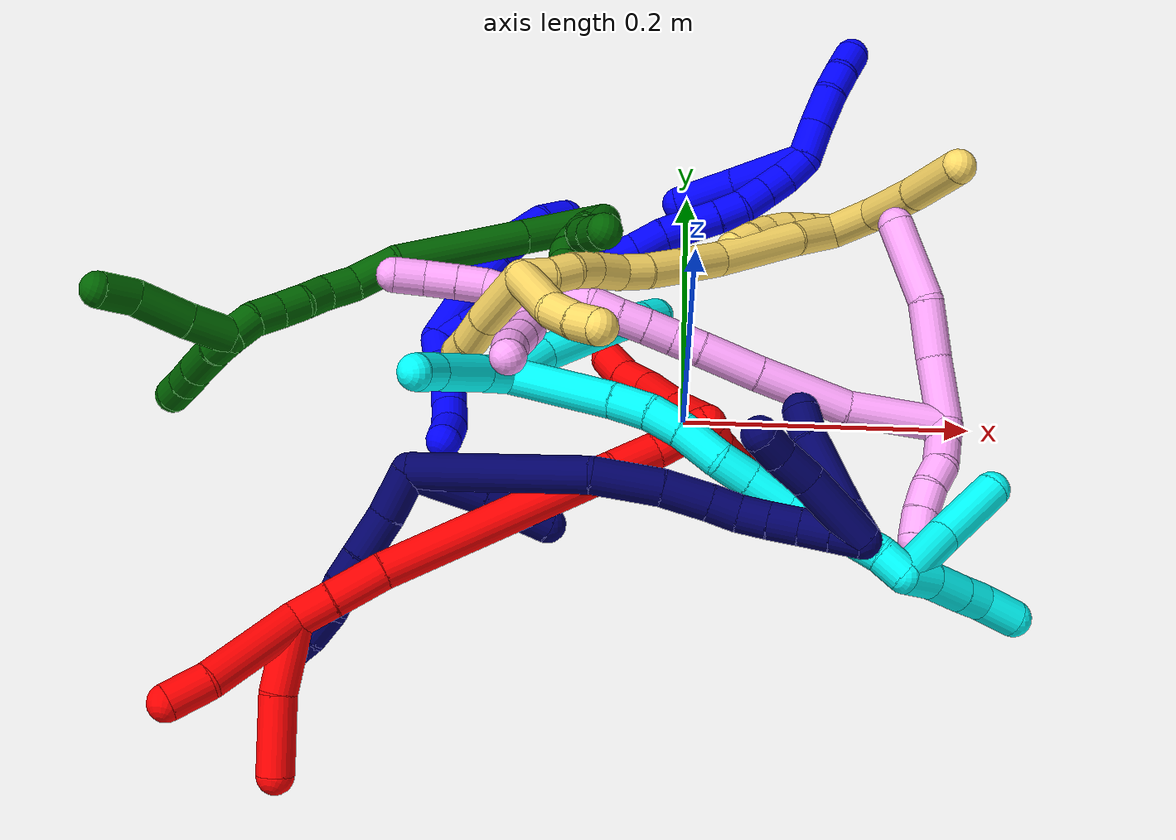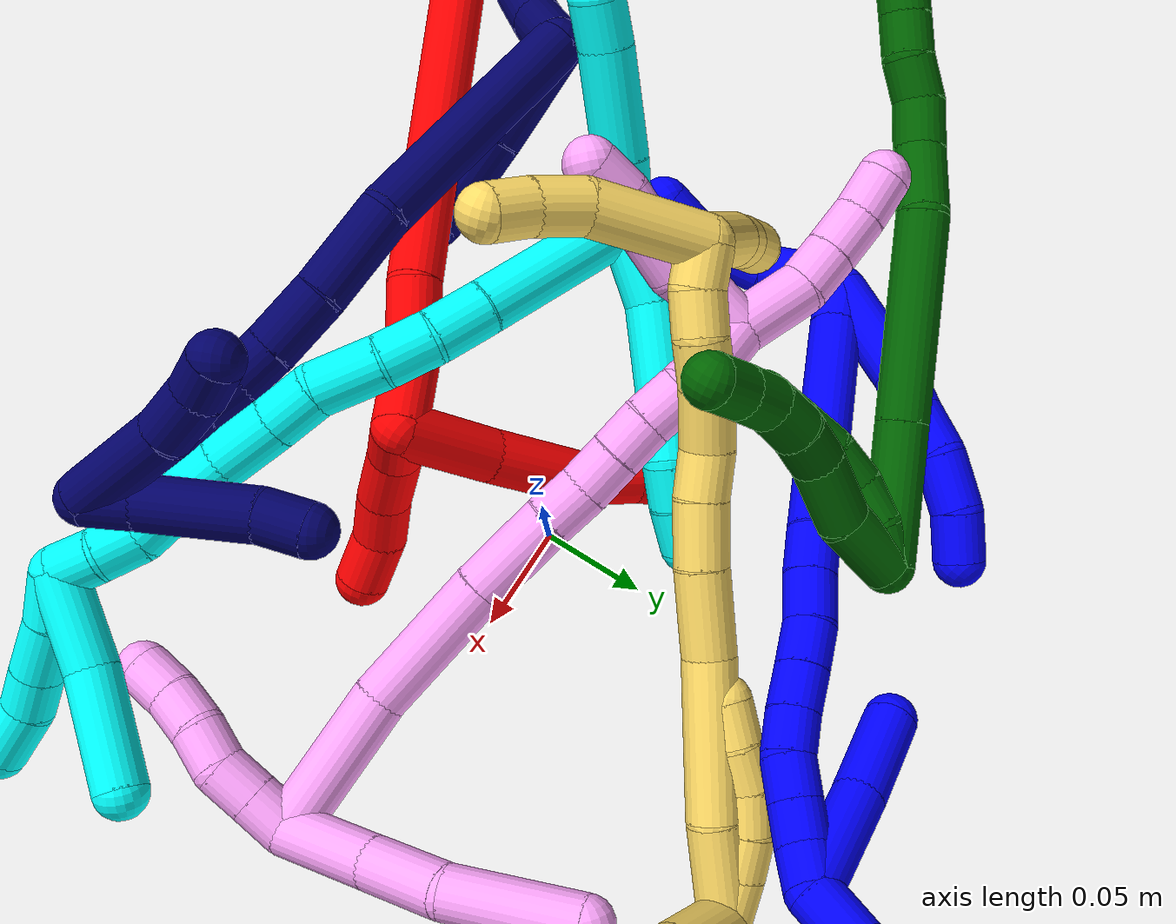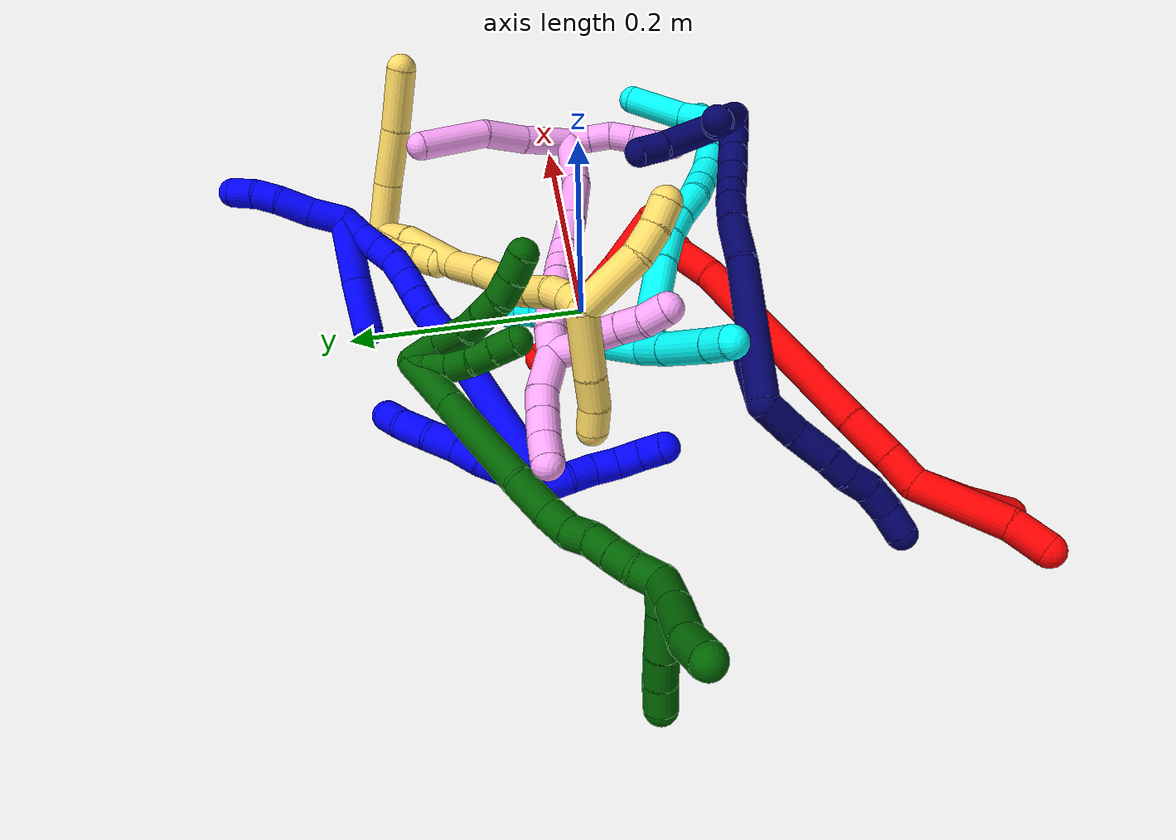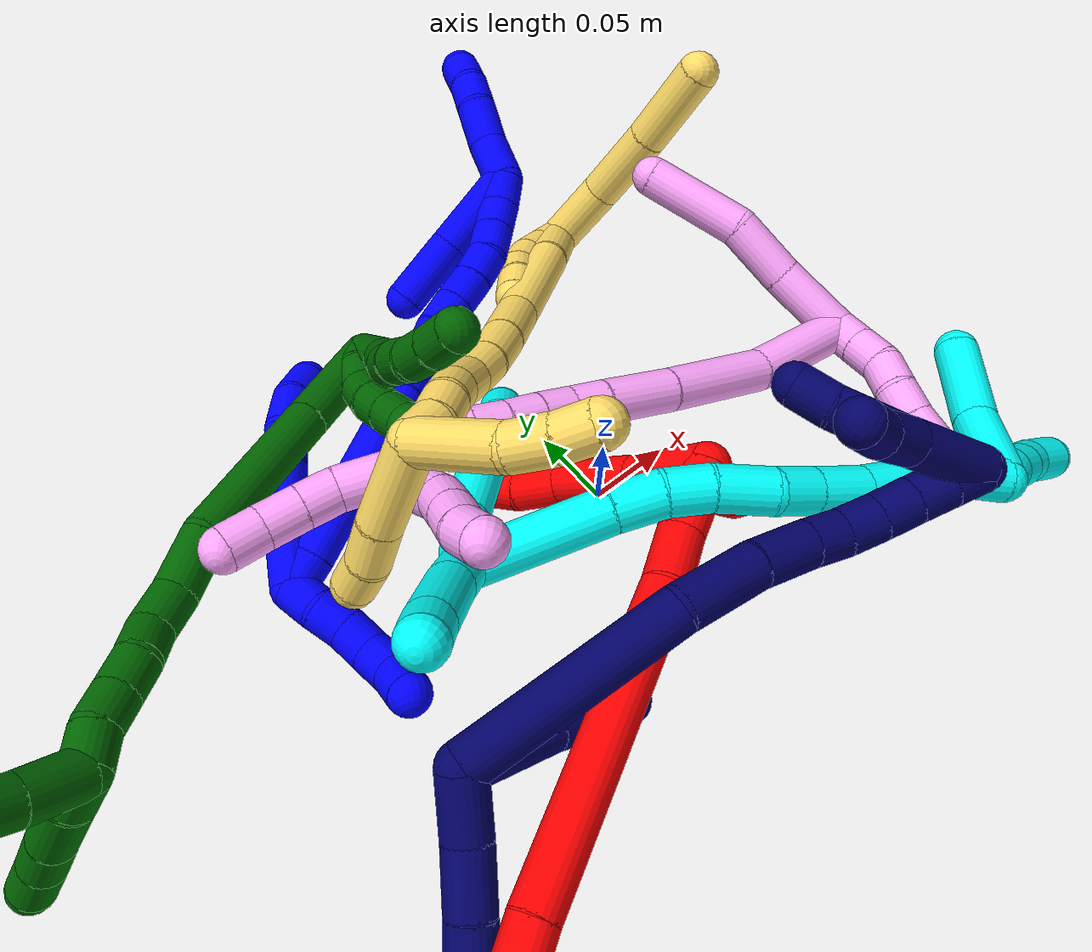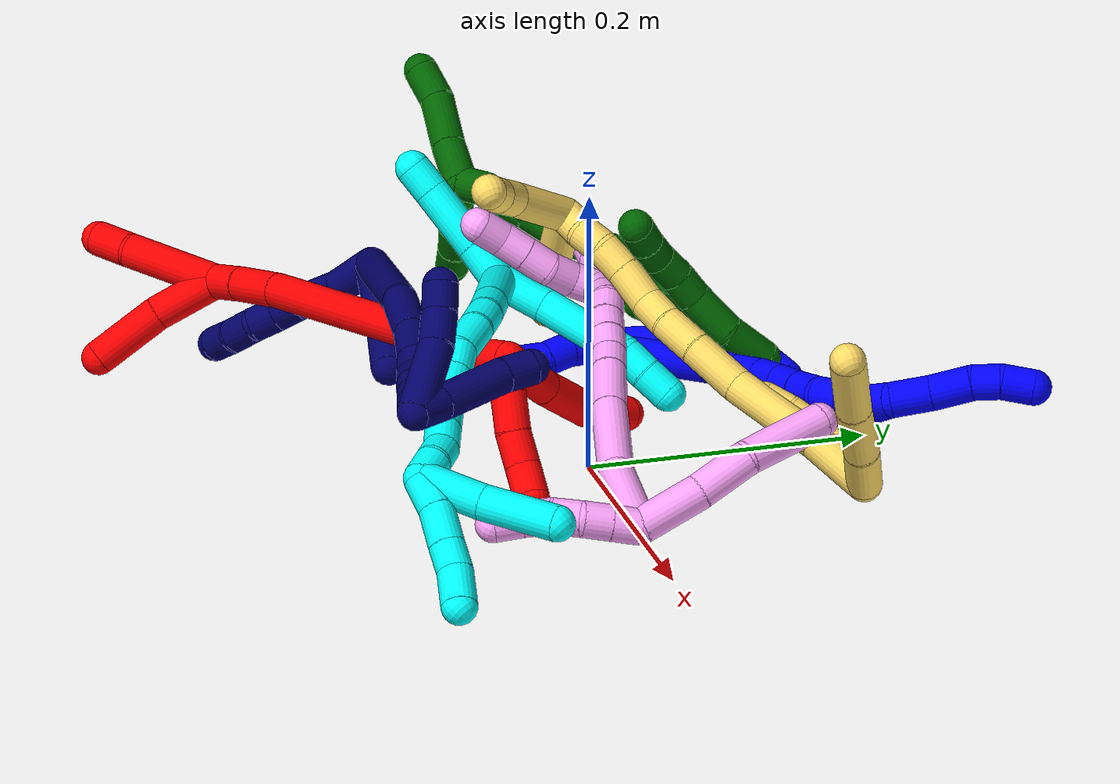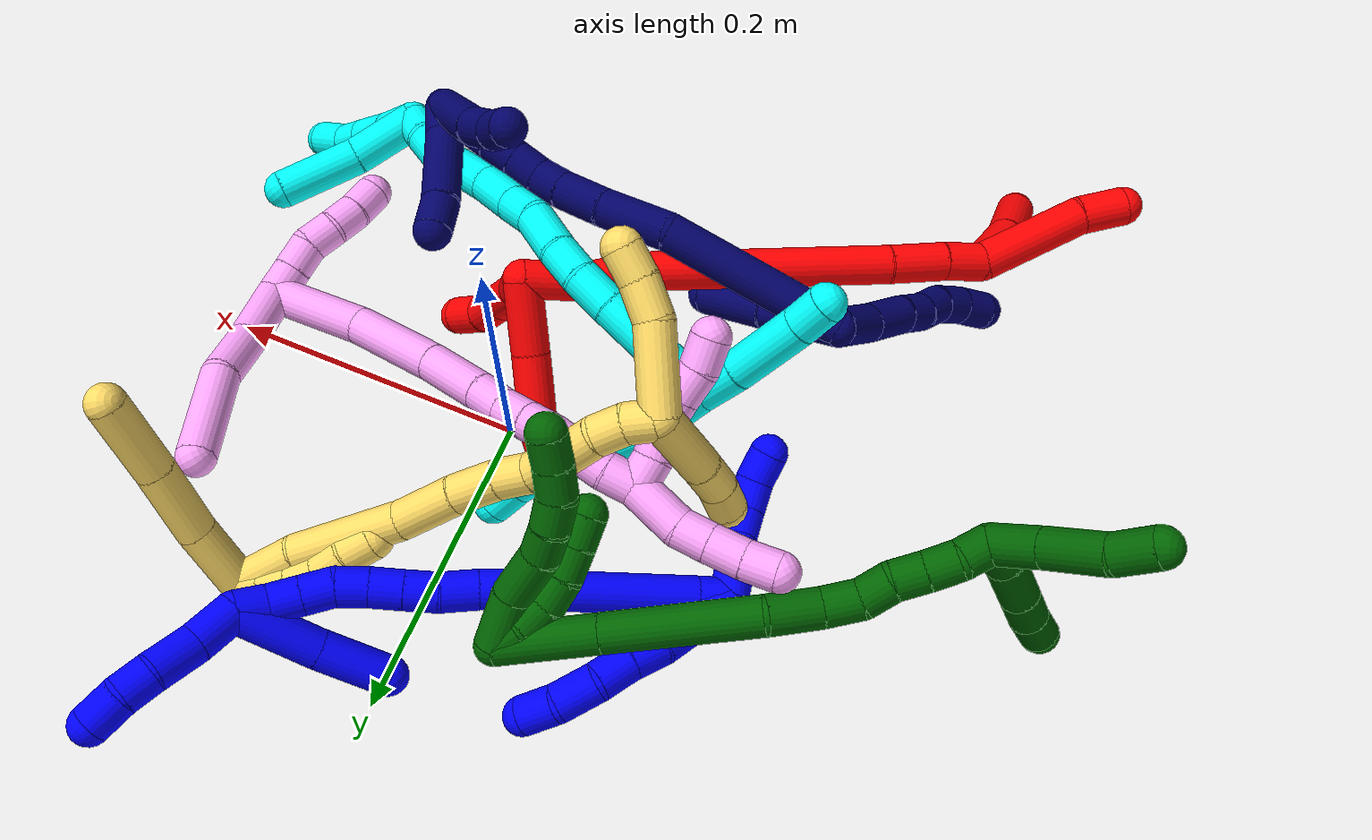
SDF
<sdf version="1.7">
 <world name="default">
  <plugin name="TubeGeneratorPlugin" filename="libtube_generator_plugin.so"/>
  <model name="photoneo_s_sensor">
   <static>1</static>
   <pose>0 0 2 1.57079 1.57079 3.14159</pose>
   <link name="link">
    <inertial><mass>0.1</mass></inertial>
    <sensor name="sensor" type="depth">
     <update_rate>30</update_rate>
     <camera>
      <horizontal_fov>1.22</horizontal_fov>
      <image><width>1920</width><height>1200</height><format>B8G8R8</format></image>
      <clip><near>0.1</near><far>4</far></clip>
      <depth_camera><output>points</output></depth_camera>
     </camera>
     <plugin name="camera_plugin" filename="libgazebo_ros_depth_camera.so">
      <baseline>0.2</baseline>
      <alwaysOn>1</alwaysOn>
      <updateRate>0.0</updateRate>
      <cameraName>camera_ir</cameraName>
      <imageTopicName>/camera/color/image_raw</imageTopicName>
      <cameraInfoTopicName>/camera/color/camera_info</cameraInfoTopicName>
      <depthImageTopicName>/camera/depth/image_raw</depthImageTopicName>
      <depthImageCameraInfoTopicName>/camera/depth/camera_info</depthImageCameraInfoTopicName>
      <pointCloudTopicName>/camera/depth/points</pointCloudTopicName>
      <frameName>fr_optical</frameName>
      <pointCloudCutoff>0.1</pointCloudCutoff>
      <pointCloudCutoffMax>2.0</pointCloudCutoffMax>
      <distortionK1>0</distortionK1>
      <distortionK2>0</distortionK2>
      <distortionK3>0</distortionK3>
      <distortionT1>0</distortionT1>
      <distortionT2>0</distortionT2>
      <CxPrime>0</CxPrime>
      <Cx>0</Cx>
      <Cy>0</Cy>
      <focalLength>0</focalLength>
      <hackBaseline>0</hackBaseline>
     </plugin>
    </sensor>
   </link>
  </model>
  <gravity>0 0 -9.8</gravity>
  <magnetic_field>6e-06 2.3e-05 -4.2e-05</magnetic_field>
  <atmosphere type="adiabatic"/>
  <physics name="default_physics" default="0" type="ode">
   <max_step_size>0.003</max_step_size>
   <real_time_factor>1</real_time_factor>
   <real_time_update_rate>1000</real_time_update_rate>
   <max_contacts>10000</max_contacts>
   <ode>
    <solver>
     <type>quick</type>
     <iters>100</iters>
     <sor>1.3</sor>
     <use_dynamic_moi_rescaling>0</use_dynamic_moi_rescaling>
    </solver>
    <constraints>
     <contact_max_correcting_vel>0</contact_max_correcting_vel>
     <contact_surface_layer>0.001</contact_surface_layer>
     <cfm>0</cfm>
     <erp>0.2</erp>
    </constraints>
   </ode>
  </physics>
  <scene><ambient>0.4 0.4 0.4 1</ambient><background>0.7 0.7 0.7 1</background><shadows>0</shadows></scene>
  <audio><device>default</device></audio>
  <spherical_coordinates>
   <surface_model>EARTH_WGS84</surface_model>
   <latitude_deg>0</latitude_deg>
   <longitude_deg>0</longitude_deg>
   <elevation>0</elevation>
   <heading_deg>0</heading_deg>
  </spherical_coordinates>
  <model name="bin">
   <static>1</static>
   <link name="bottom">
    <collision name="collision-bottom">
     <pose>0 0 -0.01 0 -0 0</pose>
     <geometry><box><size>0.8 0.6 0.02</size></box></geometry>
     <surface>
      <friction><ode><mu>100</mu><mu2>100</mu2></ode></friction>
      <contact><collide_bitmask>65535</collide_bitmask></contact>
     </surface>
    </collision>
   </link>
   <link name="west_wall">
    <collision name="collision-west_wall">
     <pose>-0.41 0 0.1 0 -0 0</pose>
     <geometry><box><size>0.02 0.6 0.2</size></box></geometry>
     <surface>
      <friction><ode><mu>100</mu><mu2>100</mu2></ode></friction>
      <contact><collide_bitmask>65535</collide_bitmask></contact>
     </surface>
    </collision>
   </link>
   <link name="east_wall">
    <collision name="collision-east_wall">
     <pose>0.41 0 0.1 0 -0 0</pose>
     <geometry><box><size>0.02 0.6 0.2</size></box></geometry>
     <surface>
      <friction><ode><mu>100</mu><mu2>100</mu2></ode></friction>
      <contact><collide_bitmask>65535</collide_bitmask></contact>
     </surface>
    </collision>
   </link>
   <link name="south_wall">
    <collision name="collision-south_wall">
     <pose>0 -0.31 0.1 0 -0 0</pose>
     <geometry><box><size>0.8 0.02 0.2</size></box></geometry>
     <surface>
      <friction><ode><mu>100</mu><mu2>100</mu2></ode></friction>
      <contact><collide_bitmask>65535</collide_bitmask></contact>
     </surface>
    </collision>
   </link>
   <link name="north_wall">
    <collision name="collision-north_wall">
     <pose>0 0.31 0.1 0 -0 0</pose>
     <geometry><box><size>0.8 0.02 0.2</size></box></geometry>
     <surface>
      <friction><ode><mu>100</mu><mu2>100</mu2></ode></friction>
      <contact><collide_bitmask>65535</collide_bitmask></contact>
     </surface>
    </collision>
   </link>
  </model>
  <model name="1">
   <static>0</static>
   <link name="1">
    <collision name="collision-cylinder-e_1_2_8">
     <pose>0.003148 0.001425 0.02672 -0.053294 0.117125 -0.003125</pose>
     <geometry><cylinder><radius>0.0125</radius><length>0.053885</length></cylinder></geometry>
     <surface>
      <friction><ode><mu>1.16</mu><mu2>1.16</mu2><slip1>0</slip1><slip2>0</slip2></ode></friction>
      <contact><ode><kp>1e+06</kp><kd>1</kd><max_vel>0</max_vel><min_depth>0.001</min_depth></ode></contact>
     </surface>
    </collision>
    <visual name="visual-cylinder-e_1_2_8">
     <pose>0.003148 0.001425 0.02672 -0.053294 0.117125 -0.003125</pose>
     <geometry><cylinder><radius>0.0125</radius><length>0.053885</length></cylinder></geometry>
     <material><ambient>0 0 1 1</ambient></material>
    </visual>
    <collision name="collision-cylinder-e_2_8_9">
     <pose>0.008727 0.004811 0.063961 -0.184227 0.223293 -0.020712</pose>
     <geometry><cylinder><radius>0.0125</radius><length>0.02195</length></cylinder></geometry>
     <surface>
      <friction><ode><mu>1.16</mu><mu2>1.16</mu2><slip1>0</slip1><slip2>0</slip2></ode></friction>
      <contact><ode><kp>1e+06</kp><kd>1</kd><max_vel>0</max_vel><min_depth>0.001</min_depth></ode></contact>
     </surface>
    </collision>
    <visual name="visual-cylinder-e_2_8_9">
     <pose>0.008727 0.004811 0.063961 -0.184227 0.223293 -0.020712</pose>
     <geometry><cylinder><radius>0.0125</radius><length>0.02195</length></cylinder></geometry>
     <material><ambient>0 0 1 1</ambient></material>
    </visual>
    <collision name="collision-cylinder-e_3_9_10">
     <pose>0.012284 0.00864 0.086108 -0.159356 0.095377 -0.007621</pose>
     <geometry><cylinder><radius>0.0125</radius><length>0.023657</length></cylinder></geometry>
     <surface>
      <friction><ode><mu>1.16</mu><mu2>1.16</mu2><slip1>0</slip1><slip2>0</slip2></ode></friction>
      <contact><ode><kp>1e+06</kp><kd>1</kd><max_vel>0</max_vel><min_depth>0.001</min_depth></ode></contact>
     </surface>
    </collision>
    <visual name="visual-cylinder-e_3_9_10">
     <pose>0.012284 0.00864 0.086108 -0.159356 0.095377 -0.007621</pose>
     <geometry><cylinder><radius>0.0125</radius><length>0.023657</length></cylinder></geometry>
     <material><ambient>0 0 1 1</ambient></material>
    </visual>
    <collision name="collision-cylinder-e_4_10_11">
     <pose>0.013537 0.016376 0.109936 -0.448162 0.009321 -0.002124</pose>
     <geometry><cylinder><radius>0.0125</radius><length>0.027081</length></cylinder></geometry>
     <surface>
      <friction><ode><mu>1.16</mu><mu2>1.16</mu2><slip1>0</slip1><slip2>0</slip2></ode></friction>
      <contact><ode><kp>1e+06</kp><kd>1</kd><max_vel>0</max_vel><min_depth>0.001</min_depth></ode></contact>
     </surface>
    </collision>
    <visual name="visual-cylinder-e_4_10_11">
     <pose>0.013537 0.016376 0.109936 -0.448162 0.009321 -0.002124</pose>
     <geometry><cylinder><radius>0.0125</radius><length>0.027081</length></cylinder></geometry>
     <material><ambient>0 0 1 1</ambient></material>
    </visual>
    <collision name="collision-cylinder-e_5_11_6">
     <pose>0.013499 0.030208 0.130725 -0.747908 -0.01397 0.005482</pose>
     <geometry><cylinder><radius>0.0125</radius><length>0.023428</length></cylinder></geometry>
     <surface>
      <friction><ode><mu>1.16</mu><mu2>1.16</mu2><slip1>0</slip1><slip2>0</slip2></ode></friction>
      <contact><ode><kp>1e+06</kp><kd>1</kd><max_vel>0</max_vel><min_depth>0.001</min_depth></ode></contact>
     </surface>
    </collision>
    <visual name="visual-cylinder-e_5_11_6">
     <pose>0.013499 0.030208 0.130725 -0.747908 -0.01397 0.005482</pose>
     <geometry><cylinder><radius>0.0125</radius><length>0.023428</length></cylinder></geometry>
     <material><ambient>0 0 1 1</ambient></material>
    </visual>
    <collision name="collision-cylinder-e_1_2_12">
     <pose>0.004757 0.002986 -0.008274 -2.79527 0.495711 -1.93201</pose>
     <geometry><cylinder><radius>0.0125</radius><length>0.02</length></cylinder></geometry>
     <surface>
      <friction><ode><mu>1.16</mu><mu2>1.16</mu2><slip1>0</slip1><slip2>0</slip2></ode></friction>
      <contact><ode><kp>1e+06</kp><kd>1</kd><max_vel>0</max_vel><min_depth>0.001</min_depth></ode></contact>
     </surface>
    </collision>
    <visual name="visual-cylinder-e_1_2_12">
     <pose>0.004757 0.002986 -0.008274 -2.79527 0.495711 -1.93201</pose>
     <geometry><cylinder><radius>0.0125</radius><length>0.02</length></cylinder></geometry>
     <material><ambient>0 0 1 1</ambient></material>
    </visual>
    <collision name="collision-cylinder-e_2_12_13">
     <pose>0.013411 0.010978 -0.024278 -2.56686 0.400429 -1.2034</pose>
     <geometry><cylinder><radius>0.0125</radius><length>0.02</length></cylinder></geometry>
     <surface>
      <friction><ode><mu>1.16</mu><mu2>1.16</mu2><slip1>0</slip1><slip2>0</slip2></ode></friction>
      <contact><ode><kp>1e+06</kp><kd>1</kd><max_vel>0</max_vel><min_depth>0.001</min_depth></ode></contact>
     </surface>
    </collision>
    <visual name="visual-cylinder-e_2_12_13">
     <pose>0.013411 0.010978 -0.024278 -2.56686 0.400429 -1.2034</pose>
     <geometry><cylinder><radius>0.0125</radius><length>0.02</length></cylinder></geometry>
     <material><ambient>0 0 1 1</ambient></material>
    </visual>
    <collision name="collision-cylinder-e_3_13_14">
     <pose>0.021385 0.018648 -0.040742 -2.84553 0.419729 -1.92</pose>
     <geometry><cylinder><radius>0.0125</radius><length>0.02</length></cylinder></geometry>
     <surface>
      <friction><ode><mu>1.16</mu><mu2>1.16</mu2><slip1>0</slip1><slip2>0</slip2></ode></friction>
      <contact><ode><kp>1e+06</kp><kd>1</kd><max_vel>0</max_vel><min_depth>0.001</min_depth></ode></contact>
     </surface>
    </collision>
    <visual name="visual-cylinder-e_3_13_14">
     <pose>0.021385 0.018648 -0.040742 -2.84553 0.419729 -1.92</pose>
     <geometry><cylinder><radius>0.0125</radius><length>0.02</length></cylinder></geometry>
     <material><ambient>0 0 1 1</ambient></material>
    </visual>
    <collision name="collision-cylinder-e_4_14_15">
     <pose>0.030934 0.022051 -0.057812 -3.05321 0.579337 -2.84702</pose>
     <geometry><cylinder><radius>0.0125</radius><length>0.02</length></cylinder></geometry>
     <surface>
      <friction><ode><mu>1.16</mu><mu2>1.16</mu2><slip1>0</slip1><slip2>0</slip2></ode></friction>
      <contact><ode><kp>1e+06</kp><kd>1</kd><max_vel>0</max_vel><min_depth>0.001</min_depth></ode></contact>
     </surface>
    </collision>
    <visual name="visual-cylinder-e_4_14_15">
     <pose>0.030934 0.022051 -0.057812 -3.05321 0.579337 -2.84702</pose>
     <geometry><cylinder><radius>0.0125</radius><length>0.02</length></cylinder></geometry>
     <material><ambient>0 0 1 1</ambient></material>
    </visual>
    <collision name="collision-cylinder-e_5_15_5">
     <pose>0.041958 0.020414 -0.07412 2.85195 0.588202 2.24408</pose>
     <geometry><cylinder><radius>0.0125</radius><length>0.02</length></cylinder></geometry>
     <surface>
      <friction><ode><mu>1.16</mu><mu2>1.16</mu2><slip1>0</slip1><slip2>0</slip2></ode></friction>
      <contact><ode><kp>1e+06</kp><kd>1</kd><max_vel>0</max_vel><min_depth>0.001</min_depth></ode></contact>
     </surface>
    </collision>
    <visual name="visual-cylinder-e_5_15_5">
     <pose>0.041958 0.020414 -0.07412 2.85195 0.588202 2.24408</pose>
     <geometry><cylinder><radius>0.0125</radius><length>0.02</length></cylinder></geometry>
     <material><ambient>0 0 1 1</ambient></material>
    </visual>
    <collision name="collision-cylinder-e_1_2_16">
     <pose>0.005508 0.004657 0.007107 -0.580066 0.575171 -0.176097</pose>
     <geometry><cylinder><radius>0.0125</radius><length>0.020252</length></cylinder></geometry>
     <surface>
      <friction><ode><mu>1.16</mu><mu2>1.16</mu2><slip1>0</slip1><slip2>0</slip2></ode></friction>
      <contact><ode><kp>1e+06</kp><kd>1</kd><max_vel>0</max_vel><min_depth>0.001</min_depth></ode></contact>
     </surface>
    </collision>
    <visual name="visual-cylinder-e_1_2_16">
     <pose>0.005508 0.004657 0.007107 -0.580066 0.575171 -0.176097</pose>
     <geometry><cylinder><radius>0.0125</radius><length>0.020252</length></cylinder></geometry>
     <material><ambient>0 0 1 1</ambient></material>
    </visual>
    <collision name="collision-cylinder-e_2_16_17">
     <pose>0.042328 0.031415 0.055324 -0.493284 0.590882 -0.152951</pose>
     <geometry><cylinder><radius>0.0125</radius><length>0.112407</length></cylinder></geometry>
     <surface>
      <friction><ode><mu>1.16</mu><mu2>1.16</mu2><slip1>0</slip1><slip2>0</slip2></ode></friction>
      <contact><ode><kp>1e+06</kp><kd>1</kd><max_vel>0</max_vel><min_depth>0.001</min_depth></ode></contact>
     </surface>
    </collision>
    <visual name="visual-cylinder-e_2_16_17">
     <pose>0.042328 0.031415 0.055324 -0.493284 0.590882 -0.152951</pose>
     <geometry><cylinder><radius>0.0125</radius><length>0.112407</length></cylinder></geometry>
     <material><ambient>0 0 1 1</ambient></material>
    </visual>
    <collision name="collision-cylinder-e_3_17_18">
     <pose>0.079104 0.058514 0.104692 -0.544284 0.515265 -0.146797</pose>
     <geometry><cylinder><radius>0.0125</radius><length>0.022185</length></cylinder></geometry>
     <surface>
      <friction><ode><mu>1.16</mu><mu2>1.16</mu2><slip1>0</slip1><slip2>0</slip2></ode></friction>
      <contact><ode><kp>1e+06</kp><kd>1</kd><max_vel>0</max_vel><min_depth>0.001</min_depth></ode></contact>
     </surface>
    </collision>
    <visual name="visual-cylinder-e_3_17_18">
     <pose>0.079104 0.058514 0.104692 -0.544284 0.515265 -0.146797</pose>
     <geometry><cylinder><radius>0.0125</radius><length>0.022185</length></cylinder></geometry>
     <material><ambient>0 0 1 1</ambient></material>
    </visual>
    <collision name="collision-cylinder-e_4_18_19">
     <pose>0.090094 0.06796 0.122376 -0.440804 0.487283 -0.11127</pose>
     <geometry><cylinder><radius>0.0125</radius><length>0.023593</length></cylinder></geometry>
     <surface>
      <friction><ode><mu>1.16</mu><mu2>1.16</mu2><slip1>0</slip1><slip2>0</slip2></ode></friction>
      <contact><ode><kp>1e+06</kp><kd>1</kd><max_vel>0</max_vel><min_depth>0.001</min_depth></ode></contact>
     </surface>
    </collision>
    <visual name="visual-cylinder-e_4_18_19">
     <pose>0.090094 0.06796 0.122376 -0.440804 0.487283 -0.11127</pose>
     <geometry><cylinder><radius>0.0125</radius><length>0.023593</length></cylinder></geometry>
     <material><ambient>0 0 1 1</ambient></material>
    </visual>
    <collision name="collision-cylinder-e_5_19_20">
     <pose>0.101216 0.077549 0.138971 -0.622301 0.565561 -0.18635</pose>
     <geometry><cylinder><radius>0.0125</radius><length>0.020896</length></cylinder></geometry>
     <surface>
      <friction><ode><mu>1.16</mu><mu2>1.16</mu2><slip1>0</slip1><slip2>0</slip2></ode></friction>
      <contact><ode><kp>1e+06</kp><kd>1</kd><max_vel>0</max_vel><min_depth>0.001</min_depth></ode></contact>
     </surface>
    </collision>
    <visual name="visual-cylinder-e_5_19_20">
     <pose>0.101216 0.077549 0.138971 -0.622301 0.565561 -0.18635</pose>
     <geometry><cylinder><radius>0.0125</radius><length>0.020896</length></cylinder></geometry>
     <material><ambient>0 0 1 1</ambient></material>
    </visual>
    <collision name="collision-cylinder-e_6_20_21">
     <pose>0.112361 0.087942 0.15306 -0.648966 0.568154 -0.195796</pose>
     <geometry><cylinder><radius>0.0125</radius><length>0.020615</length></cylinder></geometry>
     <surface>
      <friction><ode><mu>1.16</mu><mu2>1.16</mu2><slip1>0</slip1><slip2>0</slip2></ode></friction>
      <contact><ode><kp>1e+06</kp><kd>1</kd><max_vel>0</max_vel><min_depth>0.001</min_depth></ode></contact>
     </surface>
    </collision>
    <visual name="visual-cylinder-e_6_20_21">
     <pose>0.112361 0.087942 0.15306 -0.648966 0.568154 -0.195796</pose>
     <geometry><cylinder><radius>0.0125</radius><length>0.020615</length></cylinder></geometry>
     <material><ambient>0 0 1 1</ambient></material>
    </visual>
    <collision name="collision-cylinder-e_7_21_22">
     <pose>0.122988 0.097805 0.167261 -0.564866 0.53268 -0.158011</pose>
     <geometry><cylinder><radius>0.0125</radius><length>0.020006</length></cylinder></geometry>
     <surface>
      <friction><ode><mu>1.16</mu><mu2>1.16</mu2><slip1>0</slip1><slip2>0</slip2></ode></friction>
      <contact><ode><kp>1e+06</kp><kd>1</kd><max_vel>0</max_vel><min_depth>0.001</min_depth></ode></contact>
     </surface>
    </collision>
    <visual name="visual-cylinder-e_7_21_22">
     <pose>0.122988 0.097805 0.167261 -0.564866 0.53268 -0.158011</pose>
     <geometry><cylinder><radius>0.0125</radius><length>0.020006</length></cylinder></geometry>
     <material><ambient>0 0 1 1</ambient></material>
    </visual>
    <collision name="collision-cylinder-e_8_22_23">
     <pose>0.131054 0.106016 0.183383 -0.386374 0.303125 -0.05974</pose>
     <geometry><cylinder><radius>0.0125</radius><length>0.020006</length></cylinder></geometry>
     <surface>
      <friction><ode><mu>1.16</mu><mu2>1.16</mu2><slip1>0</slip1><slip2>0</slip2></ode></friction>
      <contact><ode><kp>1e+06</kp><kd>1</kd><max_vel>0</max_vel><min_depth>0.001</min_depth></ode></contact>
     </surface>
    </collision>
    <visual name="visual-cylinder-e_8_22_23">
     <pose>0.131054 0.106016 0.183383 -0.386374 0.303125 -0.05974</pose>
     <geometry><cylinder><radius>0.0125</radius><length>0.020006</length></cylinder></geometry>
     <material><ambient>0 0 1 1</ambient></material>
    </visual>
    <collision name="collision-cylinder-e_9_23_24">
     <pose>0.137072 0.113048 0.20112 -0.368548 0.307921 -0.057835</pose>
     <geometry><cylinder><radius>0.0125</radius><length>0.020009</length></cylinder></geometry>
     <surface>
      <friction><ode><mu>1.16</mu><mu2>1.16</mu2><slip1>0</slip1><slip2>0</slip2></ode></friction>
      <contact><ode><kp>1e+06</kp><kd>1</kd><max_vel>0</max_vel><min_depth>0.001</min_depth></ode></contact>
     </surface>
    </collision>
    <visual name="visual-cylinder-e_9_23_24">
     <pose>0.137072 0.113048 0.20112 -0.368548 0.307921 -0.057835</pose>
     <geometry><cylinder><radius>0.0125</radius><length>0.020009</length></cylinder></geometry>
     <material><ambient>0 0 1 1</ambient></material>
    </visual>
    <collision name="collision-cylinder-e_10_24_1">
     <pose>0.14466 0.117897 0.218819 -0.159234 0.47225 -0.03839</pose>
     <geometry><cylinder><radius>0.0125</radius><length>0.020029</length></cylinder></geometry>
     <surface>
      <friction><ode><mu>1.16</mu><mu2>1.16</mu2><slip1>0</slip1><slip2>0</slip2></ode></friction>
      <contact><ode><kp>1e+06</kp><kd>1</kd><max_vel>0</max_vel><min_depth>0.001</min_depth></ode></contact>
     </surface>
    </collision>
    <visual name="visual-cylinder-e_10_24_1">
     <pose>0.14466 0.117897 0.218819 -0.159234 0.47225 -0.03839</pose>
     <geometry><cylinder><radius>0.0125</radius><length>0.020029</length></cylinder></geometry>
     <material><ambient>0 0 1 1</ambient></material>
    </visual>
    <collision name="collision-cylinder-e_1_1_25">
     <pose>0.125849 0.111799 0.215485 2.58748 -1.02235 -2.20316</pose>
     <geometry><cylinder><radius>0.0125</radius><length>0.054765</length></cylinder></geometry>
     <surface>
      <friction><ode><mu>1.16</mu><mu2>1.16</mu2><slip1>0</slip1><slip2>0</slip2></ode></friction>
      <contact><ode><kp>1e+06</kp><kd>1</kd><max_vel>0</max_vel><min_depth>0.001</min_depth></ode></contact>
     </surface>
    </collision>
    <visual name="visual-cylinder-e_1_1_25">
     <pose>0.125849 0.111799 0.215485 2.58748 -1.02235 -2.20316</pose>
     <geometry><cylinder><radius>0.0125</radius><length>0.054765</length></cylinder></geometry>
     <material><ambient>0 0 1 1</ambient></material>
    </visual>
    <collision name="collision-cylinder-e_2_25_4">
     <pose>0.084132 0.09704 0.192286 2.56149 -0.94643 -2.08606</pose>
     <geometry><cylinder><radius>0.0125</radius><length>0.045235</length></cylinder></geometry>
     <surface>
      <friction><ode><mu>1.16</mu><mu2>1.16</mu2><slip1>0</slip1><slip2>0</slip2></ode></friction>
      <contact><ode><kp>1e+06</kp><kd>1</kd><max_vel>0</max_vel><min_depth>0.001</min_depth></ode></contact>
     </surface>
    </collision>
    <visual name="visual-cylinder-e_2_25_4">
     <pose>0.084132 0.09704 0.192286 2.56149 -0.94643 -2.08606</pose>
     <geometry><cylinder><radius>0.0125</radius><length>0.045235</length></cylinder></geometry>
     <material><ambient>0 0 1 1</ambient></material>
    </visual>
    <collision name="collision-cylinder-e_1_1_26">
     <pose>0.149543 0.117586 0.241758 0.121471 0.023037 0.001401</pose>
     <geometry><cylinder><radius>0.0125</radius><length>0.028484</length></cylinder></geometry>
     <surface>
      <friction><ode><mu>1.16</mu><mu2>1.16</mu2><slip1>0</slip1><slip2>0</slip2></ode></friction>
      <contact><ode><kp>1e+06</kp><kd>1</kd><max_vel>0</max_vel><min_depth>0.001</min_depth></ode></contact>
     </surface>
    </collision>
    <visual name="visual-cylinder-e_1_1_26">
     <pose>0.149543 0.117586 0.241758 0.121471 0.023037 0.001401</pose>
     <geometry><cylinder><radius>0.0125</radius><length>0.028484</length></cylinder></geometry>
     <material><ambient>0 0 1 1</ambient></material>
    </visual>
    <collision name="collision-cylinder-e_2_26_27">
     <pose>0.151985 0.113769 0.270142 0.145736 0.14571 0.010655</pose>
     <geometry><cylinder><radius>0.0125</radius><length>0.029116</length></cylinder></geometry>
     <surface>
      <friction><ode><mu>1.16</mu><mu2>1.16</mu2><slip1>0</slip1><slip2>0</slip2></ode></friction>
      <contact><ode><kp>1e+06</kp><kd>1</kd><max_vel>0</max_vel><min_depth>0.001</min_depth></ode></contact>
     </surface>
    </collision>
    <visual name="visual-cylinder-e_2_26_27">
     <pose>0.151985 0.113769 0.270142 0.145736 0.14571 0.010655</pose>
     <geometry><cylinder><radius>0.0125</radius><length>0.029116</length></cylinder></geometry>
     <material><ambient>0 0 1 1</ambient></material>
    </visual>
    <collision name="collision-cylinder-e_3_27_28">
     <pose>0.154355 0.111989 0.294437 -0.031012 0.025522 -0.000396</pose>
     <geometry><cylinder><radius>0.0125</radius><length>0.020105</length></cylinder></geometry>
     <surface>
      <friction><ode><mu>1.16</mu><mu2>1.16</mu2><slip1>0</slip1><slip2>0</slip2></ode></friction>
      <contact><ode><kp>1e+06</kp><kd>1</kd><max_vel>0</max_vel><min_depth>0.001</min_depth></ode></contact>
     </surface>
    </collision>
    <visual name="visual-cylinder-e_3_27_28">
     <pose>0.154355 0.111989 0.294437 -0.031012 0.025522 -0.000396</pose>
     <geometry><cylinder><radius>0.0125</radius><length>0.020105</length></cylinder></geometry>
     <material><ambient>0 0 1 1</ambient></material>
    </visual>
    <collision name="collision-cylinder-e_4_28_3">
     <pose>0.152674 0.114268 0.315282 -0.180234 -0.174676 0.015824</pose>
     <geometry><cylinder><radius>0.0125</radius><length>0.022295</length></cylinder></geometry>
     <surface>
      <friction><ode><mu>1.16</mu><mu2>1.16</mu2><slip1>0</slip1><slip2>0</slip2></ode></friction>
      <contact><ode><kp>1e+06</kp><kd>1</kd><max_vel>0</max_vel><min_depth>0.001</min_depth></ode></contact>
     </surface>
    </collision>
    <visual name="visual-cylinder-e_4_28_3">
     <pose>0.152674 0.114268 0.315282 -0.180234 -0.174676 0.015824</pose>
     <geometry><cylinder><radius>0.0125</radius><length>0.022295</length></cylinder></geometry>
     <material><ambient>0 0 1 1</ambient></material>
    </visual>
    <collision name="collision-sphere-3">
     <pose>0.150737 0.116236 0.326083 0 -0 0</pose>
     <geometry><sphere><radius>0.0125</radius></sphere></geometry>
     <surface>
      <friction><ode><mu>1.16</mu><mu2>1.16</mu2><slip1>0</slip1><slip2>0</slip2></ode></friction>
      <contact><ode><kp>1e+06</kp><kd>1</kd><max_vel>0</max_vel><min_depth>0.001</min_depth></ode></contact>
     </surface>
    </collision>
    <visual name="visual-sphere-3">
     <pose>0.150737 0.116236 0.326083 0 -0 0</pose>
     <geometry><sphere><radius>0.0125</radius></sphere></geometry>
     <material><ambient>0 0 1 1</ambient></material>
    </visual>
    <collision name="collision-sphere-28">
     <pose>0.154612 0.112301 0.304482 0 -0 0</pose>
     <geometry><sphere><radius>0.0125</radius></sphere></geometry>
     <surface>
      <friction><ode><mu>1.16</mu><mu2>1.16</mu2><slip1>0</slip1><slip2>0</slip2></ode></friction>
      <contact><ode><kp>1e+06</kp><kd>1</kd><max_vel>0</max_vel><min_depth>0.001</min_depth></ode></contact>
     </surface>
    </collision>
    <visual name="visual-sphere-28">
     <pose>0.154612 0.112301 0.304482 0 -0 0</pose>
     <geometry><sphere><radius>0.0125</radius></sphere></geometry>
     <material><ambient>0 0 1 1</ambient></material>
    </visual>
    <collision name="collision-sphere-27">
     <pose>0.154099 0.111677 0.284393 0 -0 0</pose>
     <geometry><sphere><radius>0.0125</radius></sphere></geometry>
     <surface>
      <friction><ode><mu>1.16</mu><mu2>1.16</mu2><slip1>0</slip1><slip2>0</slip2></ode></friction>
      <contact><ode><kp>1e+06</kp><kd>1</kd><max_vel>0</max_vel><min_depth>0.001</min_depth></ode></contact>
     </surface>
    </collision>
    <visual name="visual-sphere-27">
     <pose>0.154099 0.111677 0.284393 0 -0 0</pose>
     <geometry><sphere><radius>0.0125</radius></sphere></geometry>
     <material><ambient>0 0 1 1</ambient></material>
    </visual>
    <collision name="collision-sphere-26">
     <pose>0.149871 0.115861 0.255891 0 -0 0</pose>
     <geometry><sphere><radius>0.0125</radius></sphere></geometry>
     <surface>
      <friction><ode><mu>1.16</mu><mu2>1.16</mu2><slip1>0</slip1><slip2>0</slip2></ode></friction>
      <contact><ode><kp>1e+06</kp><kd>1</kd><max_vel>0</max_vel><min_depth>0.001</min_depth></ode></contact>
     </surface>
    </collision>
    <visual name="visual-sphere-26">
     <pose>0.149871 0.115861 0.255891 0 -0 0</pose>
     <geometry><sphere><radius>0.0125</radius></sphere></geometry>
     <material><ambient>0 0 1 1</ambient></material>
    </visual>
    <collision name="collision-sphere-4">
     <pose>0.065782 0.089793 0.181227 0 -0 0</pose>
     <geometry><sphere><radius>0.0125</radius></sphere></geometry>
     <surface>
      <friction><ode><mu>1.16</mu><mu2>1.16</mu2><slip1>0</slip1><slip2>0</slip2></ode></friction>
      <contact><ode><kp>1e+06</kp><kd>1</kd><max_vel>0</max_vel><min_depth>0.001</min_depth></ode></contact>
     </surface>
    </collision>
    <visual name="visual-sphere-4">
     <pose>0.065782 0.089793 0.181227 0 -0 0</pose>
     <geometry><sphere><radius>0.0125</radius></sphere></geometry>
     <material><ambient>0 0 1 1</ambient></material>
    </visual>
    <collision name="collision-sphere-25">
     <pose>0.102482 0.104287 0.203345 0 -0 0</pose>
     <geometry><sphere><radius>0.0125</radius></sphere></geometry>
     <surface>
      <friction><ode><mu>1.16</mu><mu2>1.16</mu2><slip1>0</slip1><slip2>0</slip2></ode></friction>
      <contact><ode><kp>1e+06</kp><kd>1</kd><max_vel>0</max_vel><min_depth>0.001</min_depth></ode></contact>
     </surface>
    </collision>
    <visual name="visual-sphere-25">
     <pose>0.102482 0.104287 0.203345 0 -0 0</pose>
     <geometry><sphere><radius>0.0125</radius></sphere></geometry>
     <material><ambient>0 0 1 1</ambient></material>
    </visual>
    <collision name="collision-sphere-1">
     <pose>0.149215 0.119311 0.227625 0 -0 0</pose>
     <geometry><sphere><radius>0.0125</radius></sphere></geometry>
     <surface>
      <friction><ode><mu>1.16</mu><mu2>1.16</mu2><slip1>0</slip1><slip2>0</slip2></ode></friction>
      <contact><ode><kp>1e+06</kp><kd>1</kd><max_vel>0</max_vel><min_depth>0.001</min_depth></ode></contact>
     </surface>
    </collision>
    <visual name="visual-sphere-1">
     <pose>0.149215 0.119311 0.227625 0 -0 0</pose>
     <geometry><sphere><radius>0.0125</radius></sphere></geometry>
     <material><ambient>0 0 1 1</ambient></material>
    </visual>
    <collision name="collision-sphere-24">
     <pose>0.140104 0.116483 0.210013 0 -0 0</pose>
     <geometry><sphere><radius>0.0125</radius></sphere></geometry>
     <surface>
      <friction><ode><mu>1.16</mu><mu2>1.16</mu2><slip1>0</slip1><slip2>0</slip2></ode></friction>
      <contact><ode><kp>1e+06</kp><kd>1</kd><max_vel>0</max_vel><min_depth>0.001</min_depth></ode></contact>
     </surface>
    </collision>
    <visual name="visual-sphere-24">
     <pose>0.140104 0.116483 0.210013 0 -0 0</pose>
     <geometry><sphere><radius>0.0125</radius></sphere></geometry>
     <material><ambient>0 0 1 1</ambient></material>
    </visual>
    <collision name="collision-sphere-23">
     <pose>0.13404 0.109614 0.192226 0 -0 0</pose>
     <geometry><sphere><radius>0.0125</radius></sphere></geometry>
     <surface>
      <friction><ode><mu>1.16</mu><mu2>1.16</mu2><slip1>0</slip1><slip2>0</slip2></ode></friction>
      <contact><ode><kp>1e+06</kp><kd>1</kd><max_vel>0</max_vel><min_depth>0.001</min_depth></ode></contact>
     </surface>
    </collision>
    <visual name="visual-sphere-23">
     <pose>0.13404 0.109614 0.192226 0 -0 0</pose>
     <geometry><sphere><radius>0.0125</radius></sphere></geometry>
     <material><ambient>0 0 1 1</ambient></material>
    </visual>
    <collision name="collision-sphere-22">
     <pose>0.128068 0.102418 0.174539 0 -0 0</pose>
     <geometry><sphere><radius>0.0125</radius></sphere></geometry>
     <surface>
      <friction><ode><mu>1.16</mu><mu2>1.16</mu2><slip1>0</slip1><slip2>0</slip2></ode></friction>
      <contact><ode><kp>1e+06</kp><kd>1</kd><max_vel>0</max_vel><min_depth>0.001</min_depth></ode></contact>
     </surface>
    </collision>
    <visual name="visual-sphere-22">
     <pose>0.128068 0.102418 0.174539 0 -0 0</pose>
     <geometry><sphere><radius>0.0125</radius></sphere></geometry>
     <material><ambient>0 0 1 1</ambient></material>
    </visual>
    <collision name="collision-sphere-21">
     <pose>0.117908 0.093193 0.159982 0 -0 0</pose>
     <geometry><sphere><radius>0.0125</radius></sphere></geometry>
     <surface>
      <friction><ode><mu>1.16</mu><mu2>1.16</mu2><slip1>0</slip1><slip2>0</slip2></ode></friction>
      <contact><ode><kp>1e+06</kp><kd>1</kd><max_vel>0</max_vel><min_depth>0.001</min_depth></ode></contact>
     </surface>
    </collision>
    <visual name="visual-sphere-21">
     <pose>0.117908 0.093193 0.159982 0 -0 0</pose>
     <geometry><sphere><radius>0.0125</radius></sphere></geometry>
     <material><ambient>0 0 1 1</ambient></material>
    </visual>
    <collision name="collision-sphere-6">
     <pose>0.013336 0.038174 0.139312 0 -0 0</pose>
     <geometry><sphere><radius>0.0125</radius></sphere></geometry>
     <surface>
      <friction><ode><mu>1.16</mu><mu2>1.16</mu2><slip1>0</slip1><slip2>0</slip2></ode></friction>
      <contact><ode><kp>1e+06</kp><kd>1</kd><max_vel>0</max_vel><min_depth>0.001</min_depth></ode></contact>
     </surface>
    </collision>
    <visual name="visual-sphere-6">
     <pose>0.013336 0.038174 0.139312 0 -0 0</pose>
     <geometry><sphere><radius>0.0125</radius></sphere></geometry>
     <material><ambient>0 0 1 1</ambient></material>
    </visual>
    <collision name="collision-sphere-11">
     <pose>0.013663 0.022242 0.122139 0 -0 0</pose>
     <geometry><sphere><radius>0.0125</radius></sphere></geometry>
     <surface>
      <friction><ode><mu>1.16</mu><mu2>1.16</mu2><slip1>0</slip1><slip2>0</slip2></ode></friction>
      <contact><ode><kp>1e+06</kp><kd>1</kd><max_vel>0</max_vel><min_depth>0.001</min_depth></ode></contact>
     </surface>
    </collision>
    <visual name="visual-sphere-11">
     <pose>0.013663 0.022242 0.122139 0 -0 0</pose>
     <geometry><sphere><radius>0.0125</radius></sphere></geometry>
     <material><ambient>0 0 1 1</ambient></material>
    </visual>
    <collision name="collision-sphere-10">
     <pose>0.01341 0.010509 0.097733 0 -0 0</pose>
     <geometry><sphere><radius>0.0125</radius></sphere></geometry>
     <surface>
      <friction><ode><mu>1.16</mu><mu2>1.16</mu2><slip1>0</slip1><slip2>0</slip2></ode></friction>
      <contact><ode><kp>1e+06</kp><kd>1</kd><max_vel>0</max_vel><min_depth>0.001</min_depth></ode></contact>
     </surface>
    </collision>
    <visual name="visual-sphere-10">
     <pose>0.01341 0.010509 0.097733 0 -0 0</pose>
     <geometry><sphere><radius>0.0125</radius></sphere></geometry>
     <material><ambient>0 0 1 1</ambient></material>
    </visual>
    <collision name="collision-sphere-9">
     <pose>0.011157 0.006772 0.074482 0 -0 0</pose>
     <geometry><sphere><radius>0.0125</radius></sphere></geometry>
     <surface>
      <friction><ode><mu>1.16</mu><mu2>1.16</mu2><slip1>0</slip1><slip2>0</slip2></ode></friction>
      <contact><ode><kp>1e+06</kp><kd>1</kd><max_vel>0</max_vel><min_depth>0.001</min_depth></ode></contact>
     </surface>
    </collision>
    <visual name="visual-sphere-9">
     <pose>0.011157 0.006772 0.074482 0 -0 0</pose>
     <geometry><sphere><radius>0.0125</radius></sphere></geometry>
     <material><ambient>0 0 1 1</ambient></material>
    </visual>
    <collision name="collision-sphere-2">
     <geometry><sphere><radius>0.0125</radius></sphere></geometry>
     <surface>
      <friction><ode><mu>1.16</mu><mu2>1.16</mu2><slip1>0</slip1><slip2>0</slip2></ode></friction>
      <contact><ode><kp>1e+06</kp><kd>1</kd><max_vel>0</max_vel><min_depth>0.001</min_depth></ode></contact>
     </surface>
    </collision>
    <visual name="visual-sphere-2">
     <geometry><sphere><radius>0.0125</radius></sphere></geometry>
     <material><ambient>0 0 1 1</ambient></material>
    </visual>
    <collision name="collision-sphere-19">
     <pose>0.095617 0.072407 0.131803 0 -0 0</pose>
     <geometry><sphere><radius>0.0125</radius></sphere></geometry>
     <surface>
      <friction><ode><mu>1.16</mu><mu2>1.16</mu2><slip1>0</slip1><slip2>0</slip2></ode></friction>
      <contact><ode><kp>1e+06</kp><kd>1</kd><max_vel>0</max_vel><min_depth>0.001</min_depth></ode></contact>
     </surface>
    </collision>
    <visual name="visual-sphere-19">
     <pose>0.095617 0.072407 0.131803 0 -0 0</pose>
     <geometry><sphere><radius>0.0125</radius></sphere></geometry>
     <material><ambient>0 0 1 1</ambient></material>
    </visual>
    <collision name="collision-sphere-8">
     <pose>0.006297 0.002851 0.05344 0 -0 0</pose>
     <geometry><sphere><radius>0.0125</radius></sphere></geometry>
     <surface>
      <friction><ode><mu>1.16</mu><mu2>1.16</mu2><slip1>0</slip1><slip2>0</slip2></ode></friction>
      <contact><ode><kp>1e+06</kp><kd>1</kd><max_vel>0</max_vel><min_depth>0.001</min_depth></ode></contact>
     </surface>
    </collision>
    <visual name="visual-sphere-8">
     <pose>0.006297 0.002851 0.05344 0 -0 0</pose>
     <geometry><sphere><radius>0.0125</radius></sphere></geometry>
     <material><ambient>0 0 1 1</ambient></material>
    </visual>
    <collision name="collision-sphere-12">
     <pose>0.009513 0.005972 -0.016548 0 -0 0</pose>
     <geometry><sphere><radius>0.0125</radius></sphere></geometry>
     <surface>
      <friction><ode><mu>1.16</mu><mu2>1.16</mu2><slip1>0</slip1><slip2>0</slip2></ode></friction>
      <contact><ode><kp>1e+06</kp><kd>1</kd><max_vel>0</max_vel><min_depth>0.001</min_depth></ode></contact>
     </surface>
    </collision>
    <visual name="visual-sphere-12">
     <pose>0.009513 0.005972 -0.016548 0 -0 0</pose>
     <geometry><sphere><radius>0.0125</radius></sphere></geometry>
     <material><ambient>0 0 1 1</ambient></material>
    </visual>
    <collision name="collision-sphere-13">
     <pose>0.017309 0.015984 -0.032007 0 -0 0</pose>
     <geometry><sphere><radius>0.0125</radius></sphere></geometry>
     <surface>
      <friction><ode><mu>1.16</mu><mu2>1.16</mu2><slip1>0</slip1><slip2>0</slip2></ode></friction>
      <contact><ode><kp>1e+06</kp><kd>1</kd><max_vel>0</max_vel><min_depth>0.001</min_depth></ode></contact>
     </surface>
    </collision>
    <visual name="visual-sphere-13">
     <pose>0.017309 0.015984 -0.032007 0 -0 0</pose>
     <geometry><sphere><radius>0.0125</radius></sphere></geometry>
     <material><ambient>0 0 1 1</ambient></material>
    </visual>
    <collision name="collision-sphere-14">
     <pose>0.02546 0.021312 -0.049476 0 -0 0</pose>
     <geometry><sphere><radius>0.0125</radius></sphere></geometry>
     <surface>
      <friction><ode><mu>1.16</mu><mu2>1.16</mu2><slip1>0</slip1><slip2>0</slip2></ode></friction>
      <contact><ode><kp>1e+06</kp><kd>1</kd><max_vel>0</max_vel><min_depth>0.001</min_depth></ode></contact>
     </surface>
    </collision>
    <visual name="visual-sphere-14">
     <pose>0.02546 0.021312 -0.049476 0 -0 0</pose>
     <geometry><sphere><radius>0.0125</radius></sphere></geometry>
     <material><ambient>0 0 1 1</ambient></material>
    </visual>
    <collision name="collision-sphere-15">
     <pose>0.036409 0.02279 -0.066147 0 -0 0</pose>
     <geometry><sphere><radius>0.0125</radius></sphere></geometry>
     <surface>
      <friction><ode><mu>1.16</mu><mu2>1.16</mu2><slip1>0</slip1><slip2>0</slip2></ode></friction>
      <contact><ode><kp>1e+06</kp><kd>1</kd><max_vel>0</max_vel><min_depth>0.001</min_depth></ode></contact>
     </surface>
    </collision>
    <visual name="visual-sphere-15">
     <pose>0.036409 0.02279 -0.066147 0 -0 0</pose>
     <geometry><sphere><radius>0.0125</radius></sphere></geometry>
     <material><ambient>0 0 1 1</ambient></material>
    </visual>
    <collision name="collision-sphere-5">
     <pose>0.047506 0.018037 -0.082093 0 -0 0</pose>
     <geometry><sphere><radius>0.0125</radius></sphere></geometry>
     <surface>
      <friction><ode><mu>1.16</mu><mu2>1.16</mu2><slip1>0</slip1><slip2>0</slip2></ode></friction>
      <contact><ode><kp>1e+06</kp><kd>1</kd><max_vel>0</max_vel><min_depth>0.001</min_depth></ode></contact>
     </surface>
    </collision>
    <visual name="visual-sphere-5">
     <pose>0.047506 0.018037 -0.082093 0 -0 0</pose>
     <geometry><sphere><radius>0.0125</radius></sphere></geometry>
     <material><ambient>0 0 1 1</ambient></material>
    </visual>
    <collision name="collision-sphere-16">
     <pose>0.011017 0.009314 0.014214 0 -0 0</pose>
     <geometry><sphere><radius>0.0125</radius></sphere></geometry>
     <surface>
      <friction><ode><mu>1.16</mu><mu2>1.16</mu2><slip1>0</slip1><slip2>0</slip2></ode></friction>
      <contact><ode><kp>1e+06</kp><kd>1</kd><max_vel>0</max_vel><min_depth>0.001</min_depth></ode></contact>
     </surface>
    </collision>
    <visual name="visual-sphere-16">
     <pose>0.011017 0.009314 0.014214 0 -0 0</pose>
     <geometry><sphere><radius>0.0125</radius></sphere></geometry>
     <material><ambient>0 0 1 1</ambient></material>
    </visual>
    <collision name="collision-sphere-17">
     <pose>0.073638 0.053517 0.096434 0 -0 0</pose>
     <geometry><sphere><radius>0.0125</radius></sphere></geometry>
     <surface>
      <friction><ode><mu>1.16</mu><mu2>1.16</mu2><slip1>0</slip1><slip2>0</slip2></ode></friction>
      <contact><ode><kp>1e+06</kp><kd>1</kd><max_vel>0</max_vel><min_depth>0.001</min_depth></ode></contact>
     </surface>
    </collision>
    <visual name="visual-sphere-17">
     <pose>0.073638 0.053517 0.096434 0 -0 0</pose>
     <geometry><sphere><radius>0.0125</radius></sphere></geometry>
     <material><ambient>0 0 1 1</ambient></material>
    </visual>
    <collision name="collision-sphere-18">
     <pose>0.08457 0.063512 0.112949 0 -0 0</pose>
     <geometry><sphere><radius>0.0125</radius></sphere></geometry>
     <surface>
      <friction><ode><mu>1.16</mu><mu2>1.16</mu2><slip1>0</slip1><slip2>0</slip2></ode></friction>
      <contact><ode><kp>1e+06</kp><kd>1</kd><max_vel>0</max_vel><min_depth>0.001</min_depth></ode></contact>
     </surface>
    </collision>
    <visual name="visual-sphere-18">
     <pose>0.08457 0.063512 0.112949 0 -0 0</pose>
     <geometry><sphere><radius>0.0125</radius></sphere></geometry>
     <material><ambient>0 0 1 1</ambient></material>
    </visual>
    <collision name="collision-sphere-20">
     <pose>0.106815 0.082691 0.146138 0 -0 0</pose>
     <geometry><sphere><radius>0.0125</radius></sphere></geometry>
     <surface>
      <friction><ode><mu>1.16</mu><mu2>1.16</mu2><slip1>0</slip1><slip2>0</slip2></ode></friction>
      <contact><ode><kp>1e+06</kp><kd>1</kd><max_vel>0</max_vel><min_depth>0.001</min_depth></ode></contact>
     </surface>
    </collision>
    <visual name="visual-sphere-20">
     <pose>0.106815 0.082691 0.146138 0 -0 0</pose>
     <geometry><sphere><radius>0.0125</radius></sphere></geometry>
     <material><ambient>0 0 1 1</ambient></material>
    </visual>
    <inertial>
     <pose>0.07117 0.058233 0.117426 0 -0 0</pose>
     <mass>0.75</mass>
     <inertia>
      <ixx>0.000114</ixx>
      <ixy>0</ixy>
      <ixz>0</ixz>
      <iyy>0.000161</iyy>
      <iyz>0</iyz>
      <izz>-8.5e-05</izz>
     </inertia>
    </inertial>
   </link>
   <pose>-0.176658 0.055451 0.014288 -1.42581 -0.796915 -0.490597</pose>
  </model>
  <model name="2">
   <static>0</static>
   <link name="2">
    <collision name="collision-cylinder-e_1_2_8">
     <pose>-0.018427 -0.008164 -0.012947 2.57902 -0.877656 -2.03791</pose>
     <geometry><cylinder><radius>0.0125</radius><length>0.047909</length></cylinder></geometry>
     <surface>
      <friction><ode><mu>1.16</mu><mu2>1.16</mu2><slip1>0</slip1><slip2>0</slip2></ode></friction>
      <contact><ode><kp>1e+06</kp><kd>1</kd><max_vel>0</max_vel><min_depth>0.001</min_depth></ode></contact>
     </surface>
    </collision>
    <visual name="visual-cylinder-e_1_2_8">
     <pose>-0.018427 -0.008164 -0.012947 2.57902 -0.877656 -2.03791</pose>
     <geometry><cylinder><radius>0.0125</radius><length>0.047909</length></cylinder></geometry>
     <material><ambient>1 0 0 1</ambient></material>
    </visual>
    <collision name="collision-cylinder-e_2_8_9">
     <pose>-0.055795 -0.022701 -0.041054 2.7436 -0.855808 -2.30896</pose>
     <geometry><cylinder><radius>0.0125</radius><length>0.050169</length></cylinder></geometry>
     <surface>
      <friction><ode><mu>1.16</mu><mu2>1.16</mu2><slip1>0</slip1><slip2>0</slip2></ode></friction>
      <contact><ode><kp>1e+06</kp><kd>1</kd><max_vel>0</max_vel><min_depth>0.001</min_depth></ode></contact>
     </surface>
    </collision>
    <visual name="visual-cylinder-e_2_8_9">
     <pose>-0.055795 -0.022701 -0.041054 2.7436 -0.855808 -2.30896</pose>
     <geometry><cylinder><radius>0.0125</radius><length>0.050169</length></cylinder></geometry>
     <material><ambient>1 0 0 1</ambient></material>
    </visual>
    <collision name="collision-cylinder-e_3_9_10">
     <pose>-0.086496 -0.029376 -0.063304 3.09917 -1.02788 -3.06648</pose>
     <geometry><cylinder><radius>0.0125</radius><length>0.027469</length></cylinder></geometry>
     <surface>
      <friction><ode><mu>1.16</mu><mu2>1.16</mu2><slip1>0</slip1><slip2>0</slip2></ode></friction>
      <contact><ode><kp>1e+06</kp><kd>1</kd><max_vel>0</max_vel><min_depth>0.001</min_depth></ode></contact>
     </surface>
    </collision>
    <visual name="visual-cylinder-e_3_9_10">
     <pose>-0.086496 -0.029376 -0.063304 3.09917 -1.02788 -3.06648</pose>
     <geometry><cylinder><radius>0.0125</radius><length>0.027469</length></cylinder></geometry>
     <material><ambient>1 0 0 1</ambient></material>
    </visual>
    <collision name="collision-cylinder-e_4_10_6">
     <pose>-0.106853 -0.029252 -0.079076 -3.09269 -0.779874 3.02271</pose>
     <geometry><cylinder><radius>0.0125</radius><length>0.024453</length></cylinder></geometry>
     <surface>
      <friction><ode><mu>1.16</mu><mu2>1.16</mu2><slip1>0</slip1><slip2>0</slip2></ode></friction>
      <contact><ode><kp>1e+06</kp><kd>1</kd><max_vel>0</max_vel><min_depth>0.001</min_depth></ode></contact>
     </surface>
    </collision>
    <visual name="visual-cylinder-e_4_10_6">
     <pose>-0.106853 -0.029252 -0.079076 -3.09269 -0.779874 3.02271</pose>
     <geometry><cylinder><radius>0.0125</radius><length>0.024453</length></cylinder></geometry>
     <material><ambient>1 0 0 1</ambient></material>
    </visual>
    <collision name="collision-cylinder-e_1_2_11">
     <pose>-0.003022 -0.010297 0.001074 1.46685 -0.283978 -0.256218</pose>
     <geometry><cylinder><radius>0.0125</radius><length>0.02157</length></cylinder></geometry>
     <surface>
      <friction><ode><mu>1.16</mu><mu2>1.16</mu2><slip1>0</slip1><slip2>0</slip2></ode></friction>
      <contact><ode><kp>1e+06</kp><kd>1</kd><max_vel>0</max_vel><min_depth>0.001</min_depth></ode></contact>
     </surface>
    </collision>
    <visual name="visual-cylinder-e_1_2_11">
     <pose>-0.003022 -0.010297 0.001074 1.46685 -0.283978 -0.256218</pose>
     <geometry><cylinder><radius>0.0125</radius><length>0.02157</length></cylinder></geometry>
     <material><ambient>1 0 0 1</ambient></material>
    </visual>
    <collision name="collision-cylinder-e_2_11_12">
     <pose>-0.006732 -0.035139 0.002136 1.57164 -0.047299 -0.04734</pose>
     <geometry><cylinder><radius>0.0125</radius><length>0.029123</length></cylinder></geometry>
     <surface>
      <friction><ode><mu>1.16</mu><mu2>1.16</mu2><slip1>0</slip1><slip2>0</slip2></ode></friction>
      <contact><ode><kp>1e+06</kp><kd>1</kd><max_vel>0</max_vel><min_depth>0.001</min_depth></ode></contact>
     </surface>
    </collision>
    <visual name="visual-cylinder-e_2_11_12">
     <pose>-0.006732 -0.035139 0.002136 1.57164 -0.047299 -0.04734</pose>
     <geometry><cylinder><radius>0.0125</radius><length>0.029123</length></cylinder></geometry>
     <material><ambient>1 0 0 1</ambient></material>
    </visual>
    <collision name="collision-cylinder-e_3_12_13">
     <pose>-0.007471 -0.061895 0.000305 1.71866 -0.004093 -0.004748</pose>
     <geometry><cylinder><radius>0.0125</radius><length>0.02469</length></cylinder></geometry>
     <surface>
      <friction><ode><mu>1.16</mu><mu2>1.16</mu2><slip1>0</slip1><slip2>0</slip2></ode></friction>
      <contact><ode><kp>1e+06</kp><kd>1</kd><max_vel>0</max_vel><min_depth>0.001</min_depth></ode></contact>
     </surface>
    </collision>
    <visual name="visual-cylinder-e_3_12_13">
     <pose>-0.007471 -0.061895 0.000305 1.71866 -0.004093 -0.004748</pose>
     <geometry><cylinder><radius>0.0125</radius><length>0.02469</length></cylinder></geometry>
     <material><ambient>1 0 0 1</ambient></material>
    </visual>
    <collision name="collision-cylinder-e_4_13_5">
     <pose>-0.003677 -0.085731 -0.002764 1.67792 0.317613 0.352892</pose>
     <geometry><cylinder><radius>0.0125</radius><length>0.024617</length></cylinder></geometry>
     <surface>
      <friction><ode><mu>1.16</mu><mu2>1.16</mu2><slip1>0</slip1><slip2>0</slip2></ode></friction>
      <contact><ode><kp>1e+06</kp><kd>1</kd><max_vel>0</max_vel><min_depth>0.001</min_depth></ode></contact>
     </surface>
    </collision>
    <visual name="visual-cylinder-e_4_13_5">
     <pose>-0.003677 -0.085731 -0.002764 1.67792 0.317613 0.352892</pose>
     <geometry><cylinder><radius>0.0125</radius><length>0.024617</length></cylinder></geometry>
     <material><ambient>1 0 0 1</ambient></material>
    </visual>
    <collision name="collision-cylinder-e_1_2_14">
     <pose>-0.014988 0.005431 0.011497 -0.441307 -0.867232 0.206967</pose>
     <geometry><cylinder><radius>0.0125</radius><length>0.03931</length></cylinder></geometry>
     <surface>
      <friction><ode><mu>1.16</mu><mu2>1.16</mu2><slip1>0</slip1><slip2>0</slip2></ode></friction>
      <contact><ode><kp>1e+06</kp><kd>1</kd><max_vel>0</max_vel><min_depth>0.001</min_depth></ode></contact>
     </surface>
    </collision>
    <visual name="visual-cylinder-e_1_2_14">
     <pose>-0.014988 0.005431 0.011497 -0.441307 -0.867232 0.206967</pose>
     <geometry><cylinder><radius>0.0125</radius><length>0.03931</length></cylinder></geometry>
     <material><ambient>1 0 0 1</ambient></material>
    </visual>
    <collision name="collision-cylinder-e_2_14_15">
     <pose>-0.039108 0.019496 0.033692 -0.679025 -0.586376 0.212444</pose>
     <geometry><cylinder><radius>0.0125</radius><length>0.033009</length></cylinder></geometry>
     <surface>
      <friction><ode><mu>1.16</mu><mu2>1.16</mu2><slip1>0</slip1><slip2>0</slip2></ode></friction>
      <contact><ode><kp>1e+06</kp><kd>1</kd><max_vel>0</max_vel><min_depth>0.001</min_depth></ode></contact>
     </surface>
    </collision>
    <visual name="visual-cylinder-e_2_14_15">
     <pose>-0.039108 0.019496 0.033692 -0.679025 -0.586376 0.212444</pose>
     <geometry><cylinder><radius>0.0125</radius><length>0.033009</length></cylinder></geometry>
     <material><ambient>1 0 0 1</ambient></material>
    </visual>
    <collision name="collision-cylinder-e_3_15_16">
     <pose>-0.105388 0.061216 0.092629 -0.601189 -0.773748 0.251251</pose>
     <geometry><cylinder><radius>0.0125</radius><length>0.163556</length></cylinder></geometry>
     <surface>
      <friction><ode><mu>1.16</mu><mu2>1.16</mu2><slip1>0</slip1><slip2>0</slip2></ode></friction>
      <contact><ode><kp>1e+06</kp><kd>1</kd><max_vel>0</max_vel><min_depth>0.001</min_depth></ode></contact>
     </surface>
    </collision>
    <visual name="visual-cylinder-e_3_15_16">
     <pose>-0.105388 0.061216 0.092629 -0.601189 -0.773748 0.251251</pose>
     <geometry><cylinder><radius>0.0125</radius><length>0.163556</length></cylinder></geometry>
     <material><ambient>1 0 0 1</ambient></material>
    </visual>
    <collision name="collision-cylinder-e_4_16_17">
     <pose>-0.175256 0.100303 0.152753 -0.467577 -0.762579 0.19037</pose>
     <geometry><cylinder><radius>0.0125</radius><length>0.036825</length></cylinder></geometry>
     <surface>
      <friction><ode><mu>1.16</mu><mu2>1.16</mu2><slip1>0</slip1><slip2>0</slip2></ode></friction>
      <contact><ode><kp>1e+06</kp><kd>1</kd><max_vel>0</max_vel><min_depth>0.001</min_depth></ode></contact>
     </surface>
    </collision>
    <visual name="visual-cylinder-e_4_16_17">
     <pose>-0.175256 0.100303 0.152753 -0.467577 -0.762579 0.19037</pose>
     <geometry><cylinder><radius>0.0125</radius><length>0.036825</length></cylinder></geometry>
     <material><ambient>1 0 0 1</ambient></material>
    </visual>
    <collision name="collision-cylinder-e_5_17_1">
     <pose>-0.198052 0.110133 0.173011 -0.428878 -0.830425 0.191433</pose>
     <geometry><cylinder><radius>0.0125</radius><length>0.027301</length></cylinder></geometry>
     <surface>
      <friction><ode><mu>1.16</mu><mu2>1.16</mu2><slip1>0</slip1><slip2>0</slip2></ode></friction>
      <contact><ode><kp>1e+06</kp><kd>1</kd><max_vel>0</max_vel><min_depth>0.001</min_depth></ode></contact>
     </surface>
    </collision>
    <visual name="visual-cylinder-e_5_17_1">
     <pose>-0.198052 0.110133 0.173011 -0.428878 -0.830425 0.191433</pose>
     <geometry><cylinder><radius>0.0125</radius><length>0.027301</length></cylinder></geometry>
     <material><ambient>1 0 0 1</ambient></material>
    </visual>
    <collision name="collision-cylinder-e_1_1_18">
     <pose>-0.214632 0.105993 0.20286 0.355338 -0.276613 -0.049978</pose>
     <geometry><cylinder><radius>0.0125</radius><length>0.047621</length></cylinder></geometry>
     <surface>
      <friction><ode><mu>1.16</mu><mu2>1.16</mu2><slip1>0</slip1><slip2>0</slip2></ode></friction>
      <contact><ode><kp>1e+06</kp><kd>1</kd><max_vel>0</max_vel><min_depth>0.001</min_depth></ode></contact>
     </surface>
    </collision>
    <visual name="visual-cylinder-e_1_1_18">
     <pose>-0.214632 0.105993 0.20286 0.355338 -0.276613 -0.049978</pose>
     <geometry><cylinder><radius>0.0125</radius><length>0.047621</length></cylinder></geometry>
     <material><ambient>1 0 0 1</ambient></material>
    </visual>
    <collision name="collision-cylinder-e_2_18_4">
     <pose>-0.225554 0.085198 0.246736 0.519975 -0.169583 -0.045211</pose>
     <geometry><cylinder><radius>0.0125</radius><length>0.052379</length></cylinder></geometry>
     <surface>
      <friction><ode><mu>1.16</mu><mu2>1.16</mu2><slip1>0</slip1><slip2>0</slip2></ode></friction>
      <contact><ode><kp>1e+06</kp><kd>1</kd><max_vel>0</max_vel><min_depth>0.001</min_depth></ode></contact>
     </surface>
    </collision>
    <visual name="visual-cylinder-e_2_18_4">
     <pose>-0.225554 0.085198 0.246736 0.519975 -0.169583 -0.045211</pose>
     <geometry><cylinder><radius>0.0125</radius><length>0.052379</length></cylinder></geometry>
     <material><ambient>1 0 0 1</ambient></material>
    </visual>
    <collision name="collision-cylinder-e_1_1_19">
     <pose>-0.220785 0.130966 0.209754 -0.539976 -0.36545 0.102188</pose>
     <geometry><cylinder><radius>0.0125</radius><length>0.070826</length></cylinder></geometry>
     <surface>
      <friction><ode><mu>1.16</mu><mu2>1.16</mu2><slip1>0</slip1><slip2>0</slip2></ode></friction>
      <contact><ode><kp>1e+06</kp><kd>1</kd><max_vel>0</max_vel><min_depth>0.001</min_depth></ode></contact>
     </surface>
    </collision>
    <visual name="visual-cylinder-e_1_1_19">
     <pose>-0.220785 0.130966 0.209754 -0.539976 -0.36545 0.102188</pose>
     <geometry><cylinder><radius>0.0125</radius><length>0.070826</length></cylinder></geometry>
     <material><ambient>1 0 0 1</ambient></material>
    </visual>
    <collision name="collision-cylinder-e_2_19_3">
     <pose>-0.241469 0.154924 0.248121 -0.607702 -0.582866 0.187568</pose>
     <geometry><cylinder><radius>0.0125</radius><length>0.029174</length></cylinder></geometry>
     <surface>
      <friction><ode><mu>1.16</mu><mu2>1.16</mu2><slip1>0</slip1><slip2>0</slip2></ode></friction>
      <contact><ode><kp>1e+06</kp><kd>1</kd><max_vel>0</max_vel><min_depth>0.001</min_depth></ode></contact>
     </surface>
    </collision>
    <visual name="visual-cylinder-e_2_19_3">
     <pose>-0.241469 0.154924 0.248121 -0.607702 -0.582866 0.187568</pose>
     <geometry><cylinder><radius>0.0125</radius><length>0.029174</length></cylinder></geometry>
     <material><ambient>1 0 0 1</ambient></material>
    </visual>
    <collision name="collision-sphere-3">
     <pose>-0.249498 0.161878 0.258119 0 -0 0</pose>
     <geometry><sphere><radius>0.0125</radius></sphere></geometry>
     <surface>
      <friction><ode><mu>1.16</mu><mu2>1.16</mu2><slip1>0</slip1><slip2>0</slip2></ode></friction>
      <contact><ode><kp>1e+06</kp><kd>1</kd><max_vel>0</max_vel><min_depth>0.001</min_depth></ode></contact>
     </surface>
    </collision>
    <visual name="visual-sphere-3">
     <pose>-0.249498 0.161878 0.258119 0 -0 0</pose>
     <geometry><sphere><radius>0.0125</radius></sphere></geometry>
     <material><ambient>1 0 0 1</ambient></material>
    </visual>
    <collision name="collision-sphere-19">
     <pose>-0.23344 0.14797 0.238123 0 -0 0</pose>
     <geometry><sphere><radius>0.0125</radius></sphere></geometry>
     <surface>
      <friction><ode><mu>1.16</mu><mu2>1.16</mu2><slip1>0</slip1><slip2>0</slip2></ode></friction>
      <contact><ode><kp>1e+06</kp><kd>1</kd><max_vel>0</max_vel><min_depth>0.001</min_depth></ode></contact>
     </surface>
    </collision>
    <visual name="visual-sphere-19">
     <pose>-0.23344 0.14797 0.238123 0 -0 0</pose>
     <geometry><sphere><radius>0.0125</radius></sphere></geometry>
     <material><ambient>1 0 0 1</ambient></material>
    </visual>
    <collision name="collision-sphere-11">
     <pose>-0.006043 -0.020594 0.002148 0 -0 0</pose>
     <geometry><sphere><radius>0.0125</radius></sphere></geometry>
     <surface>
      <friction><ode><mu>1.16</mu><mu2>1.16</mu2><slip1>0</slip1><slip2>0</slip2></ode></friction>
      <contact><ode><kp>1e+06</kp><kd>1</kd><max_vel>0</max_vel><min_depth>0.001</min_depth></ode></contact>
     </surface>
    </collision>
    <visual name="visual-sphere-11">
     <pose>-0.006043 -0.020594 0.002148 0 -0 0</pose>
     <geometry><sphere><radius>0.0125</radius></sphere></geometry>
     <material><ambient>1 0 0 1</ambient></material>
    </visual>
    <collision name="collision-sphere-6">
     <pose>-0.115451 -0.028827 -0.087759 0 -0 0</pose>
     <geometry><sphere><radius>0.0125</radius></sphere></geometry>
     <surface>
      <friction><ode><mu>1.16</mu><mu2>1.16</mu2><slip1>0</slip1><slip2>0</slip2></ode></friction>
      <contact><ode><kp>1e+06</kp><kd>1</kd><max_vel>0</max_vel><min_depth>0.001</min_depth></ode></contact>
     </surface>
    </collision>
    <visual name="visual-sphere-6">
     <pose>-0.115451 -0.028827 -0.087759 0 -0 0</pose>
     <geometry><sphere><radius>0.0125</radius></sphere></geometry>
     <material><ambient>1 0 0 1</ambient></material>
    </visual>
    <collision name="collision-sphere-10">
     <pose>-0.098255 -0.029677 -0.070393 0 -0 0</pose>
     <geometry><sphere><radius>0.0125</radius></sphere></geometry>
     <surface>
      <friction><ode><mu>1.16</mu><mu2>1.16</mu2><slip1>0</slip1><slip2>0</slip2></ode></friction>
      <contact><ode><kp>1e+06</kp><kd>1</kd><max_vel>0</max_vel><min_depth>0.001</min_depth></ode></contact>
     </surface>
    </collision>
    <visual name="visual-sphere-10">
     <pose>-0.098255 -0.029677 -0.070393 0 -0 0</pose>
     <geometry><sphere><radius>0.0125</radius></sphere></geometry>
     <material><ambient>1 0 0 1</ambient></material>
    </visual>
    <collision name="collision-sphere-9">
     <pose>-0.074736 -0.029075 -0.056214 0 -0 0</pose>
     <geometry><sphere><radius>0.0125</radius></sphere></geometry>
     <surface>
      <friction><ode><mu>1.16</mu><mu2>1.16</mu2><slip1>0</slip1><slip2>0</slip2></ode></friction>
      <contact><ode><kp>1e+06</kp><kd>1</kd><max_vel>0</max_vel><min_depth>0.001</min_depth></ode></contact>
     </surface>
    </collision>
    <visual name="visual-sphere-9">
     <pose>-0.074736 -0.029075 -0.056214 0 -0 0</pose>
     <geometry><sphere><radius>0.0125</radius></sphere></geometry>
     <material><ambient>1 0 0 1</ambient></material>
    </visual>
    <collision name="collision-sphere-2">
     <geometry><sphere><radius>0.0125</radius></sphere></geometry>
     <surface>
      <friction><ode><mu>1.16</mu><mu2>1.16</mu2><slip1>0</slip1><slip2>0</slip2></ode></friction>
      <contact><ode><kp>1e+06</kp><kd>1</kd><max_vel>0</max_vel><min_depth>0.001</min_depth></ode></contact>
     </surface>
    </collision>
    <visual name="visual-sphere-2">
     <geometry><sphere><radius>0.0125</radius></sphere></geometry>
     <material><ambient>1 0 0 1</ambient></material>
    </visual>
    <collision name="collision-sphere-8">
     <pose>-0.036854 -0.016327 -0.025894 0 -0 0</pose>
     <geometry><sphere><radius>0.0125</radius></sphere></geometry>
     <surface>
      <friction><ode><mu>1.16</mu><mu2>1.16</mu2><slip1>0</slip1><slip2>0</slip2></ode></friction>
      <contact><ode><kp>1e+06</kp><kd>1</kd><max_vel>0</max_vel><min_depth>0.001</min_depth></ode></contact>
     </surface>
    </collision>
    <visual name="visual-sphere-8">
     <pose>-0.036854 -0.016327 -0.025894 0 -0 0</pose>
     <geometry><sphere><radius>0.0125</radius></sphere></geometry>
     <material><ambient>1 0 0 1</ambient></material>
    </visual>
    <collision name="collision-sphere-12">
     <pose>-0.00742 -0.049685 0.002124 0 -0 0</pose>
     <geometry><sphere><radius>0.0125</radius></sphere></geometry>
     <surface>
      <friction><ode><mu>1.16</mu><mu2>1.16</mu2><slip1>0</slip1><slip2>0</slip2></ode></friction>
      <contact><ode><kp>1e+06</kp><kd>1</kd><max_vel>0</max_vel><min_depth>0.001</min_depth></ode></contact>
     </surface>
    </collision>
    <visual name="visual-sphere-12">
     <pose>-0.00742 -0.049685 0.002124 0 -0 0</pose>
     <geometry><sphere><radius>0.0125</radius></sphere></geometry>
     <material><ambient>1 0 0 1</ambient></material>
    </visual>
    <collision name="collision-sphere-13">
     <pose>-0.007521 -0.074105 -0.001514 0 -0 0</pose>
     <geometry><sphere><radius>0.0125</radius></sphere></geometry>
     <surface>
      <friction><ode><mu>1.16</mu><mu2>1.16</mu2><slip1>0</slip1><slip2>0</slip2></ode></friction>
      <contact><ode><kp>1e+06</kp><kd>1</kd><max_vel>0</max_vel><min_depth>0.001</min_depth></ode></contact>
     </surface>
    </collision>
    <visual name="visual-sphere-13">
     <pose>-0.007521 -0.074105 -0.001514 0 -0 0</pose>
     <geometry><sphere><radius>0.0125</radius></sphere></geometry>
     <material><ambient>1 0 0 1</ambient></material>
    </visual>
    <collision name="collision-sphere-5">
     <pose>0.000167 -0.097357 -0.004014 0 -0 0</pose>
     <geometry><sphere><radius>0.0125</radius></sphere></geometry>
     <surface>
      <friction><ode><mu>1.16</mu><mu2>1.16</mu2><slip1>0</slip1><slip2>0</slip2></ode></friction>
      <contact><ode><kp>1e+06</kp><kd>1</kd><max_vel>0</max_vel><min_depth>0.001</min_depth></ode></contact>
     </surface>
    </collision>
    <visual name="visual-sphere-5">
     <pose>0.000167 -0.097357 -0.004014 0 -0 0</pose>
     <geometry><sphere><radius>0.0125</radius></sphere></geometry>
     <material><ambient>1 0 0 1</ambient></material>
    </visual>
    <collision name="collision-sphere-14">
     <pose>-0.029975 0.010862 0.022995 0 -0 0</pose>
     <geometry><sphere><radius>0.0125</radius></sphere></geometry>
     <surface>
      <friction><ode><mu>1.16</mu><mu2>1.16</mu2><slip1>0</slip1><slip2>0</slip2></ode></friction>
      <contact><ode><kp>1e+06</kp><kd>1</kd><max_vel>0</max_vel><min_depth>0.001</min_depth></ode></contact>
     </surface>
    </collision>
    <visual name="visual-sphere-14">
     <pose>-0.029975 0.010862 0.022995 0 -0 0</pose>
     <geometry><sphere><radius>0.0125</radius></sphere></geometry>
     <material><ambient>1 0 0 1</ambient></material>
    </visual>
    <collision name="collision-sphere-15">
     <pose>-0.04824 0.02813 0.04439 0 -0 0</pose>
     <geometry><sphere><radius>0.0125</radius></sphere></geometry>
     <surface>
      <friction><ode><mu>1.16</mu><mu2>1.16</mu2><slip1>0</slip1><slip2>0</slip2></ode></friction>
      <contact><ode><kp>1e+06</kp><kd>1</kd><max_vel>0</max_vel><min_depth>0.001</min_depth></ode></contact>
     </surface>
    </collision>
    <visual name="visual-sphere-15">
     <pose>-0.04824 0.02813 0.04439 0 -0 0</pose>
     <geometry><sphere><radius>0.0125</radius></sphere></geometry>
     <material><ambient>1 0 0 1</ambient></material>
    </visual>
    <collision name="collision-sphere-16">
     <pose>-0.162536 0.094302 0.140868 0 -0 0</pose>
     <geometry><sphere><radius>0.0125</radius></sphere></geometry>
     <surface>
      <friction><ode><mu>1.16</mu><mu2>1.16</mu2><slip1>0</slip1><slip2>0</slip2></ode></friction>
      <contact><ode><kp>1e+06</kp><kd>1</kd><max_vel>0</max_vel><min_depth>0.001</min_depth></ode></contact>
     </surface>
    </collision>
    <visual name="visual-sphere-16">
     <pose>-0.162536 0.094302 0.140868 0 -0 0</pose>
     <geometry><sphere><radius>0.0125</radius></sphere></geometry>
     <material><ambient>1 0 0 1</ambient></material>
    </visual>
    <collision name="collision-sphere-17">
     <pose>-0.187975 0.106304 0.164637 0 -0 0</pose>
     <geometry><sphere><radius>0.0125</radius></sphere></geometry>
     <surface>
      <friction><ode><mu>1.16</mu><mu2>1.16</mu2><slip1>0</slip1><slip2>0</slip2></ode></friction>
      <contact><ode><kp>1e+06</kp><kd>1</kd><max_vel>0</max_vel><min_depth>0.001</min_depth></ode></contact>
     </surface>
    </collision>
    <visual name="visual-sphere-17">
     <pose>-0.187975 0.106304 0.164637 0 -0 0</pose>
     <geometry><sphere><radius>0.0125</radius></sphere></geometry>
     <material><ambient>1 0 0 1</ambient></material>
    </visual>
    <collision name="collision-sphere-1">
     <pose>-0.208129 0.113962 0.181385 0 -0 0</pose>
     <geometry><sphere><radius>0.0125</radius></sphere></geometry>
     <surface>
      <friction><ode><mu>1.16</mu><mu2>1.16</mu2><slip1>0</slip1><slip2>0</slip2></ode></friction>
      <contact><ode><kp>1e+06</kp><kd>1</kd><max_vel>0</max_vel><min_depth>0.001</min_depth></ode></contact>
     </surface>
    </collision>
    <visual name="visual-sphere-1">
     <pose>-0.208129 0.113962 0.181385 0 -0 0</pose>
     <geometry><sphere><radius>0.0125</radius></sphere></geometry>
     <material><ambient>1 0 0 1</ambient></material>
    </visual>
    <collision name="collision-sphere-18">
     <pose>-0.221134 0.098024 0.224334 0 -0 0</pose>
     <geometry><sphere><radius>0.0125</radius></sphere></geometry>
     <surface>
      <friction><ode><mu>1.16</mu><mu2>1.16</mu2><slip1>0</slip1><slip2>0</slip2></ode></friction>
      <contact><ode><kp>1e+06</kp><kd>1</kd><max_vel>0</max_vel><min_depth>0.001</min_depth></ode></contact>
     </surface>
    </collision>
    <visual name="visual-sphere-18">
     <pose>-0.221134 0.098024 0.224334 0 -0 0</pose>
     <geometry><sphere><radius>0.0125</radius></sphere></geometry>
     <material><ambient>1 0 0 1</ambient></material>
    </visual>
    <collision name="collision-sphere-4">
     <pose>-0.229974 0.072373 0.269138 0 -0 0</pose>
     <geometry><sphere><radius>0.0125</radius></sphere></geometry>
     <surface>
      <friction><ode><mu>1.16</mu><mu2>1.16</mu2><slip1>0</slip1><slip2>0</slip2></ode></friction>
      <contact><ode><kp>1e+06</kp><kd>1</kd><max_vel>0</max_vel><min_depth>0.001</min_depth></ode></contact>
     </surface>
    </collision>
    <visual name="visual-sphere-4">
     <pose>-0.229974 0.072373 0.269138 0 -0 0</pose>
     <geometry><sphere><radius>0.0125</radius></sphere></geometry>
     <material><ambient>1 0 0 1</ambient></material>
    </visual>
    <inertial>
     <pose>-0.113203 0.043919 0.087219 0 -0 0</pose>
     <mass>0.75</mass>
     <inertia>
      <ixx>0.000354</ixx>
      <ixy>0</ixy>
      <ixz>0</ixz>
      <iyy>0.000486</iyy>
      <iyz>0</iyz>
      <izz>0.000186</izz>
     </inertia>
    </inertial>
   </link>
   <pose>0.013014 -0.061809 0.093142 1.65215 -0.563361 -0.194583</pose>
  </model>
  <model name="3">
   <static>0</static>
   <link name="3">
    <collision name="collision-cylinder-e_1_2_8">
     <pose>-0.005307 -0.003405 0.017743 0.189621 -0.285698 -0.027353</pose>
     <geometry><cylinder><radius>0.0125</radius><length>0.03766</length></cylinder></geometry>
     <surface>
      <friction><ode><mu>1.16</mu><mu2>1.16</mu2><slip1>0</slip1><slip2>0</slip2></ode></friction>
      <contact><ode><kp>1e+06</kp><kd>1</kd><max_vel>0</max_vel><min_depth>0.001</min_depth></ode></contact>
     </surface>
    </collision>
    <visual name="visual-cylinder-e_1_2_8">
     <pose>-0.005307 -0.003405 0.017743 0.189621 -0.285698 -0.027353</pose>
     <geometry><cylinder><radius>0.0125</radius><length>0.03766</length></cylinder></geometry>
     <material><ambient>0.003922 1 0.996078 1</ambient></material>
    </visual>
    <collision name="collision-cylinder-e_2_8_9">
     <pose>-0.013354 -0.015102 0.058577 0.344715 -0.111219 -0.019381</pose>
     <geometry><cylinder><radius>0.0125</radius><length>0.049374</length></cylinder></geometry>
     <surface>
      <friction><ode><mu>1.16</mu><mu2>1.16</mu2><slip1>0</slip1><slip2>0</slip2></ode></friction>
      <contact><ode><kp>1e+06</kp><kd>1</kd><max_vel>0</max_vel><min_depth>0.001</min_depth></ode></contact>
     </surface>
    </collision>
    <visual name="visual-cylinder-e_2_8_9">
     <pose>-0.013354 -0.015102 0.058577 0.344715 -0.111219 -0.019381</pose>
     <geometry><cylinder><radius>0.0125</radius><length>0.049374</length></cylinder></geometry>
     <material><ambient>0.003922 1 0.996078 1</ambient></material>
    </visual>
    <collision name="collision-cylinder-e_3_9_10">
     <pose>-0.016938 -0.027388 0.091767 0.376767 -0.077621 -0.014805</pose>
     <geometry><cylinder><radius>0.0125</radius><length>0.021788</length></cylinder></geometry>
     <surface>
      <friction><ode><mu>1.16</mu><mu2>1.16</mu2><slip1>0</slip1><slip2>0</slip2></ode></friction>
      <contact><ode><kp>1e+06</kp><kd>1</kd><max_vel>0</max_vel><min_depth>0.001</min_depth></ode></contact>
     </surface>
    </collision>
    <visual name="visual-cylinder-e_3_9_10">
     <pose>-0.016938 -0.027388 0.091767 0.376767 -0.077621 -0.014805</pose>
     <geometry><cylinder><radius>0.0125</radius><length>0.021788</length></cylinder></geometry>
     <material><ambient>0.003922 1 0.996078 1</ambient></material>
    </visual>
    <collision name="collision-cylinder-e_4_10_11">
     <pose>-0.018457 -0.031745 0.111865 0.035994 -0.067303 -0.001212</pose>
     <geometry><cylinder><radius>0.0125</radius><length>0.020055</length></cylinder></geometry>
     <surface>
      <friction><ode><mu>1.16</mu><mu2>1.16</mu2><slip1>0</slip1><slip2>0</slip2></ode></friction>
      <contact><ode><kp>1e+06</kp><kd>1</kd><max_vel>0</max_vel><min_depth>0.001</min_depth></ode></contact>
     </surface>
    </collision>
    <visual name="visual-cylinder-e_4_10_11">
     <pose>-0.018457 -0.031745 0.111865 0.035994 -0.067303 -0.001212</pose>
     <geometry><cylinder><radius>0.0125</radius><length>0.020055</length></cylinder></geometry>
     <material><ambient>0.003922 1 0.996078 1</ambient></material>
    </visual>
    <collision name="collision-cylinder-e_5_11_6">
     <pose>-0.020681 -0.031692 0.132303 -0.039498 -0.147173 0.002912</pose>
     <geometry><cylinder><radius>0.0125</radius><length>0.021123</length></cylinder></geometry>
     <surface>
      <friction><ode><mu>1.16</mu><mu2>1.16</mu2><slip1>0</slip1><slip2>0</slip2></ode></friction>
      <contact><ode><kp>1e+06</kp><kd>1</kd><max_vel>0</max_vel><min_depth>0.001</min_depth></ode></contact>
     </surface>
    </collision>
    <visual name="visual-cylinder-e_5_11_6">
     <pose>-0.020681 -0.031692 0.132303 -0.039498 -0.147173 0.002912</pose>
     <geometry><cylinder><radius>0.0125</radius><length>0.021123</length></cylinder></geometry>
     <material><ambient>0.003922 1 0.996078 1</ambient></material>
    </visual>
    <collision name="collision-cylinder-e_1_2_12">
     <pose>-0.000817 -0.001149 -0.014794 3.06405 -0.055004 -1.23376</pose>
     <geometry><cylinder><radius>0.0125</radius><length>0.029722</length></cylinder></geometry>
     <surface>
      <friction><ode><mu>1.16</mu><mu2>1.16</mu2><slip1>0</slip1><slip2>0</slip2></ode></friction>
      <contact><ode><kp>1e+06</kp><kd>1</kd><max_vel>0</max_vel><min_depth>0.001</min_depth></ode></contact>
     </surface>
    </collision>
    <visual name="visual-cylinder-e_1_2_12">
     <pose>-0.000817 -0.001149 -0.014794 3.06405 -0.055004 -1.23376</pose>
     <geometry><cylinder><radius>0.0125</radius><length>0.029722</length></cylinder></geometry>
     <material><ambient>0.003922 1 0.996078 1</ambient></material>
    </visual>
    <collision name="collision-cylinder-e_2_12_13">
     <pose>-0.001627 -0.005194 -0.054093 3.02399 0.000299 0.005085</pose>
     <geometry><cylinder><radius>0.0125</radius><length>0.049353</length></cylinder></geometry>
     <surface>
      <friction><ode><mu>1.16</mu><mu2>1.16</mu2><slip1>0</slip1><slip2>0</slip2></ode></friction>
      <contact><ode><kp>1e+06</kp><kd>1</kd><max_vel>0</max_vel><min_depth>0.001</min_depth></ode></contact>
     </surface>
    </collision>
    <visual name="visual-cylinder-e_2_12_13">
     <pose>-0.001627 -0.005194 -0.054093 3.02399 0.000299 0.005085</pose>
     <geometry><cylinder><radius>0.0125</radius><length>0.049353</length></cylinder></geometry>
     <material><ambient>0.003922 1 0.996078 1</ambient></material>
    </visual>
    <collision name="collision-cylinder-e_3_13_5">
     <pose>-0.001137 -0.009669 -0.088931 2.98988 0.046087 0.588877</pose>
     <geometry><cylinder><radius>0.0125</radius><length>0.020926</length></cylinder></geometry>
     <surface>
      <friction><ode><mu>1.16</mu><mu2>1.16</mu2><slip1>0</slip1><slip2>0</slip2></ode></friction>
      <contact><ode><kp>1e+06</kp><kd>1</kd><max_vel>0</max_vel><min_depth>0.001</min_depth></ode></contact>
     </surface>
    </collision>
    <visual name="visual-cylinder-e_3_13_5">
     <pose>-0.001137 -0.009669 -0.088931 2.98988 0.046087 0.588877</pose>
     <geometry><cylinder><radius>0.0125</radius><length>0.020926</length></cylinder></geometry>
     <material><ambient>0.003922 1 0.996078 1</ambient></material>
    </visual>
    <collision name="collision-cylinder-e_1_2_14">
     <pose>0.02624 -0.025286 0.011461 1.14525 0.757218 0.502085</pose>
     <geometry><cylinder><radius>0.0125</radius><length>0.076402</length></cylinder></geometry>
     <surface>
      <friction><ode><mu>1.16</mu><mu2>1.16</mu2><slip1>0</slip1><slip2>0</slip2></ode></friction>
      <contact><ode><kp>1e+06</kp><kd>1</kd><max_vel>0</max_vel><min_depth>0.001</min_depth></ode></contact>
     </surface>
    </collision>
    <visual name="visual-cylinder-e_1_2_14">
     <pose>0.02624 -0.025286 0.011461 1.14525 0.757218 0.502085</pose>
     <geometry><cylinder><radius>0.0125</radius><length>0.076402</length></cylinder></geometry>
     <material><ambient>0.003922 1 0.996078 1</ambient></material>
    </visual>
    <collision name="collision-cylinder-e_2_14_15">
     <pose>0.062199 -0.058588 0.027062 1.09402 0.822615 0.51928</pose>
     <geometry><cylinder><radius>0.0125</radius><length>0.026521</length></cylinder></geometry>
     <surface>
      <friction><ode><mu>1.16</mu><mu2>1.16</mu2><slip1>0</slip1><slip2>0</slip2></ode></friction>
      <contact><ode><kp>1e+06</kp><kd>1</kd><max_vel>0</max_vel><min_depth>0.001</min_depth></ode></contact>
     </surface>
    </collision>
    <visual name="visual-cylinder-e_2_14_15">
     <pose>0.062199 -0.058588 0.027062 1.09402 0.822615 0.51928</pose>
     <geometry><cylinder><radius>0.0125</radius><length>0.026521</length></cylinder></geometry>
     <material><ambient>0.003922 1 0.996078 1</ambient></material>
    </visual>
    <collision name="collision-cylinder-e_3_15_16">
     <pose>0.081993 -0.071824 0.034797 0.967851 1.00915 0.565019</pose>
     <geometry><cylinder><radius>0.0125</radius><length>0.023805</length></cylinder></geometry>
     <surface>
      <friction><ode><mu>1.16</mu><mu2>1.16</mu2><slip1>0</slip1><slip2>0</slip2></ode></friction>
      <contact><ode><kp>1e+06</kp><kd>1</kd><max_vel>0</max_vel><min_depth>0.001</min_depth></ode></contact>
     </surface>
    </collision>
    <visual name="visual-cylinder-e_3_15_16">
     <pose>0.081993 -0.071824 0.034797 0.967851 1.00915 0.565019</pose>
     <geometry><cylinder><radius>0.0125</radius><length>0.023805</length></cylinder></geometry>
     <material><ambient>0.003922 1 0.996078 1</ambient></material>
    </visual>
    <collision name="collision-cylinder-e_4_16_17">
     <pose>0.106453 -0.081688 0.042936 0.796036 1.14667 0.530185</pose>
     <geometry><cylinder><radius>0.0125</radius><length>0.03157</length></cylinder></geometry>
     <surface>
      <friction><ode><mu>1.16</mu><mu2>1.16</mu2><slip1>0</slip1><slip2>0</slip2></ode></friction>
      <contact><ode><kp>1e+06</kp><kd>1</kd><max_vel>0</max_vel><min_depth>0.001</min_depth></ode></contact>
     </surface>
    </collision>
    <visual name="visual-cylinder-e_4_16_17">
     <pose>0.106453 -0.081688 0.042936 0.796036 1.14667 0.530185</pose>
     <geometry><cylinder><radius>0.0125</radius><length>0.03157</length></cylinder></geometry>
     <material><ambient>0.003922 1 0.996078 1</ambient></material>
    </visual>
    <collision name="collision-cylinder-e_5_17_18">
     <pose>0.130283 -0.088755 0.053825 0.36502 0.947197 0.188617</pose>
     <geometry><cylinder><radius>0.0125</radius><length>0.023265</length></cylinder></geometry>
     <surface>
      <friction><ode><mu>1.16</mu><mu2>1.16</mu2><slip1>0</slip1><slip2>0</slip2></ode></friction>
      <contact><ode><kp>1e+06</kp><kd>1</kd><max_vel>0</max_vel><min_depth>0.001</min_depth></ode></contact>
     </surface>
    </collision>
    <visual name="visual-cylinder-e_5_17_18">
     <pose>0.130283 -0.088755 0.053825 0.36502 0.947197 0.188617</pose>
     <geometry><cylinder><radius>0.0125</radius><length>0.023265</length></cylinder></geometry>
     <material><ambient>0.003922 1 0.996078 1</ambient></material>
    </visual>
    <collision name="collision-cylinder-e_6_18_19">
     <pose>0.15208 -0.094816 0.06786 0.441751 0.96786 0.234956</pose>
     <geometry><cylinder><radius>0.0125</radius><length>0.029999</length></cylinder></geometry>
     <surface>
      <friction><ode><mu>1.16</mu><mu2>1.16</mu2><slip1>0</slip1><slip2>0</slip2></ode></friction>
      <contact><ode><kp>1e+06</kp><kd>1</kd><max_vel>0</max_vel><min_depth>0.001</min_depth></ode></contact>
     </surface>
    </collision>
    <visual name="visual-cylinder-e_6_18_19">
     <pose>0.15208 -0.094816 0.06786 0.441751 0.96786 0.234956</pose>
     <geometry><cylinder><radius>0.0125</radius><length>0.029999</length></cylinder></geometry>
     <material><ambient>0.003922 1 0.996078 1</ambient></material>
    </visual>
    <collision name="collision-cylinder-e_7_19_20">
     <pose>0.175232 -0.103014 0.083521 0.519705 0.865858 0.244523</pose>
     <geometry><cylinder><radius>0.0125</radius><length>0.028351</length></cylinder></geometry>
     <surface>
      <friction><ode><mu>1.16</mu><mu2>1.16</mu2><slip1>0</slip1><slip2>0</slip2></ode></friction>
      <contact><ode><kp>1e+06</kp><kd>1</kd><max_vel>0</max_vel><min_depth>0.001</min_depth></ode></contact>
     </surface>
    </collision>
    <visual name="visual-cylinder-e_7_19_20">
     <pose>0.175232 -0.103014 0.083521 0.519705 0.865858 0.244523</pose>
     <geometry><cylinder><radius>0.0125</radius><length>0.028351</length></cylinder></geometry>
     <material><ambient>0.003922 1 0.996078 1</ambient></material>
    </visual>
    <collision name="collision-cylinder-e_8_20_21">
     <pose>0.193606 -0.110388 0.0974 0.444383 0.858662 0.206126</pose>
     <geometry><cylinder><radius>0.0125</radius><length>0.020021</length></cylinder></geometry>
     <surface>
      <friction><ode><mu>1.16</mu><mu2>1.16</mu2><slip1>0</slip1><slip2>0</slip2></ode></friction>
      <contact><ode><kp>1e+06</kp><kd>1</kd><max_vel>0</max_vel><min_depth>0.001</min_depth></ode></contact>
     </surface>
    </collision>
    <visual name="visual-cylinder-e_8_20_21">
     <pose>0.193606 -0.110388 0.0974 0.444383 0.858662 0.206126</pose>
     <geometry><cylinder><radius>0.0125</radius><length>0.020021</length></cylinder></geometry>
     <material><ambient>0.003922 1 0.996078 1</ambient></material>
    </visual>
    <collision name="collision-cylinder-e_9_21_22">
     <pose>0.209735 -0.117478 0.106308 0.958943 1.02217 0.567419</pose>
     <geometry><cylinder><radius>0.0125</radius><length>0.020044</length></cylinder></geometry>
     <surface>
      <friction><ode><mu>1.16</mu><mu2>1.16</mu2><slip1>0</slip1><slip2>0</slip2></ode></friction>
      <contact><ode><kp>1e+06</kp><kd>1</kd><max_vel>0</max_vel><min_depth>0.001</min_depth></ode></contact>
     </surface>
    </collision>
    <visual name="visual-cylinder-e_9_21_22">
     <pose>0.209735 -0.117478 0.106308 0.958943 1.02217 0.567419</pose>
     <geometry><cylinder><radius>0.0125</radius><length>0.020044</length></cylinder></geometry>
     <material><ambient>0.003922 1 0.996078 1</ambient></material>
    </visual>
    <collision name="collision-cylinder-e_10_22_1">
     <pose>0.227519 -0.123968 0.112486 0.60825 1.17388 0.411608</pose>
     <geometry><cylinder><radius>0.0125</radius><length>0.020022</length></cylinder></geometry>
     <surface>
      <friction><ode><mu>1.16</mu><mu2>1.16</mu2><slip1>0</slip1><slip2>0</slip2></ode></friction>
      <contact><ode><kp>1e+06</kp><kd>1</kd><max_vel>0</max_vel><min_depth>0.001</min_depth></ode></contact>
     </surface>
    </collision>
    <visual name="visual-cylinder-e_10_22_1">
     <pose>0.227519 -0.123968 0.112486 0.60825 1.17388 0.411608</pose>
     <geometry><cylinder><radius>0.0125</radius><length>0.020022</length></cylinder></geometry>
     <material><ambient>0.003922 1 0.996078 1</ambient></material>
    </visual>
    <collision name="collision-cylinder-e_1_1_23">
     <pose>0.240484 -0.126778 0.127152 0.052032 0.313677 0.00823</pose>
     <geometry><cylinder><radius>0.0125</radius><length>0.02419</length></cylinder></geometry>
     <surface>
      <friction><ode><mu>1.16</mu><mu2>1.16</mu2><slip1>0</slip1><slip2>0</slip2></ode></friction>
      <contact><ode><kp>1e+06</kp><kd>1</kd><max_vel>0</max_vel><min_depth>0.001</min_depth></ode></contact>
     </surface>
    </collision>
    <visual name="visual-cylinder-e_1_1_23">
     <pose>0.240484 -0.126778 0.127152 0.052032 0.313677 0.00823</pose>
     <geometry><cylinder><radius>0.0125</radius><length>0.02419</length></cylinder></geometry>
     <material><ambient>0.003922 1 0.996078 1</ambient></material>
    </visual>
    <collision name="collision-cylinder-e_2_23_24">
     <pose>0.250685 -0.127382 0.150933 0.000439 0.484411 0.000108</pose>
     <geometry><cylinder><radius>0.0125</radius><length>0.027782</length></cylinder></geometry>
     <surface>
      <friction><ode><mu>1.16</mu><mu2>1.16</mu2><slip1>0</slip1><slip2>0</slip2></ode></friction>
      <contact><ode><kp>1e+06</kp><kd>1</kd><max_vel>0</max_vel><min_depth>0.001</min_depth></ode></contact>
     </surface>
    </collision>
    <visual name="visual-cylinder-e_2_23_24">
     <pose>0.250685 -0.127382 0.150933 0.000439 0.484411 0.000108</pose>
     <geometry><cylinder><radius>0.0125</radius><length>0.027782</length></cylinder></geometry>
     <material><ambient>0.003922 1 0.996078 1</ambient></material>
    </visual>
    <collision name="collision-cylinder-e_3_24_25">
     <pose>0.261568 -0.127524 0.172252 0.015177 0.454873 0.003513</pose>
     <geometry><cylinder><radius>0.0125</radius><length>0.020097</length></cylinder></geometry>
     <surface>
      <friction><ode><mu>1.16</mu><mu2>1.16</mu2><slip1>0</slip1><slip2>0</slip2></ode></friction>
      <contact><ode><kp>1e+06</kp><kd>1</kd><max_vel>0</max_vel><min_depth>0.001</min_depth></ode></contact>
     </surface>
    </collision>
    <visual name="visual-cylinder-e_3_24_25">
     <pose>0.261568 -0.127524 0.172252 0.015177 0.454873 0.003513</pose>
     <geometry><cylinder><radius>0.0125</radius><length>0.020097</length></cylinder></geometry>
     <material><ambient>0.003922 1 0.996078 1</ambient></material>
    </visual>
    <collision name="collision-cylinder-e_4_25_4">
     <pose>0.274695 -0.12931 0.192068 0.151615 0.673595 0.053175</pose>
     <geometry><cylinder><radius>0.0125</radius><length>0.027932</length></cylinder></geometry>
     <surface>
      <friction><ode><mu>1.16</mu><mu2>1.16</mu2><slip1>0</slip1><slip2>0</slip2></ode></friction>
      <contact><ode><kp>1e+06</kp><kd>1</kd><max_vel>0</max_vel><min_depth>0.001</min_depth></ode></contact>
     </surface>
    </collision>
    <visual name="visual-cylinder-e_4_25_4">
     <pose>0.274695 -0.12931 0.192068 0.151615 0.673595 0.053175</pose>
     <geometry><cylinder><radius>0.0125</radius><length>0.027932</length></cylinder></geometry>
     <material><ambient>0.003922 1 0.996078 1</ambient></material>
    </visual>
    <collision name="collision-cylinder-e_1_1_26">
     <pose>0.229022 -0.133239 0.135815 0.336949 -0.347325 -0.059659</pose>
     <geometry><cylinder><radius>0.0125</radius><length>0.04542</length></cylinder></geometry>
     <surface>
      <friction><ode><mu>1.16</mu><mu2>1.16</mu2><slip1>0</slip1><slip2>0</slip2></ode></friction>
      <contact><ode><kp>1e+06</kp><kd>1</kd><max_vel>0</max_vel><min_depth>0.001</min_depth></ode></contact>
     </surface>
    </collision>
    <visual name="visual-cylinder-e_1_1_26">
     <pose>0.229022 -0.133239 0.135815 0.336949 -0.347325 -0.059659</pose>
     <geometry><cylinder><radius>0.0125</radius><length>0.04542</length></cylinder></geometry>
     <material><ambient>0.003922 1 0.996078 1</ambient></material>
    </visual>
    <collision name="collision-cylinder-e_2_26_3">
     <pose>0.212701 -0.152548 0.178792 0.492569 -0.320226 -0.081151</pose>
     <geometry><cylinder><radius>0.0125</radius><length>0.05458</length></cylinder></geometry>
     <surface>
      <friction><ode><mu>1.16</mu><mu2>1.16</mu2><slip1>0</slip1><slip2>0</slip2></ode></friction>
      <contact><ode><kp>1e+06</kp><kd>1</kd><max_vel>0</max_vel><min_depth>0.001</min_depth></ode></contact>
     </surface>
    </collision>
    <visual name="visual-cylinder-e_2_26_3">
     <pose>0.212701 -0.152548 0.178792 0.492569 -0.320226 -0.081151</pose>
     <geometry><cylinder><radius>0.0125</radius><length>0.05458</length></cylinder></geometry>
     <material><ambient>0.003922 1 0.996078 1</ambient></material>
    </visual>
    <collision name="collision-sphere-3">
     <pose>0.204111 -0.164798 0.201615 0 -0 0</pose>
     <geometry><sphere><radius>0.0125</radius></sphere></geometry>
     <surface>
      <friction><ode><mu>1.16</mu><mu2>1.16</mu2><slip1>0</slip1><slip2>0</slip2></ode></friction>
      <contact><ode><kp>1e+06</kp><kd>1</kd><max_vel>0</max_vel><min_depth>0.001</min_depth></ode></contact>
     </surface>
    </collision>
    <visual name="visual-sphere-3">
     <pose>0.204111 -0.164798 0.201615 0 -0 0</pose>
     <geometry><sphere><radius>0.0125</radius></sphere></geometry>
     <material><ambient>0.003922 1 0.996078 1</ambient></material>
    </visual>
    <collision name="collision-sphere-26">
     <pose>0.221292 -0.140299 0.155969 0 -0 0</pose>
     <geometry><sphere><radius>0.0125</radius></sphere></geometry>
     <surface>
      <friction><ode><mu>1.16</mu><mu2>1.16</mu2><slip1>0</slip1><slip2>0</slip2></ode></friction>
      <contact><ode><kp>1e+06</kp><kd>1</kd><max_vel>0</max_vel><min_depth>0.001</min_depth></ode></contact>
     </surface>
    </collision>
    <visual name="visual-sphere-26">
     <pose>0.221292 -0.140299 0.155969 0 -0 0</pose>
     <geometry><sphere><radius>0.0125</radius></sphere></geometry>
     <material><ambient>0.003922 1 0.996078 1</ambient></material>
    </visual>
    <collision name="collision-sphere-4">
     <pose>0.283407 -0.130958 0.202858 0 -0 0</pose>
     <geometry><sphere><radius>0.0125</radius></sphere></geometry>
     <surface>
      <friction><ode><mu>1.16</mu><mu2>1.16</mu2><slip1>0</slip1><slip2>0</slip2></ode></friction>
      <contact><ode><kp>1e+06</kp><kd>1</kd><max_vel>0</max_vel><min_depth>0.001</min_depth></ode></contact>
     </surface>
    </collision>
    <visual name="visual-sphere-4">
     <pose>0.283407 -0.130958 0.202858 0 -0 0</pose>
     <geometry><sphere><radius>0.0125</radius></sphere></geometry>
     <material><ambient>0.003922 1 0.996078 1</ambient></material>
    </visual>
    <collision name="collision-sphere-25">
     <pose>0.265983 -0.127661 0.181277 0 -0 0</pose>
     <geometry><sphere><radius>0.0125</radius></sphere></geometry>
     <surface>
      <friction><ode><mu>1.16</mu><mu2>1.16</mu2><slip1>0</slip1><slip2>0</slip2></ode></friction>
      <contact><ode><kp>1e+06</kp><kd>1</kd><max_vel>0</max_vel><min_depth>0.001</min_depth></ode></contact>
     </surface>
    </collision>
    <visual name="visual-sphere-25">
     <pose>0.265983 -0.127661 0.181277 0 -0 0</pose>
     <geometry><sphere><radius>0.0125</radius></sphere></geometry>
     <material><ambient>0.003922 1 0.996078 1</ambient></material>
    </visual>
    <collision name="collision-sphere-24">
     <pose>0.257153 -0.127387 0.163226 0 -0 0</pose>
     <geometry><sphere><radius>0.0125</radius></sphere></geometry>
     <surface>
      <friction><ode><mu>1.16</mu><mu2>1.16</mu2><slip1>0</slip1><slip2>0</slip2></ode></friction>
      <contact><ode><kp>1e+06</kp><kd>1</kd><max_vel>0</max_vel><min_depth>0.001</min_depth></ode></contact>
     </surface>
    </collision>
    <visual name="visual-sphere-24">
     <pose>0.257153 -0.127387 0.163226 0 -0 0</pose>
     <geometry><sphere><radius>0.0125</radius></sphere></geometry>
     <material><ambient>0.003922 1 0.996078 1</ambient></material>
    </visual>
    <collision name="collision-sphere-23">
     <pose>0.244216 -0.127376 0.138641 0 -0 0</pose>
     <geometry><sphere><radius>0.0125</radius></sphere></geometry>
     <surface>
      <friction><ode><mu>1.16</mu><mu2>1.16</mu2><slip1>0</slip1><slip2>0</slip2></ode></friction>
      <contact><ode><kp>1e+06</kp><kd>1</kd><max_vel>0</max_vel><min_depth>0.001</min_depth></ode></contact>
     </surface>
    </collision>
    <visual name="visual-sphere-23">
     <pose>0.244216 -0.127376 0.138641 0 -0 0</pose>
     <geometry><sphere><radius>0.0125</radius></sphere></geometry>
     <material><ambient>0.003922 1 0.996078 1</ambient></material>
    </visual>
    <collision name="collision-sphere-1">
     <pose>0.236752 -0.12618 0.115662 0 -0 0</pose>
     <geometry><sphere><radius>0.0125</radius></sphere></geometry>
     <surface>
      <friction><ode><mu>1.16</mu><mu2>1.16</mu2><slip1>0</slip1><slip2>0</slip2></ode></friction>
      <contact><ode><kp>1e+06</kp><kd>1</kd><max_vel>0</max_vel><min_depth>0.001</min_depth></ode></contact>
     </surface>
    </collision>
    <visual name="visual-sphere-1">
     <pose>0.236752 -0.12618 0.115662 0 -0 0</pose>
     <geometry><sphere><radius>0.0125</radius></sphere></geometry>
     <material><ambient>0.003922 1 0.996078 1</ambient></material>
    </visual>
    <collision name="collision-sphere-22">
     <pose>0.218286 -0.121757 0.109311 0 -0 0</pose>
     <geometry><sphere><radius>0.0125</radius></sphere></geometry>
     <surface>
      <friction><ode><mu>1.16</mu><mu2>1.16</mu2><slip1>0</slip1><slip2>0</slip2></ode></friction>
      <contact><ode><kp>1e+06</kp><kd>1</kd><max_vel>0</max_vel><min_depth>0.001</min_depth></ode></contact>
     </surface>
    </collision>
    <visual name="visual-sphere-22">
     <pose>0.218286 -0.121757 0.109311 0 -0 0</pose>
     <geometry><sphere><radius>0.0125</radius></sphere></geometry>
     <material><ambient>0.003922 1 0.996078 1</ambient></material>
    </visual>
    <collision name="collision-sphere-21">
     <pose>0.201184 -0.1132 0.103306 0 -0 0</pose>
     <geometry><sphere><radius>0.0125</radius></sphere></geometry>
     <surface>
      <friction><ode><mu>1.16</mu><mu2>1.16</mu2><slip1>0</slip1><slip2>0</slip2></ode></friction>
      <contact><ode><kp>1e+06</kp><kd>1</kd><max_vel>0</max_vel><min_depth>0.001</min_depth></ode></contact>
     </surface>
    </collision>
    <visual name="visual-sphere-21">
     <pose>0.201184 -0.1132 0.103306 0 -0 0</pose>
     <geometry><sphere><radius>0.0125</radius></sphere></geometry>
     <material><ambient>0.003922 1 0.996078 1</ambient></material>
    </visual>
    <collision name="collision-sphere-6">
     <pose>-0.022229 -0.03128 0.142742 0 -0 0</pose>
     <geometry><sphere><radius>0.0125</radius></sphere></geometry>
     <surface>
      <friction><ode><mu>1.16</mu><mu2>1.16</mu2><slip1>0</slip1><slip2>0</slip2></ode></friction>
      <contact><ode><kp>1e+06</kp><kd>1</kd><max_vel>0</max_vel><min_depth>0.001</min_depth></ode></contact>
     </surface>
    </collision>
    <visual name="visual-sphere-6">
     <pose>-0.022229 -0.03128 0.142742 0 -0 0</pose>
     <geometry><sphere><radius>0.0125</radius></sphere></geometry>
     <material><ambient>0.003922 1 0.996078 1</ambient></material>
    </visual>
    <collision name="collision-sphere-11">
     <pose>-0.019132 -0.032105 0.121864 0 -0 0</pose>
     <geometry><sphere><radius>0.0125</radius></sphere></geometry>
     <surface>
      <friction><ode><mu>1.16</mu><mu2>1.16</mu2><slip1>0</slip1><slip2>0</slip2></ode></friction>
      <contact><ode><kp>1e+06</kp><kd>1</kd><max_vel>0</max_vel><min_depth>0.001</min_depth></ode></contact>
     </surface>
    </collision>
    <visual name="visual-sphere-11">
     <pose>-0.019132 -0.032105 0.121864 0 -0 0</pose>
     <geometry><sphere><radius>0.0125</radius></sphere></geometry>
     <material><ambient>0.003922 1 0.996078 1</ambient></material>
    </visual>
    <collision name="collision-sphere-10">
     <pose>-0.017783 -0.031385 0.101867 0 -0 0</pose>
     <geometry><sphere><radius>0.0125</radius></sphere></geometry>
     <surface>
      <friction><ode><mu>1.16</mu><mu2>1.16</mu2><slip1>0</slip1><slip2>0</slip2></ode></friction>
      <contact><ode><kp>1e+06</kp><kd>1</kd><max_vel>0</max_vel><min_depth>0.001</min_depth></ode></contact>
     </surface>
    </collision>
    <visual name="visual-sphere-10">
     <pose>-0.017783 -0.031385 0.101867 0 -0 0</pose>
     <geometry><sphere><radius>0.0125</radius></sphere></geometry>
     <material><ambient>0.003922 1 0.996078 1</ambient></material>
    </visual>
    <collision name="collision-sphere-9">
     <pose>-0.016094 -0.023392 0.081668 0 -0 0</pose>
     <geometry><sphere><radius>0.0125</radius></sphere></geometry>
     <surface>
      <friction><ode><mu>1.16</mu><mu2>1.16</mu2><slip1>0</slip1><slip2>0</slip2></ode></friction>
      <contact><ode><kp>1e+06</kp><kd>1</kd><max_vel>0</max_vel><min_depth>0.001</min_depth></ode></contact>
     </surface>
    </collision>
    <visual name="visual-sphere-9">
     <pose>-0.016094 -0.023392 0.081668 0 -0 0</pose>
     <geometry><sphere><radius>0.0125</radius></sphere></geometry>
     <material><ambient>0.003922 1 0.996078 1</ambient></material>
    </visual>
    <collision name="collision-sphere-2">
     <geometry><sphere><radius>0.0125</radius></sphere></geometry>
     <surface>
      <friction><ode><mu>1.16</mu><mu2>1.16</mu2><slip1>0</slip1><slip2>0</slip2></ode></friction>
      <contact><ode><kp>1e+06</kp><kd>1</kd><max_vel>0</max_vel><min_depth>0.001</min_depth></ode></contact>
     </surface>
    </collision>
    <visual name="visual-sphere-2">
     <geometry><sphere><radius>0.0125</radius></sphere></geometry>
     <material><ambient>0.003922 1 0.996078 1</ambient></material>
    </visual>
    <collision name="collision-sphere-19">
     <pose>0.164435 -0.098452 0.075549 0 -0 0</pose>
     <geometry><sphere><radius>0.0125</radius></sphere></geometry>
     <surface>
      <friction><ode><mu>1.16</mu><mu2>1.16</mu2><slip1>0</slip1><slip2>0</slip2></ode></friction>
      <contact><ode><kp>1e+06</kp><kd>1</kd><max_vel>0</max_vel><min_depth>0.001</min_depth></ode></contact>
     </surface>
    </collision>
    <visual name="visual-sphere-19">
     <pose>0.164435 -0.098452 0.075549 0 -0 0</pose>
     <geometry><sphere><radius>0.0125</radius></sphere></geometry>
     <material><ambient>0.003922 1 0.996078 1</ambient></material>
    </visual>
    <collision name="collision-sphere-8">
     <pose>-0.010613 -0.006811 0.035485 0 -0 0</pose>
     <geometry><sphere><radius>0.0125</radius></sphere></geometry>
     <surface>
      <friction><ode><mu>1.16</mu><mu2>1.16</mu2><slip1>0</slip1><slip2>0</slip2></ode></friction>
      <contact><ode><kp>1e+06</kp><kd>1</kd><max_vel>0</max_vel><min_depth>0.001</min_depth></ode></contact>
     </surface>
    </collision>
    <visual name="visual-sphere-8">
     <pose>-0.010613 -0.006811 0.035485 0 -0 0</pose>
     <geometry><sphere><radius>0.0125</radius></sphere></geometry>
     <material><ambient>0.003922 1 0.996078 1</ambient></material>
    </visual>
    <collision name="collision-sphere-12">
     <pose>-0.001634 -0.002299 -0.029587 0 -0 0</pose>
     <geometry><sphere><radius>0.0125</radius></sphere></geometry>
     <surface>
      <friction><ode><mu>1.16</mu><mu2>1.16</mu2><slip1>0</slip1><slip2>0</slip2></ode></friction>
      <contact><ode><kp>1e+06</kp><kd>1</kd><max_vel>0</max_vel><min_depth>0.001</min_depth></ode></contact>
     </surface>
    </collision>
    <visual name="visual-sphere-12">
     <pose>-0.001634 -0.002299 -0.029587 0 -0 0</pose>
     <geometry><sphere><radius>0.0125</radius></sphere></geometry>
     <material><ambient>0.003922 1 0.996078 1</ambient></material>
    </visual>
    <collision name="collision-sphere-13">
     <pose>-0.001619 -0.00809 -0.078599 0 -0 0</pose>
     <geometry><sphere><radius>0.0125</radius></sphere></geometry>
     <surface>
      <friction><ode><mu>1.16</mu><mu2>1.16</mu2><slip1>0</slip1><slip2>0</slip2></ode></friction>
      <contact><ode><kp>1e+06</kp><kd>1</kd><max_vel>0</max_vel><min_depth>0.001</min_depth></ode></contact>
     </surface>
    </collision>
    <visual name="visual-sphere-13">
     <pose>-0.001619 -0.00809 -0.078599 0 -0 0</pose>
     <geometry><sphere><radius>0.0125</radius></sphere></geometry>
     <material><ambient>0.003922 1 0.996078 1</ambient></material>
    </visual>
    <collision name="collision-sphere-5">
     <pose>-0.000655 -0.011249 -0.099263 0 -0 0</pose>
     <geometry><sphere><radius>0.0125</radius></sphere></geometry>
     <surface>
      <friction><ode><mu>1.16</mu><mu2>1.16</mu2><slip1>0</slip1><slip2>0</slip2></ode></friction>
      <contact><ode><kp>1e+06</kp><kd>1</kd><max_vel>0</max_vel><min_depth>0.001</min_depth></ode></contact>
     </surface>
    </collision>
    <visual name="visual-sphere-5">
     <pose>-0.000655 -0.011249 -0.099263 0 -0 0</pose>
     <geometry><sphere><radius>0.0125</radius></sphere></geometry>
     <material><ambient>0.003922 1 0.996078 1</ambient></material>
    </visual>
    <collision name="collision-sphere-14">
     <pose>0.05248 -0.050573 0.022922 0 -0 0</pose>
     <geometry><sphere><radius>0.0125</radius></sphere></geometry>
     <surface>
      <friction><ode><mu>1.16</mu><mu2>1.16</mu2><slip1>0</slip1><slip2>0</slip2></ode></friction>
      <contact><ode><kp>1e+06</kp><kd>1</kd><max_vel>0</max_vel><min_depth>0.001</min_depth></ode></contact>
     </surface>
    </collision>
    <visual name="visual-sphere-14">
     <pose>0.05248 -0.050573 0.022922 0 -0 0</pose>
     <geometry><sphere><radius>0.0125</radius></sphere></geometry>
     <material><ambient>0.003922 1 0.996078 1</ambient></material>
    </visual>
    <collision name="collision-sphere-15">
     <pose>0.071918 -0.066603 0.031202 0 -0 0</pose>
     <geometry><sphere><radius>0.0125</radius></sphere></geometry>
     <surface>
      <friction><ode><mu>1.16</mu><mu2>1.16</mu2><slip1>0</slip1><slip2>0</slip2></ode></friction>
      <contact><ode><kp>1e+06</kp><kd>1</kd><max_vel>0</max_vel><min_depth>0.001</min_depth></ode></contact>
     </surface>
    </collision>
    <visual name="visual-sphere-15">
     <pose>0.071918 -0.066603 0.031202 0 -0 0</pose>
     <geometry><sphere><radius>0.0125</radius></sphere></geometry>
     <material><ambient>0.003922 1 0.996078 1</ambient></material>
    </visual>
    <collision name="collision-sphere-16">
     <pose>0.092067 -0.077046 0.038391 0 -0 0</pose>
     <geometry><sphere><radius>0.0125</radius></sphere></geometry>
     <surface>
      <friction><ode><mu>1.16</mu><mu2>1.16</mu2><slip1>0</slip1><slip2>0</slip2></ode></friction>
      <contact><ode><kp>1e+06</kp><kd>1</kd><max_vel>0</max_vel><min_depth>0.001</min_depth></ode></contact>
     </surface>
    </collision>
    <visual name="visual-sphere-16">
     <pose>0.092067 -0.077046 0.038391 0 -0 0</pose>
     <geometry><sphere><radius>0.0125</radius></sphere></geometry>
     <material><ambient>0.003922 1 0.996078 1</ambient></material>
    </visual>
    <collision name="collision-sphere-17">
     <pose>0.12084 -0.08633 0.04748 0 -0 0</pose>
     <geometry><sphere><radius>0.0125</radius></sphere></geometry>
     <surface>
      <friction><ode><mu>1.16</mu><mu2>1.16</mu2><slip1>0</slip1><slip2>0</slip2></ode></friction>
      <contact><ode><kp>1e+06</kp><kd>1</kd><max_vel>0</max_vel><min_depth>0.001</min_depth></ode></contact>
     </surface>
    </collision>
    <visual name="visual-sphere-17">
     <pose>0.12084 -0.08633 0.04748 0 -0 0</pose>
     <geometry><sphere><radius>0.0125</radius></sphere></geometry>
     <material><ambient>0.003922 1 0.996078 1</ambient></material>
    </visual>
    <collision name="collision-sphere-18">
     <pose>0.139726 -0.091179 0.060171 0 -0 0</pose>
     <geometry><sphere><radius>0.0125</radius></sphere></geometry>
     <surface>
      <friction><ode><mu>1.16</mu><mu2>1.16</mu2><slip1>0</slip1><slip2>0</slip2></ode></friction>
      <contact><ode><kp>1e+06</kp><kd>1</kd><max_vel>0</max_vel><min_depth>0.001</min_depth></ode></contact>
     </surface>
    </collision>
    <visual name="visual-sphere-18">
     <pose>0.139726 -0.091179 0.060171 0 -0 0</pose>
     <geometry><sphere><radius>0.0125</radius></sphere></geometry>
     <material><ambient>0.003922 1 0.996078 1</ambient></material>
    </visual>
    <collision name="collision-sphere-20">
     <pose>0.186028 -0.107575 0.091494 0 -0 0</pose>
     <geometry><sphere><radius>0.0125</radius></sphere></geometry>
     <surface>
      <friction><ode><mu>1.16</mu><mu2>1.16</mu2><slip1>0</slip1><slip2>0</slip2></ode></friction>
      <contact><ode><kp>1e+06</kp><kd>1</kd><max_vel>0</max_vel><min_depth>0.001</min_depth></ode></contact>
     </surface>
    </collision>
    <visual name="visual-sphere-20">
     <pose>0.186028 -0.107575 0.091494 0 -0 0</pose>
     <geometry><sphere><radius>0.0125</radius></sphere></geometry>
     <material><ambient>0.003922 1 0.996078 1</ambient></material>
    </visual>
    <inertial>
     <pose>0.106297 -0.070772 0.071222 0 -0 0</pose>
     <mass>0.75</mass>
     <inertia><ixx>0.000137</ixx><ixy>0</ixy><ixz>0</ixz><iyy>8.3e-05</iyy><iyz>0</iyz><izz>4e-05</izz></inertia>
    </inertial>
   </link>
   <pose>-0.119853 -0.030563 0.09651 -2.24297 0.227824 -1.07432</pose>
  </model>
  <model name="4">
   <static>0</static>
   <link name="4">
    <collision name="collision-cylinder-e_1_2_8">
     <pose>-0.002938 0.021737 -0.00907 -1.96611 -0.124096 0.185951</pose>
     <geometry><cylinder><radius>0.0125</radius><length>0.047472</length></cylinder></geometry>
     <surface>
      <friction><ode><mu>1.16</mu><mu2>1.16</mu2><slip1>0</slip1><slip2>0</slip2></ode></friction>
      <contact><ode><kp>1e+06</kp><kd>1</kd><max_vel>0</max_vel><min_depth>0.001</min_depth></ode></contact>
     </surface>
    </collision>
    <visual name="visual-cylinder-e_1_2_8">
     <pose>-0.002938 0.021737 -0.00907 -1.96611 -0.124096 0.185951</pose>
     <geometry><cylinder><radius>0.0125</radius><length>0.047472</length></cylinder></geometry>
     <material><ambient>1 0.65098 0.996078 1</ambient></material>
    </visual>
    <collision name="collision-cylinder-e_2_8_9">
     <pose>-0.006602 0.062542 -0.024783 -1.90598 -0.035925 0.05055</pose>
     <geometry><cylinder><radius>0.0125</radius><length>0.040409</length></cylinder></geometry>
     <surface>
      <friction><ode><mu>1.16</mu><mu2>1.16</mu2><slip1>0</slip1><slip2>0</slip2></ode></friction>
      <contact><ode><kp>1e+06</kp><kd>1</kd><max_vel>0</max_vel><min_depth>0.001</min_depth></ode></contact>
     </surface>
    </collision>
    <visual name="visual-cylinder-e_2_8_9">
     <pose>-0.006602 0.062542 -0.024783 -1.90598 -0.035925 0.05055</pose>
     <geometry><cylinder><radius>0.0125</radius><length>0.040409</length></cylinder></geometry>
     <material><ambient>1 0.65098 0.996078 1</ambient></material>
    </visual>
    <collision name="collision-cylinder-e_3_9_6">
     <pose>-0.018048 0.108828 -0.041861 -1.93694 -0.352412 0.506794</pose>
     <geometry><cylinder><radius>0.0125</radius><length>0.062119</length></cylinder></geometry>
     <surface>
      <friction><ode><mu>1.16</mu><mu2>1.16</mu2><slip1>0</slip1><slip2>0</slip2></ode></friction>
      <contact><ode><kp>1e+06</kp><kd>1</kd><max_vel>0</max_vel><min_depth>0.001</min_depth></ode></contact>
     </surface>
    </collision>
    <visual name="visual-cylinder-e_3_9_6">
     <pose>-0.018048 0.108828 -0.041861 -1.93694 -0.352412 0.506794</pose>
     <geometry><cylinder><radius>0.0125</radius><length>0.062119</length></cylinder></geometry>
     <material><ambient>1 0.65098 0.996078 1</ambient></material>
    </visual>
    <collision name="collision-cylinder-e_1_2_10">
     <pose>0.003215 -0.00487 0.008121 0.540165 0.327261 0.091355</pose>
     <geometry><cylinder><radius>0.0125</radius><length>0.02</length></cylinder></geometry>
     <surface>
      <friction><ode><mu>1.16</mu><mu2>1.16</mu2><slip1>0</slip1><slip2>0</slip2></ode></friction>
      <contact><ode><kp>1e+06</kp><kd>1</kd><max_vel>0</max_vel><min_depth>0.001</min_depth></ode></contact>
     </surface>
    </collision>
    <visual name="visual-cylinder-e_1_2_10">
     <pose>0.003215 -0.00487 0.008121 0.540165 0.327261 0.091355</pose>
     <geometry><cylinder><radius>0.0125</radius><length>0.02</length></cylinder></geometry>
     <material><ambient>1 0.65098 0.996078 1</ambient></material>
    </visual>
    <collision name="collision-cylinder-e_2_10_11">
     <pose>0.009706 -0.014674 0.024299 0.549577 0.333902 0.094947</pose>
     <geometry><cylinder><radius>0.0125</radius><length>0.02</length></cylinder></geometry>
     <surface>
      <friction><ode><mu>1.16</mu><mu2>1.16</mu2><slip1>0</slip1><slip2>0</slip2></ode></friction>
      <contact><ode><kp>1e+06</kp><kd>1</kd><max_vel>0</max_vel><min_depth>0.001</min_depth></ode></contact>
     </surface>
    </collision>
    <visual name="visual-cylinder-e_2_10_11">
     <pose>0.009706 -0.014674 0.024299 0.549577 0.333902 0.094947</pose>
     <geometry><cylinder><radius>0.0125</radius><length>0.02</length></cylinder></geometry>
     <material><ambient>1 0.65098 0.996078 1</ambient></material>
    </visual>
    <collision name="collision-cylinder-e_3_11_12">
     <pose>0.012972 -0.023961 0.041359 0.450223 -0.00115 -0.000263</pose>
     <geometry><cylinder><radius>0.0125</radius><length>0.02</length></cylinder></geometry>
     <surface>
      <friction><ode><mu>1.16</mu><mu2>1.16</mu2><slip1>0</slip1><slip2>0</slip2></ode></friction>
      <contact><ode><kp>1e+06</kp><kd>1</kd><max_vel>0</max_vel><min_depth>0.001</min_depth></ode></contact>
     </surface>
    </collision>
    <visual name="visual-cylinder-e_3_11_12">
     <pose>0.012972 -0.023961 0.041359 0.450223 -0.00115 -0.000263</pose>
     <geometry><cylinder><radius>0.0125</radius><length>0.02</length></cylinder></geometry>
     <material><ambient>1 0.65098 0.996078 1</ambient></material>
    </visual>
    <collision name="collision-cylinder-e_4_12_13">
     <pose>0.012694 -0.034541 0.058181 0.672693 -0.02667 -0.009325</pose>
     <geometry><cylinder><radius>0.0125</radius><length>0.02</length></cylinder></geometry>
     <surface>
      <friction><ode><mu>1.16</mu><mu2>1.16</mu2><slip1>0</slip1><slip2>0</slip2></ode></friction>
      <contact><ode><kp>1e+06</kp><kd>1</kd><max_vel>0</max_vel><min_depth>0.001</min_depth></ode></contact>
     </surface>
    </collision>
    <visual name="visual-cylinder-e_4_12_13">
     <pose>0.012694 -0.034541 0.058181 0.672693 -0.02667 -0.009325</pose>
     <geometry><cylinder><radius>0.0125</radius><length>0.02</length></cylinder></geometry>
     <material><ambient>1 0.65098 0.996078 1</ambient></material>
    </visual>
    <collision name="collision-cylinder-e_5_13_5">
     <pose>0.013264 -0.04773 0.073131 0.773271 0.08378 0.034126</pose>
     <geometry><cylinder><radius>0.0125</radius><length>0.02</length></cylinder></geometry>
     <surface>
      <friction><ode><mu>1.16</mu><mu2>1.16</mu2><slip1>0</slip1><slip2>0</slip2></ode></friction>
      <contact><ode><kp>1e+06</kp><kd>1</kd><max_vel>0</max_vel><min_depth>0.001</min_depth></ode></contact>
     </surface>
    </collision>
    <visual name="visual-cylinder-e_5_13_5">
     <pose>0.013264 -0.04773 0.073131 0.773271 0.08378 0.034126</pose>
     <geometry><cylinder><radius>0.0125</radius><length>0.02</length></cylinder></geometry>
     <material><ambient>1 0.65098 0.996078 1</ambient></material>
    </visual>
    <collision name="collision-cylinder-e_1_2_14">
     <pose>-0.019017 0.017296 0.023387 -0.6368 -0.579025 0.195745</pose>
     <geometry><cylinder><radius>0.0125</radius><length>0.069505</length></cylinder></geometry>
     <surface>
      <friction><ode><mu>1.16</mu><mu2>1.16</mu2><slip1>0</slip1><slip2>0</slip2></ode></friction>
      <contact><ode><kp>1e+06</kp><kd>1</kd><max_vel>0</max_vel><min_depth>0.001</min_depth></ode></contact>
     </surface>
    </collision>
    <visual name="visual-cylinder-e_1_2_14">
     <pose>-0.019017 0.017296 0.023387 -0.6368 -0.579025 0.195745</pose>
     <geometry><cylinder><radius>0.0125</radius><length>0.069505</length></cylinder></geometry>
     <material><ambient>1 0.65098 0.996078 1</ambient></material>
    </visual>
    <collision name="collision-cylinder-e_2_14_15">
     <pose>-0.053653 0.056471 0.065952 -0.851038 -0.492689 0.226941</pose>
     <geometry><cylinder><radius>0.0125</radius><length>0.066043</length></cylinder></geometry>
     <surface>
      <friction><ode><mu>1.16</mu><mu2>1.16</mu2><slip1>0</slip1><slip2>0</slip2></ode></friction>
      <contact><ode><kp>1e+06</kp><kd>1</kd><max_vel>0</max_vel><min_depth>0.001</min_depth></ode></contact>
     </surface>
    </collision>
    <visual name="visual-cylinder-e_2_14_15">
     <pose>-0.053653 0.056471 0.065952 -0.851038 -0.492689 0.226941</pose>
     <geometry><cylinder><radius>0.0125</radius><length>0.066043</length></cylinder></geometry>
     <material><ambient>1 0.65098 0.996078 1</ambient></material>
    </visual>
    <collision name="collision-cylinder-e_3_15_16">
     <pose>-0.079901 0.092921 0.096495 -0.908466 -0.521978 0.25936</pose>
     <geometry><cylinder><radius>0.0125</radius><length>0.042636</length></cylinder></geometry>
     <surface>
      <friction><ode><mu>1.16</mu><mu2>1.16</mu2><slip1>0</slip1><slip2>0</slip2></ode></friction>
      <contact><ode><kp>1e+06</kp><kd>1</kd><max_vel>0</max_vel><min_depth>0.001</min_depth></ode></contact>
     </surface>
    </collision>
    <visual name="visual-cylinder-e_3_15_16">
     <pose>-0.079901 0.092921 0.096495 -0.908466 -0.521978 0.25936</pose>
     <geometry><cylinder><radius>0.0125</radius><length>0.042636</length></cylinder></geometry>
     <material><ambient>1 0.65098 0.996078 1</ambient></material>
    </visual>
    <collision name="collision-cylinder-e_4_16_17">
     <pose>-0.096305 0.114453 0.113041 -0.930797 -0.587147 0.301332</pose>
     <geometry><cylinder><radius>0.0125</radius><length>0.020846</length></cylinder></geometry>
     <surface>
      <friction><ode><mu>1.16</mu><mu2>1.16</mu2><slip1>0</slip1><slip2>0</slip2></ode></friction>
      <contact><ode><kp>1e+06</kp><kd>1</kd><max_vel>0</max_vel><min_depth>0.001</min_depth></ode></contact>
     </surface>
    </collision>
    <visual name="visual-cylinder-e_4_16_17">
     <pose>-0.096305 0.114453 0.113041 -0.930797 -0.587147 0.301332</pose>
     <geometry><cylinder><radius>0.0125</radius><length>0.020846</length></cylinder></geometry>
     <material><ambient>1 0.65098 0.996078 1</ambient></material>
    </visual>
    <collision name="collision-cylinder-e_5_17_18">
     <pose>-0.106852 0.128308 0.124006 -0.872964 -0.487681 0.231083</pose>
     <geometry><cylinder><radius>0.0125</radius><length>0.020373</length></cylinder></geometry>
     <surface>
      <friction><ode><mu>1.16</mu><mu2>1.16</mu2><slip1>0</slip1><slip2>0</slip2></ode></friction>
      <contact><ode><kp>1e+06</kp><kd>1</kd><max_vel>0</max_vel><min_depth>0.001</min_depth></ode></contact>
     </surface>
    </collision>
    <visual name="visual-cylinder-e_5_17_18">
     <pose>-0.106852 0.128308 0.124006 -0.872964 -0.487681 0.231083</pose>
     <geometry><cylinder><radius>0.0125</radius><length>0.020373</length></cylinder></geometry>
     <material><ambient>1 0.65098 0.996078 1</ambient></material>
    </visual>
    <collision name="collision-cylinder-e_6_18_19">
     <pose>-0.116641 0.141694 0.135537 -0.845877 -0.524489 0.240473</pose>
     <geometry><cylinder><radius>0.0125</radius><length>0.020033</length></cylinder></geometry>
     <surface>
      <friction><ode><mu>1.16</mu><mu2>1.16</mu2><slip1>0</slip1><slip2>0</slip2></ode></friction>
      <contact><ode><kp>1e+06</kp><kd>1</kd><max_vel>0</max_vel><min_depth>0.001</min_depth></ode></contact>
     </surface>
    </collision>
    <visual name="visual-cylinder-e_6_18_19">
     <pose>-0.116641 0.141694 0.135537 -0.845877 -0.524489 0.240473</pose>
     <geometry><cylinder><radius>0.0125</radius><length>0.020033</length></cylinder></geometry>
     <material><ambient>1 0.65098 0.996078 1</ambient></material>
    </visual>
    <collision name="collision-cylinder-e_7_19_20">
     <pose>-0.127285 0.155159 0.146199 -0.957195 -0.583112 0.308929</pose>
     <geometry><cylinder><radius>0.0125</radius><length>0.02044</length></cylinder></geometry>
     <surface>
      <friction><ode><mu>1.16</mu><mu2>1.16</mu2><slip1>0</slip1><slip2>0</slip2></ode></friction>
      <contact><ode><kp>1e+06</kp><kd>1</kd><max_vel>0</max_vel><min_depth>0.001</min_depth></ode></contact>
     </surface>
    </collision>
    <visual name="visual-cylinder-e_7_19_20">
     <pose>-0.127285 0.155159 0.146199 -0.957195 -0.583112 0.308929</pose>
     <geometry><cylinder><radius>0.0125</radius><length>0.02044</length></cylinder></geometry>
     <material><ambient>1 0.65098 0.996078 1</ambient></material>
    </visual>
    <collision name="collision-cylinder-e_8_20_21">
     <pose>-0.140655 0.166302 0.155881 -0.718244 -0.88514 0.352138</pose>
     <geometry><cylinder><radius>0.0125</radius><length>0.020008</length></cylinder></geometry>
     <surface>
      <friction><ode><mu>1.16</mu><mu2>1.16</mu2><slip1>0</slip1><slip2>0</slip2></ode></friction>
      <contact><ode><kp>1e+06</kp><kd>1</kd><max_vel>0</max_vel><min_depth>0.001</min_depth></ode></contact>
     </surface>
    </collision>
    <visual name="visual-cylinder-e_8_20_21">
     <pose>-0.140655 0.166302 0.155881 -0.718244 -0.88514 0.352138</pose>
     <geometry><cylinder><radius>0.0125</radius><length>0.020008</length></cylinder></geometry>
     <material><ambient>1 0.65098 0.996078 1</ambient></material>
    </visual>
    <collision name="collision-cylinder-e_9_21_1">
     <pose>-0.15603 0.173533 0.166441 -0.486428 -0.861526 0.227069</pose>
     <geometry><cylinder><radius>0.0125</radius><length>0.020114</length></cylinder></geometry>
     <surface>
      <friction><ode><mu>1.16</mu><mu2>1.16</mu2><slip1>0</slip1><slip2>0</slip2></ode></friction>
      <contact><ode><kp>1e+06</kp><kd>1</kd><max_vel>0</max_vel><min_depth>0.001</min_depth></ode></contact>
     </surface>
    </collision>
    <visual name="visual-cylinder-e_9_21_1">
     <pose>-0.15603 0.173533 0.166441 -0.486428 -0.861526 0.227069</pose>
     <geometry><cylinder><radius>0.0125</radius><length>0.020114</length></cylinder></geometry>
     <material><ambient>1 0.65098 0.996078 1</ambient></material>
    </visual>
    <collision name="collision-cylinder-e_1_1_22">
     <pose>-0.159578 0.173298 0.180743 0.369494 0.420751 0.079768</pose>
     <geometry><cylinder><radius>0.0125</radius><length>0.02</length></cylinder></geometry>
     <surface>
      <friction><ode><mu>1.16</mu><mu2>1.16</mu2><slip1>0</slip1><slip2>0</slip2></ode></friction>
      <contact><ode><kp>1e+06</kp><kd>1</kd><max_vel>0</max_vel><min_depth>0.001</min_depth></ode></contact>
     </surface>
    </collision>
    <visual name="visual-cylinder-e_1_1_22">
     <pose>-0.159578 0.173298 0.180743 0.369494 0.420751 0.079768</pose>
     <geometry><cylinder><radius>0.0125</radius><length>0.02</length></cylinder></geometry>
     <material><ambient>1 0.65098 0.996078 1</ambient></material>
    </visual>
    <collision name="collision-cylinder-e_2_22_23">
     <pose>-0.148842 0.166978 0.196082 0.416883 0.727639 0.160729</pose>
     <geometry><cylinder><radius>0.0125</radius><length>0.02</length></cylinder></geometry>
     <surface>
      <friction><ode><mu>1.16</mu><mu2>1.16</mu2><slip1>0</slip1><slip2>0</slip2></ode></friction>
      <contact><ode><kp>1e+06</kp><kd>1</kd><max_vel>0</max_vel><min_depth>0.001</min_depth></ode></contact>
     </surface>
    </collision>
    <visual name="visual-cylinder-e_2_22_23">
     <pose>-0.148842 0.166978 0.196082 0.416883 0.727639 0.160729</pose>
     <geometry><cylinder><radius>0.0125</radius><length>0.02</length></cylinder></geometry>
     <material><ambient>1 0.65098 0.996078 1</ambient></material>
    </visual>
    <collision name="collision-cylinder-e_3_23_24">
     <pose>-0.137449 0.16297 0.21166 0.112022 0.494003 0.028274</pose>
     <geometry><cylinder><radius>0.0125</radius><length>0.02</length></cylinder></geometry>
     <surface>
      <friction><ode><mu>1.16</mu><mu2>1.16</mu2><slip1>0</slip1><slip2>0</slip2></ode></friction>
      <contact><ode><kp>1e+06</kp><kd>1</kd><max_vel>0</max_vel><min_depth>0.001</min_depth></ode></contact>
     </surface>
    </collision>
    <visual name="visual-cylinder-e_3_23_24">
     <pose>-0.137449 0.16297 0.21166 0.112022 0.494003 0.028274</pose>
     <geometry><cylinder><radius>0.0125</radius><length>0.02</length></cylinder></geometry>
     <material><ambient>1 0.65098 0.996078 1</ambient></material>
    </visual>
    <collision name="collision-cylinder-e_4_24_25">
     <pose>-0.128307 0.160979 0.229332 0.11233 0.455736 0.026075</pose>
     <geometry><cylinder><radius>0.0125</radius><length>0.02</length></cylinder></geometry>
     <surface>
      <friction><ode><mu>1.16</mu><mu2>1.16</mu2><slip1>0</slip1><slip2>0</slip2></ode></friction>
      <contact><ode><kp>1e+06</kp><kd>1</kd><max_vel>0</max_vel><min_depth>0.001</min_depth></ode></contact>
     </surface>
    </collision>
    <visual name="visual-cylinder-e_4_24_25">
     <pose>-0.128307 0.160979 0.229332 0.11233 0.455736 0.026075</pose>
     <geometry><cylinder><radius>0.0125</radius><length>0.02</length></cylinder></geometry>
     <material><ambient>1 0.65098 0.996078 1</ambient></material>
    </visual>
    <collision name="collision-cylinder-e_5_25_4">
     <pose>-0.117554 0.158094 0.245747 0.2457 0.688148 0.088429</pose>
     <geometry><cylinder><radius>0.0125</radius><length>0.02</length></cylinder></geometry>
     <surface>
      <friction><ode><mu>1.16</mu><mu2>1.16</mu2><slip1>0</slip1><slip2>0</slip2></ode></friction>
      <contact><ode><kp>1e+06</kp><kd>1</kd><max_vel>0</max_vel><min_depth>0.001</min_depth></ode></contact>
     </surface>
    </collision>
    <visual name="visual-cylinder-e_5_25_4">
     <pose>-0.117554 0.158094 0.245747 0.2457 0.688148 0.088429</pose>
     <geometry><cylinder><radius>0.0125</radius><length>0.02</length></cylinder></geometry>
     <material><ambient>1 0.65098 0.996078 1</ambient></material>
    </visual>
    <collision name="collision-cylinder-e_1_1_26">
     <pose>-0.177171 0.186431 0.178439 -1.00775 -0.859944 0.4953</pose>
     <geometry><cylinder><radius>0.0125</radius><length>0.035653</length></cylinder></geometry>
     <surface>
      <friction><ode><mu>1.16</mu><mu2>1.16</mu2><slip1>0</slip1><slip2>0</slip2></ode></friction>
      <contact><ode><kp>1e+06</kp><kd>1</kd><max_vel>0</max_vel><min_depth>0.001</min_depth></ode></contact>
     </surface>
    </collision>
    <visual name="visual-cylinder-e_1_1_26">
     <pose>-0.177171 0.186431 0.178439 -1.00775 -0.859944 0.4953</pose>
     <geometry><cylinder><radius>0.0125</radius><length>0.035653</length></cylinder></geometry>
     <material><ambient>1 0.65098 0.996078 1</ambient></material>
    </visual>
    <collision name="collision-cylinder-e_2_26_27">
     <pose>-0.197304 0.200962 0.19077 -0.654278 -0.709392 0.250038</pose>
     <geometry><cylinder><radius>0.0125</radius><length>0.020337</length></cylinder></geometry>
     <surface>
      <friction><ode><mu>1.16</mu><mu2>1.16</mu2><slip1>0</slip1><slip2>0</slip2></ode></friction>
      <contact><ode><kp>1e+06</kp><kd>1</kd><max_vel>0</max_vel><min_depth>0.001</min_depth></ode></contact>
     </surface>
    </collision>
    <visual name="visual-cylinder-e_2_26_27">
     <pose>-0.197304 0.200962 0.19077 -0.654278 -0.709392 0.250038</pose>
     <geometry><cylinder><radius>0.0125</radius><length>0.020337</length></cylinder></geometry>
     <material><ambient>1 0.65098 0.996078 1</ambient></material>
    </visual>
    <collision name="collision-cylinder-e_3_27_28">
     <pose>-0.211163 0.210679 0.203848 -0.625248 -0.700647 0.235119</pose>
     <geometry><cylinder><radius>0.0125</radius><length>0.022445</length></cylinder></geometry>
     <surface>
      <friction><ode><mu>1.16</mu><mu2>1.16</mu2><slip1>0</slip1><slip2>0</slip2></ode></friction>
      <contact><ode><kp>1e+06</kp><kd>1</kd><max_vel>0</max_vel><min_depth>0.001</min_depth></ode></contact>
     </surface>
    </collision>
    <visual name="visual-cylinder-e_3_27_28">
     <pose>-0.211163 0.210679 0.203848 -0.625248 -0.700647 0.235119</pose>
     <geometry><cylinder><radius>0.0125</radius><length>0.022445</length></cylinder></geometry>
     <material><ambient>1 0.65098 0.996078 1</ambient></material>
    </visual>
    <collision name="collision-cylinder-e_4_28_3">
     <pose>-0.224469 0.2205 0.218311 -0.568816 -0.598089 0.179761</pose>
     <geometry><cylinder><radius>0.0125</radius><length>0.021564</length></cylinder></geometry>
     <surface>
      <friction><ode><mu>1.16</mu><mu2>1.16</mu2><slip1>0</slip1><slip2>0</slip2></ode></friction>
      <contact><ode><kp>1e+06</kp><kd>1</kd><max_vel>0</max_vel><min_depth>0.001</min_depth></ode></contact>
     </surface>
    </collision>
    <visual name="visual-cylinder-e_4_28_3">
     <pose>-0.224469 0.2205 0.218311 -0.568816 -0.598089 0.179761</pose>
     <geometry><cylinder><radius>0.0125</radius><length>0.021564</length></cylinder></geometry>
     <material><ambient>1 0.65098 0.996078 1</ambient></material>
    </visual>
    <collision name="collision-sphere-3">
     <pose>-0.23054 0.225299 0.225819 0 -0 0</pose>
     <geometry><sphere><radius>0.0125</radius></sphere></geometry>
     <surface>
      <friction><ode><mu>1.16</mu><mu2>1.16</mu2><slip1>0</slip1><slip2>0</slip2></ode></friction>
      <contact><ode><kp>1e+06</kp><kd>1</kd><max_vel>0</max_vel><min_depth>0.001</min_depth></ode></contact>
     </surface>
    </collision>
    <visual name="visual-sphere-3">
     <pose>-0.23054 0.225299 0.225819 0 -0 0</pose>
     <geometry><sphere><radius>0.0125</radius></sphere></geometry>
     <material><ambient>1 0.65098 0.996078 1</ambient></material>
    </visual>
    <collision name="collision-sphere-28">
     <pose>-0.218398 0.2157 0.210804 0 -0 0</pose>
     <geometry><sphere><radius>0.0125</radius></sphere></geometry>
     <surface>
      <friction><ode><mu>1.16</mu><mu2>1.16</mu2><slip1>0</slip1><slip2>0</slip2></ode></friction>
      <contact><ode><kp>1e+06</kp><kd>1</kd><max_vel>0</max_vel><min_depth>0.001</min_depth></ode></contact>
     </surface>
    </collision>
    <visual name="visual-sphere-28">
     <pose>-0.218398 0.2157 0.210804 0 -0 0</pose>
     <geometry><sphere><radius>0.0125</radius></sphere></geometry>
     <material><ambient>1 0.65098 0.996078 1</ambient></material>
    </visual>
    <collision name="collision-sphere-27">
     <pose>-0.203928 0.205658 0.196892 0 -0 0</pose>
     <geometry><sphere><radius>0.0125</radius></sphere></geometry>
     <surface>
      <friction><ode><mu>1.16</mu><mu2>1.16</mu2><slip1>0</slip1><slip2>0</slip2></ode></friction>
      <contact><ode><kp>1e+06</kp><kd>1</kd><max_vel>0</max_vel><min_depth>0.001</min_depth></ode></contact>
     </surface>
    </collision>
    <visual name="visual-sphere-27">
     <pose>-0.203928 0.205658 0.196892 0 -0 0</pose>
     <geometry><sphere><radius>0.0125</radius></sphere></geometry>
     <material><ambient>1 0.65098 0.996078 1</ambient></material>
    </visual>
    <collision name="collision-sphere-26">
     <pose>-0.190681 0.196267 0.184648 0 -0 0</pose>
     <geometry><sphere><radius>0.0125</radius></sphere></geometry>
     <surface>
      <friction><ode><mu>1.16</mu><mu2>1.16</mu2><slip1>0</slip1><slip2>0</slip2></ode></friction>
      <contact><ode><kp>1e+06</kp><kd>1</kd><max_vel>0</max_vel><min_depth>0.001</min_depth></ode></contact>
     </surface>
    </collision>
    <visual name="visual-sphere-26">
     <pose>-0.190681 0.196267 0.184648 0 -0 0</pose>
     <geometry><sphere><radius>0.0125</radius></sphere></geometry>
     <material><ambient>1 0.65098 0.996078 1</ambient></material>
    </visual>
    <collision name="collision-sphere-4">
     <pose>-0.111203 0.156215 0.253239 0 -0 0</pose>
     <geometry><sphere><radius>0.0125</radius></sphere></geometry>
     <surface>
      <friction><ode><mu>1.16</mu><mu2>1.16</mu2><slip1>0</slip1><slip2>0</slip2></ode></friction>
      <contact><ode><kp>1e+06</kp><kd>1</kd><max_vel>0</max_vel><min_depth>0.001</min_depth></ode></contact>
     </surface>
    </collision>
    <visual name="visual-sphere-4">
     <pose>-0.111203 0.156215 0.253239 0 -0 0</pose>
     <geometry><sphere><radius>0.0125</radius></sphere></geometry>
     <material><ambient>1 0.65098 0.996078 1</ambient></material>
    </visual>
    <collision name="collision-sphere-25">
     <pose>-0.123905 0.159973 0.238254 0 -0 0</pose>
     <geometry><sphere><radius>0.0125</radius></sphere></geometry>
     <surface>
      <friction><ode><mu>1.16</mu><mu2>1.16</mu2><slip1>0</slip1><slip2>0</slip2></ode></friction>
      <contact><ode><kp>1e+06</kp><kd>1</kd><max_vel>0</max_vel><min_depth>0.001</min_depth></ode></contact>
     </surface>
    </collision>
    <visual name="visual-sphere-25">
     <pose>-0.123905 0.159973 0.238254 0 -0 0</pose>
     <geometry><sphere><radius>0.0125</radius></sphere></geometry>
     <material><ambient>1 0.65098 0.996078 1</ambient></material>
    </visual>
    <collision name="collision-sphere-24">
     <pose>-0.132708 0.161986 0.220409 0 -0 0</pose>
     <geometry><sphere><radius>0.0125</radius></sphere></geometry>
     <surface>
      <friction><ode><mu>1.16</mu><mu2>1.16</mu2><slip1>0</slip1><slip2>0</slip2></ode></friction>
      <contact><ode><kp>1e+06</kp><kd>1</kd><max_vel>0</max_vel><min_depth>0.001</min_depth></ode></contact>
     </surface>
    </collision>
    <visual name="visual-sphere-24">
     <pose>-0.132708 0.161986 0.220409 0 -0 0</pose>
     <geometry><sphere><radius>0.0125</radius></sphere></geometry>
     <material><ambient>1 0.65098 0.996078 1</ambient></material>
    </visual>
    <collision name="collision-sphere-23">
     <pose>-0.142191 0.163954 0.20291 0 -0 0</pose>
     <geometry><sphere><radius>0.0125</radius></sphere></geometry>
     <surface>
      <friction><ode><mu>1.16</mu><mu2>1.16</mu2><slip1>0</slip1><slip2>0</slip2></ode></friction>
      <contact><ode><kp>1e+06</kp><kd>1</kd><max_vel>0</max_vel><min_depth>0.001</min_depth></ode></contact>
     </surface>
    </collision>
    <visual name="visual-sphere-23">
     <pose>-0.142191 0.163954 0.20291 0 -0 0</pose>
     <geometry><sphere><radius>0.0125</radius></sphere></geometry>
     <material><ambient>1 0.65098 0.996078 1</ambient></material>
    </visual>
    <collision name="collision-sphere-22">
     <pose>-0.155493 0.170002 0.189254 0 -0 0</pose>
     <geometry><sphere><radius>0.0125</radius></sphere></geometry>
     <surface>
      <friction><ode><mu>1.16</mu><mu2>1.16</mu2><slip1>0</slip1><slip2>0</slip2></ode></friction>
      <contact><ode><kp>1e+06</kp><kd>1</kd><max_vel>0</max_vel><min_depth>0.001</min_depth></ode></contact>
     </surface>
    </collision>
    <visual name="visual-sphere-22">
     <pose>-0.155493 0.170002 0.189254 0 -0 0</pose>
     <geometry><sphere><radius>0.0125</radius></sphere></geometry>
     <material><ambient>1 0.65098 0.996078 1</ambient></material>
    </visual>
    <collision name="collision-sphere-1">
     <pose>-0.163662 0.176594 0.172231 0 -0 0</pose>
     <geometry><sphere><radius>0.0125</radius></sphere></geometry>
     <surface>
      <friction><ode><mu>1.16</mu><mu2>1.16</mu2><slip1>0</slip1><slip2>0</slip2></ode></friction>
      <contact><ode><kp>1e+06</kp><kd>1</kd><max_vel>0</max_vel><min_depth>0.001</min_depth></ode></contact>
     </surface>
    </collision>
    <visual name="visual-sphere-1">
     <pose>-0.163662 0.176594 0.172231 0 -0 0</pose>
     <geometry><sphere><radius>0.0125</radius></sphere></geometry>
     <material><ambient>1 0.65098 0.996078 1</ambient></material>
    </visual>
    <collision name="collision-sphere-21">
     <pose>-0.148399 0.170471 0.16065 0 -0 0</pose>
     <geometry><sphere><radius>0.0125</radius></sphere></geometry>
     <surface>
      <friction><ode><mu>1.16</mu><mu2>1.16</mu2><slip1>0</slip1><slip2>0</slip2></ode></friction>
      <contact><ode><kp>1e+06</kp><kd>1</kd><max_vel>0</max_vel><min_depth>0.001</min_depth></ode></contact>
     </surface>
    </collision>
    <visual name="visual-sphere-21">
     <pose>-0.148399 0.170471 0.16065 0 -0 0</pose>
     <geometry><sphere><radius>0.0125</radius></sphere></geometry>
     <material><ambient>1 0.65098 0.996078 1</ambient></material>
    </visual>
    <collision name="collision-sphere-11">
     <pose>0.012984 -0.019609 0.032355 0 -0 0</pose>
     <geometry><sphere><radius>0.0125</radius></sphere></geometry>
     <surface>
      <friction><ode><mu>1.16</mu><mu2>1.16</mu2><slip1>0</slip1><slip2>0</slip2></ode></friction>
      <contact><ode><kp>1e+06</kp><kd>1</kd><max_vel>0</max_vel><min_depth>0.001</min_depth></ode></contact>
     </surface>
    </collision>
    <visual name="visual-sphere-11">
     <pose>0.012984 -0.019609 0.032355 0 -0 0</pose>
     <geometry><sphere><radius>0.0125</radius></sphere></geometry>
     <material><ambient>1 0.65098 0.996078 1</ambient></material>
    </visual>
    <collision name="collision-sphere-10">
     <pose>0.006429 -0.00974 0.016242 0 -0 0</pose>
     <geometry><sphere><radius>0.0125</radius></sphere></geometry>
     <surface>
      <friction><ode><mu>1.16</mu><mu2>1.16</mu2><slip1>0</slip1><slip2>0</slip2></ode></friction>
      <contact><ode><kp>1e+06</kp><kd>1</kd><max_vel>0</max_vel><min_depth>0.001</min_depth></ode></contact>
     </surface>
    </collision>
    <visual name="visual-sphere-10">
     <pose>0.006429 -0.00974 0.016242 0 -0 0</pose>
     <geometry><sphere><radius>0.0125</radius></sphere></geometry>
     <material><ambient>1 0.65098 0.996078 1</ambient></material>
    </visual>
    <collision name="collision-sphere-6">
     <pose>-0.028769 0.136046 -0.052297 0 -0 0</pose>
     <geometry><sphere><radius>0.0125</radius></sphere></geometry>
     <surface>
      <friction><ode><mu>1.16</mu><mu2>1.16</mu2><slip1>0</slip1><slip2>0</slip2></ode></friction>
      <contact><ode><kp>1e+06</kp><kd>1</kd><max_vel>0</max_vel><min_depth>0.001</min_depth></ode></contact>
     </surface>
    </collision>
    <visual name="visual-sphere-6">
     <pose>-0.028769 0.136046 -0.052297 0 -0 0</pose>
     <geometry><sphere><radius>0.0125</radius></sphere></geometry>
     <material><ambient>1 0.65098 0.996078 1</ambient></material>
    </visual>
    <collision name="collision-sphere-9">
     <pose>-0.007327 0.081609 -0.031425 0 -0 0</pose>
     <geometry><sphere><radius>0.0125</radius></sphere></geometry>
     <surface>
      <friction><ode><mu>1.16</mu><mu2>1.16</mu2><slip1>0</slip1><slip2>0</slip2></ode></friction>
      <contact><ode><kp>1e+06</kp><kd>1</kd><max_vel>0</max_vel><min_depth>0.001</min_depth></ode></contact>
     </surface>
    </collision>
    <visual name="visual-sphere-9">
     <pose>-0.007327 0.081609 -0.031425 0 -0 0</pose>
     <geometry><sphere><radius>0.0125</radius></sphere></geometry>
     <material><ambient>1 0.65098 0.996078 1</ambient></material>
    </visual>
    <collision name="collision-sphere-2">
     <geometry><sphere><radius>0.0125</radius></sphere></geometry>
     <surface>
      <friction><ode><mu>1.16</mu><mu2>1.16</mu2><slip1>0</slip1><slip2>0</slip2></ode></friction>
      <contact><ode><kp>1e+06</kp><kd>1</kd><max_vel>0</max_vel><min_depth>0.001</min_depth></ode></contact>
     </surface>
    </collision>
    <visual name="visual-sphere-2">
     <geometry><sphere><radius>0.0125</radius></sphere></geometry>
     <material><ambient>1 0.65098 0.996078 1</ambient></material>
    </visual>
    <collision name="collision-sphere-19">
     <pose>-0.121657 0.148184 0.141286 0 -0 0</pose>
     <geometry><sphere><radius>0.0125</radius></sphere></geometry>
     <surface>
      <friction><ode><mu>1.16</mu><mu2>1.16</mu2><slip1>0</slip1><slip2>0</slip2></ode></friction>
      <contact><ode><kp>1e+06</kp><kd>1</kd><max_vel>0</max_vel><min_depth>0.001</min_depth></ode></contact>
     </surface>
    </collision>
    <visual name="visual-sphere-19">
     <pose>-0.121657 0.148184 0.141286 0 -0 0</pose>
     <geometry><sphere><radius>0.0125</radius></sphere></geometry>
     <material><ambient>1 0.65098 0.996078 1</ambient></material>
    </visual>
    <collision name="collision-sphere-8">
     <pose>-0.005876 0.043474 -0.018141 0 -0 0</pose>
     <geometry><sphere><radius>0.0125</radius></sphere></geometry>
     <surface>
      <friction><ode><mu>1.16</mu><mu2>1.16</mu2><slip1>0</slip1><slip2>0</slip2></ode></friction>
      <contact><ode><kp>1e+06</kp><kd>1</kd><max_vel>0</max_vel><min_depth>0.001</min_depth></ode></contact>
     </surface>
    </collision>
    <visual name="visual-sphere-8">
     <pose>-0.005876 0.043474 -0.018141 0 -0 0</pose>
     <geometry><sphere><radius>0.0125</radius></sphere></geometry>
     <material><ambient>1 0.65098 0.996078 1</ambient></material>
    </visual>
    <collision name="collision-sphere-12">
     <pose>0.012961 -0.028313 0.050362 0 -0 0</pose>
     <geometry><sphere><radius>0.0125</radius></sphere></geometry>
     <surface>
      <friction><ode><mu>1.16</mu><mu2>1.16</mu2><slip1>0</slip1><slip2>0</slip2></ode></friction>
      <contact><ode><kp>1e+06</kp><kd>1</kd><max_vel>0</max_vel><min_depth>0.001</min_depth></ode></contact>
     </surface>
    </collision>
    <visual name="visual-sphere-12">
     <pose>0.012961 -0.028313 0.050362 0 -0 0</pose>
     <geometry><sphere><radius>0.0125</radius></sphere></geometry>
     <material><ambient>1 0.65098 0.996078 1</ambient></material>
    </visual>
    <collision name="collision-sphere-13">
     <pose>0.012427 -0.04077 0.065999 0 -0 0</pose>
     <geometry><sphere><radius>0.0125</radius></sphere></geometry>
     <surface>
      <friction><ode><mu>1.16</mu><mu2>1.16</mu2><slip1>0</slip1><slip2>0</slip2></ode></friction>
      <contact><ode><kp>1e+06</kp><kd>1</kd><max_vel>0</max_vel><min_depth>0.001</min_depth></ode></contact>
     </surface>
    </collision>
    <visual name="visual-sphere-13">
     <pose>0.012427 -0.04077 0.065999 0 -0 0</pose>
     <geometry><sphere><radius>0.0125</radius></sphere></geometry>
     <material><ambient>1 0.65098 0.996078 1</ambient></material>
    </visual>
    <collision name="collision-sphere-5">
     <pose>0.014101 -0.054691 0.080262 0 -0 0</pose>
     <geometry><sphere><radius>0.0125</radius></sphere></geometry>
     <surface>
      <friction><ode><mu>1.16</mu><mu2>1.16</mu2><slip1>0</slip1><slip2>0</slip2></ode></friction>
      <contact><ode><kp>1e+06</kp><kd>1</kd><max_vel>0</max_vel><min_depth>0.001</min_depth></ode></contact>
     </surface>
    </collision>
    <visual name="visual-sphere-5">
     <pose>0.014101 -0.054691 0.080262 0 -0 0</pose>
     <geometry><sphere><radius>0.0125</radius></sphere></geometry>
     <material><ambient>1 0.65098 0.996078 1</ambient></material>
    </visual>
    <collision name="collision-sphere-14">
     <pose>-0.038034 0.034593 0.046773 0 -0 0</pose>
     <geometry><sphere><radius>0.0125</radius></sphere></geometry>
     <surface>
      <friction><ode><mu>1.16</mu><mu2>1.16</mu2><slip1>0</slip1><slip2>0</slip2></ode></friction>
      <contact><ode><kp>1e+06</kp><kd>1</kd><max_vel>0</max_vel><min_depth>0.001</min_depth></ode></contact>
     </surface>
    </collision>
    <visual name="visual-sphere-14">
     <pose>-0.038034 0.034593 0.046773 0 -0 0</pose>
     <geometry><sphere><radius>0.0125</radius></sphere></geometry>
     <material><ambient>1 0.65098 0.996078 1</ambient></material>
    </visual>
    <collision name="collision-sphere-15">
     <pose>-0.069272 0.078349 0.085131 0 -0 0</pose>
     <geometry><sphere><radius>0.0125</radius></sphere></geometry>
     <surface>
      <friction><ode><mu>1.16</mu><mu2>1.16</mu2><slip1>0</slip1><slip2>0</slip2></ode></friction>
      <contact><ode><kp>1e+06</kp><kd>1</kd><max_vel>0</max_vel><min_depth>0.001</min_depth></ode></contact>
     </surface>
    </collision>
    <visual name="visual-sphere-15">
     <pose>-0.069272 0.078349 0.085131 0 -0 0</pose>
     <geometry><sphere><radius>0.0125</radius></sphere></geometry>
     <material><ambient>1 0.65098 0.996078 1</ambient></material>
    </visual>
    <collision name="collision-sphere-16">
     <pose>-0.09053 0.107493 0.107859 0 -0 0</pose>
     <geometry><sphere><radius>0.0125</radius></sphere></geometry>
     <surface>
      <friction><ode><mu>1.16</mu><mu2>1.16</mu2><slip1>0</slip1><slip2>0</slip2></ode></friction>
      <contact><ode><kp>1e+06</kp><kd>1</kd><max_vel>0</max_vel><min_depth>0.001</min_depth></ode></contact>
     </surface>
    </collision>
    <visual name="visual-sphere-16">
     <pose>-0.09053 0.107493 0.107859 0 -0 0</pose>
     <geometry><sphere><radius>0.0125</radius></sphere></geometry>
     <material><ambient>1 0.65098 0.996078 1</ambient></material>
    </visual>
    <collision name="collision-sphere-17">
     <pose>-0.102079 0.121413 0.118223 0 -0 0</pose>
     <geometry><sphere><radius>0.0125</radius></sphere></geometry>
     <surface>
      <friction><ode><mu>1.16</mu><mu2>1.16</mu2><slip1>0</slip1><slip2>0</slip2></ode></friction>
      <contact><ode><kp>1e+06</kp><kd>1</kd><max_vel>0</max_vel><min_depth>0.001</min_depth></ode></contact>
     </surface>
    </collision>
    <visual name="visual-sphere-17">
     <pose>-0.102079 0.121413 0.118223 0 -0 0</pose>
     <geometry><sphere><radius>0.0125</radius></sphere></geometry>
     <material><ambient>1 0.65098 0.996078 1</ambient></material>
    </visual>
    <collision name="collision-sphere-18">
     <pose>-0.111625 0.135203 0.129788 0 -0 0</pose>
     <geometry><sphere><radius>0.0125</radius></sphere></geometry>
     <surface>
      <friction><ode><mu>1.16</mu><mu2>1.16</mu2><slip1>0</slip1><slip2>0</slip2></ode></friction>
      <contact><ode><kp>1e+06</kp><kd>1</kd><max_vel>0</max_vel><min_depth>0.001</min_depth></ode></contact>
     </surface>
    </collision>
    <visual name="visual-sphere-18">
     <pose>-0.111625 0.135203 0.129788 0 -0 0</pose>
     <geometry><sphere><radius>0.0125</radius></sphere></geometry>
     <material><ambient>1 0.65098 0.996078 1</ambient></material>
    </visual>
    <collision name="collision-sphere-20">
     <pose>-0.132912 0.162134 0.151111 0 -0 0</pose>
     <geometry><sphere><radius>0.0125</radius></sphere></geometry>
     <surface>
      <friction><ode><mu>1.16</mu><mu2>1.16</mu2><slip1>0</slip1><slip2>0</slip2></ode></friction>
      <contact><ode><kp>1e+06</kp><kd>1</kd><max_vel>0</max_vel><min_depth>0.001</min_depth></ode></contact>
     </surface>
    </collision>
    <visual name="visual-sphere-20">
     <pose>-0.132912 0.162134 0.151111 0 -0 0</pose>
     <geometry><sphere><radius>0.0125</radius></sphere></geometry>
     <material><ambient>1 0.65098 0.996078 1</ambient></material>
    </visual>
    <inertial>
     <pose>-0.076776 0.094919 0.090685 0 -0 0</pose>
     <mass>0.75</mass>
     <inertia><ixx>0.000132</ixx><ixy>0</ixy><ixz>0</ixz><iyy>0.000122</iyy><iyz>0</iyz><izz>-3e-06</izz></inertia>
    </inertial>
   </link>
   <pose>0.179014 -0.017234 0.032778 1.06781 -0.774945 -0.416983</pose>
  </model>
  <model name="5">
   <static>0</static>
   <link name="5">
    <collision name="collision-cylinder-e_1_2_8">
     <pose>0.020698 -0.010613 0.002094 1.37602 1.0892 0.923907</pose>
     <geometry><cylinder><radius>0.0125</radius><length>0.046708</length></cylinder></geometry>
     <surface>
      <friction><ode><mu>1.16</mu><mu2>1.16</mu2><slip1>0</slip1><slip2>0</slip2></ode></friction>
      <contact><ode><kp>1e+06</kp><kd>1</kd><max_vel>0</max_vel><min_depth>0.001</min_depth></ode></contact>
     </surface>
    </collision>
    <visual name="visual-cylinder-e_1_2_8">
     <pose>0.020698 -0.010613 0.002094 1.37602 1.0892 0.923907</pose>
     <geometry><cylinder><radius>0.0125</radius><length>0.046708</length></cylinder></geometry>
     <material><ambient>1 0.858824 0.4 1</ambient></material>
    </visual>
    <collision name="collision-cylinder-e_2_8_9">
     <pose>0.062823 -0.0328 0.009428 1.14566 1.03557 0.704165</pose>
     <geometry><cylinder><radius>0.0125</radius><length>0.049822</length></cylinder></geometry>
     <surface>
      <friction><ode><mu>1.16</mu><mu2>1.16</mu2><slip1>0</slip1><slip2>0</slip2></ode></friction>
      <contact><ode><kp>1e+06</kp><kd>1</kd><max_vel>0</max_vel><min_depth>0.001</min_depth></ode></contact>
     </surface>
    </collision>
    <visual name="visual-cylinder-e_2_8_9">
     <pose>0.062823 -0.0328 0.009428 1.14566 1.03557 0.704165</pose>
     <geometry><cylinder><radius>0.0125</radius><length>0.049822</length></cylinder></geometry>
     <material><ambient>1 0.858824 0.4 1</ambient></material>
    </visual>
    <collision name="collision-cylinder-e_3_9_6">
     <pose>0.107706 -0.055669 0.020752 1.07668 1.07031 0.680543</pose>
     <geometry><cylinder><radius>0.0125</radius><length>0.05347</length></cylinder></geometry>
     <surface>
      <friction><ode><mu>1.16</mu><mu2>1.16</mu2><slip1>0</slip1><slip2>0</slip2></ode></friction>
      <contact><ode><kp>1e+06</kp><kd>1</kd><max_vel>0</max_vel><min_depth>0.001</min_depth></ode></contact>
     </surface>
    </collision>
    <visual name="visual-cylinder-e_3_9_6">
     <pose>0.107706 -0.055669 0.020752 1.07668 1.07031 0.680543</pose>
     <geometry><cylinder><radius>0.0125</radius><length>0.05347</length></cylinder></geometry>
     <material><ambient>1 0.858824 0.4 1</ambient></material>
    </visual>
    <collision name="collision-cylinder-e_1_2_10">
     <pose>-0.003247 -5.8e-05 0.009458 0.006091 -0.33066 -0.001016</pose>
     <geometry><cylinder><radius>0.0125</radius><length>0.02</length></cylinder></geometry>
     <surface>
      <friction><ode><mu>1.16</mu><mu2>1.16</mu2><slip1>0</slip1><slip2>0</slip2></ode></friction>
      <contact><ode><kp>1e+06</kp><kd>1</kd><max_vel>0</max_vel><min_depth>0.001</min_depth></ode></contact>
     </surface>
    </collision>
    <visual name="visual-cylinder-e_1_2_10">
     <pose>-0.003247 -5.8e-05 0.009458 0.006091 -0.33066 -0.001016</pose>
     <geometry><cylinder><radius>0.0125</radius><length>0.02</length></cylinder></geometry>
     <material><ambient>1 0.858824 0.4 1</ambient></material>
    </visual>
    <collision name="collision-cylinder-e_2_10_11">
     <pose>-0.009091 -0.0009 0.028541 0.081334 -0.262775 -0.010754</pose>
     <geometry><cylinder><radius>0.0125</radius><length>0.02</length></cylinder></geometry>
     <surface>
      <friction><ode><mu>1.16</mu><mu2>1.16</mu2><slip1>0</slip1><slip2>0</slip2></ode></friction>
      <contact><ode><kp>1e+06</kp><kd>1</kd><max_vel>0</max_vel><min_depth>0.001</min_depth></ode></contact>
     </surface>
    </collision>
    <visual name="visual-cylinder-e_2_10_11">
     <pose>-0.009091 -0.0009 0.028541 0.081334 -0.262775 -0.010754</pose>
     <geometry><cylinder><radius>0.0125</radius><length>0.02</length></cylinder></geometry>
     <material><ambient>1 0.858824 0.4 1</ambient></material>
    </visual>
    <collision name="collision-cylinder-e_3_11_12">
     <pose>-0.014195 -0.004797 0.047333 0.327354 -0.253321 -0.042056</pose>
     <geometry><cylinder><radius>0.0125</radius><length>0.02</length></cylinder></geometry>
     <surface>
      <friction><ode><mu>1.16</mu><mu2>1.16</mu2><slip1>0</slip1><slip2>0</slip2></ode></friction>
      <contact><ode><kp>1e+06</kp><kd>1</kd><max_vel>0</max_vel><min_depth>0.001</min_depth></ode></contact>
     </surface>
    </collision>
    <visual name="visual-cylinder-e_3_11_12">
     <pose>-0.014195 -0.004797 0.047333 0.327354 -0.253321 -0.042056</pose>
     <geometry><cylinder><radius>0.0125</radius><length>0.02</length></cylinder></geometry>
     <material><ambient>1 0.858824 0.4 1</ambient></material>
    </visual>
    <collision name="collision-cylinder-e_4_12_13">
     <pose>-0.018168 -0.013115 0.064911 0.554095 -0.147216 -0.041932</pose>
     <geometry><cylinder><radius>0.0125</radius><length>0.02</length></cylinder></geometry>
     <surface>
      <friction><ode><mu>1.16</mu><mu2>1.16</mu2><slip1>0</slip1><slip2>0</slip2></ode></friction>
      <contact><ode><kp>1e+06</kp><kd>1</kd><max_vel>0</max_vel><min_depth>0.001</min_depth></ode></contact>
     </surface>
    </collision>
    <visual name="visual-cylinder-e_4_12_13">
     <pose>-0.018168 -0.013115 0.064911 0.554095 -0.147216 -0.041932</pose>
     <geometry><cylinder><radius>0.0125</radius><length>0.02</length></cylinder></geometry>
     <material><ambient>1 0.858824 0.4 1</ambient></material>
    </visual>
    <collision name="collision-cylinder-e_5_13_5">
     <pose>-0.022678 -0.023353 0.08141 0.556781 -0.309192 -0.089023</pose>
     <geometry><cylinder><radius>0.0125</radius><length>0.02</length></cylinder></geometry>
     <surface>
      <friction><ode><mu>1.16</mu><mu2>1.16</mu2><slip1>0</slip1><slip2>0</slip2></ode></friction>
      <contact><ode><kp>1e+06</kp><kd>1</kd><max_vel>0</max_vel><min_depth>0.001</min_depth></ode></contact>
     </surface>
    </collision>
    <visual name="visual-cylinder-e_5_13_5">
     <pose>-0.022678 -0.023353 0.08141 0.556781 -0.309192 -0.089023</pose>
     <geometry><cylinder><radius>0.0125</radius><length>0.02</length></cylinder></geometry>
     <material><ambient>1 0.858824 0.4 1</ambient></material>
    </visual>
    <collision name="collision-cylinder-e_1_2_14">
     <pose>-0.003493 -0.00883 0.020678 0.403601 -0.154137 -0.031594</pose>
     <geometry><cylinder><radius>0.0125</radius><length>0.045509</length></cylinder></geometry>
     <surface>
      <friction><ode><mu>1.16</mu><mu2>1.16</mu2><slip1>0</slip1><slip2>0</slip2></ode></friction>
      <contact><ode><kp>1e+06</kp><kd>1</kd><max_vel>0</max_vel><min_depth>0.001</min_depth></ode></contact>
     </surface>
    </collision>
    <visual name="visual-cylinder-e_1_2_14">
     <pose>-0.003493 -0.00883 0.020678 0.403601 -0.154137 -0.031594</pose>
     <geometry><cylinder><radius>0.0125</radius><length>0.045509</length></cylinder></geometry>
     <material><ambient>1 0.858824 0.4 1</ambient></material>
    </visual>
    <collision name="collision-cylinder-e_2_14_15">
     <pose>-0.018936 -0.029181 0.073624 0.342903 -0.335564 -0.058638</pose>
     <geometry><cylinder><radius>0.0125</radius><length>0.072572</length></cylinder></geometry>
     <surface>
      <friction><ode><mu>1.16</mu><mu2>1.16</mu2><slip1>0</slip1><slip2>0</slip2></ode></friction>
      <contact><ode><kp>1e+06</kp><kd>1</kd><max_vel>0</max_vel><min_depth>0.001</min_depth></ode></contact>
     </surface>
    </collision>
    <visual name="visual-cylinder-e_2_14_15">
     <pose>-0.018936 -0.029181 0.073624 0.342903 -0.335564 -0.058638</pose>
     <geometry><cylinder><radius>0.0125</radius><length>0.072572</length></cylinder></geometry>
     <material><ambient>1 0.858824 0.4 1</ambient></material>
    </visual>
    <collision name="collision-cylinder-e_3_15_16">
     <pose>-0.034105 -0.048007 0.124426 0.375513 -0.160247 -0.030509</pose>
     <geometry><cylinder><radius>0.0125</radius><length>0.040364</length></cylinder></geometry>
     <surface>
      <friction><ode><mu>1.16</mu><mu2>1.16</mu2><slip1>0</slip1><slip2>0</slip2></ode></friction>
      <contact><ode><kp>1e+06</kp><kd>1</kd><max_vel>0</max_vel><min_depth>0.001</min_depth></ode></contact>
     </surface>
    </collision>
    <visual name="visual-cylinder-e_3_15_16">
     <pose>-0.034105 -0.048007 0.124426 0.375513 -0.160247 -0.030509</pose>
     <geometry><cylinder><radius>0.0125</radius><length>0.040364</length></cylinder></geometry>
     <material><ambient>1 0.858824 0.4 1</ambient></material>
    </visual>
    <collision name="collision-cylinder-e_4_16_17">
     <pose>-0.04073 -0.059713 0.156632 0.311286 -0.232736 -0.036681</pose>
     <geometry><cylinder><radius>0.0125</radius><length>0.029517</length></cylinder></geometry>
     <surface>
      <friction><ode><mu>1.16</mu><mu2>1.16</mu2><slip1>0</slip1><slip2>0</slip2></ode></friction>
      <contact><ode><kp>1e+06</kp><kd>1</kd><max_vel>0</max_vel><min_depth>0.001</min_depth></ode></contact>
     </surface>
    </collision>
    <visual name="visual-cylinder-e_4_16_17">
     <pose>-0.04073 -0.059713 0.156632 0.311286 -0.232736 -0.036681</pose>
     <geometry><cylinder><radius>0.0125</radius><length>0.029517</length></cylinder></geometry>
     <material><ambient>1 0.858824 0.4 1</ambient></material>
    </visual>
    <collision name="collision-cylinder-e_5_17_18">
     <pose>-0.047005 -0.065974 0.180911 0.173833 -0.260513 -0.022828</pose>
     <geometry><cylinder><radius>0.0125</radius><length>0.022294</length></cylinder></geometry>
     <surface>
      <friction><ode><mu>1.16</mu><mu2>1.16</mu2><slip1>0</slip1><slip2>0</slip2></ode></friction>
      <contact><ode><kp>1e+06</kp><kd>1</kd><max_vel>0</max_vel><min_depth>0.001</min_depth></ode></contact>
     </surface>
    </collision>
    <visual name="visual-cylinder-e_5_17_18">
     <pose>-0.047005 -0.065974 0.180911 0.173833 -0.260513 -0.022828</pose>
     <geometry><cylinder><radius>0.0125</radius><length>0.022294</length></cylinder></geometry>
     <material><ambient>1 0.858824 0.4 1</ambient></material>
    </visual>
    <collision name="collision-cylinder-e_6_18_19">
     <pose>-0.049449 -0.071788 0.205062 0.283855 0.030249 0.004323</pose>
     <geometry><cylinder><radius>0.0125</radius><length>0.028226</length></cylinder></geometry>
     <surface>
      <friction><ode><mu>1.16</mu><mu2>1.16</mu2><slip1>0</slip1><slip2>0</slip2></ode></friction>
      <contact><ode><kp>1e+06</kp><kd>1</kd><max_vel>0</max_vel><min_depth>0.001</min_depth></ode></contact>
     </surface>
    </collision>
    <visual name="visual-cylinder-e_6_18_19">
     <pose>-0.049449 -0.071788 0.205062 0.283855 0.030249 0.004323</pose>
     <geometry><cylinder><radius>0.0125</radius><length>0.028226</length></cylinder></geometry>
     <material><ambient>1 0.858824 0.4 1</ambient></material>
    </visual>
    <collision name="collision-cylinder-e_7_19_20">
     <pose>-0.049029 -0.07987 0.228491 0.395833 -0.000599 -0.00012</pose>
     <geometry><cylinder><radius>0.0125</radius><length>0.021432</length></cylinder></geometry>
     <surface>
      <friction><ode><mu>1.16</mu><mu2>1.16</mu2><slip1>0</slip1><slip2>0</slip2></ode></friction>
      <contact><ode><kp>1e+06</kp><kd>1</kd><max_vel>0</max_vel><min_depth>0.001</min_depth></ode></contact>
     </surface>
    </collision>
    <visual name="visual-cylinder-e_7_19_20">
     <pose>-0.049029 -0.07987 0.228491 0.395833 -0.000599 -0.00012</pose>
     <geometry><cylinder><radius>0.0125</radius><length>0.021432</length></cylinder></geometry>
     <material><ambient>1 0.858824 0.4 1</ambient></material>
    </visual>
    <collision name="collision-cylinder-e_8_20_21">
     <pose>-0.051585 -0.087608 0.247374 0.381222 -0.257252 -0.049903</pose>
     <geometry><cylinder><radius>0.0125</radius><length>0.020042</length></cylinder></geometry>
     <surface>
      <friction><ode><mu>1.16</mu><mu2>1.16</mu2><slip1>0</slip1><slip2>0</slip2></ode></friction>
      <contact><ode><kp>1e+06</kp><kd>1</kd><max_vel>0</max_vel><min_depth>0.001</min_depth></ode></contact>
     </surface>
    </collision>
    <visual name="visual-cylinder-e_8_20_21">
     <pose>-0.051585 -0.087608 0.247374 0.381222 -0.257252 -0.049903</pose>
     <geometry><cylinder><radius>0.0125</radius><length>0.020042</length></cylinder></geometry>
     <material><ambient>1 0.858824 0.4 1</ambient></material>
    </visual>
    <collision name="collision-cylinder-e_9_21_1">
     <pose>-0.057412 -0.092344 0.265773 0.119634 -0.333194 -0.02014</pose>
     <geometry><cylinder><radius>0.0125</radius><length>0.020043</length></cylinder></geometry>
     <surface>
      <friction><ode><mu>1.16</mu><mu2>1.16</mu2><slip1>0</slip1><slip2>0</slip2></ode></friction>
      <contact><ode><kp>1e+06</kp><kd>1</kd><max_vel>0</max_vel><min_depth>0.001</min_depth></ode></contact>
     </surface>
    </collision>
    <visual name="visual-cylinder-e_9_21_1">
     <pose>-0.057412 -0.092344 0.265773 0.119634 -0.333194 -0.02014</pose>
     <geometry><cylinder><radius>0.0125</radius><length>0.020043</length></cylinder></geometry>
     <material><ambient>1 0.858824 0.4 1</ambient></material>
    </visual>
    <collision name="collision-cylinder-e_1_1_22">
     <pose>-0.049583 -0.118598 0.277993 1.45913 0.413942 0.371175</pose>
     <geometry><cylinder><radius>0.0125</radius><length>0.055228</length></cylinder></geometry>
     <surface>
      <friction><ode><mu>1.16</mu><mu2>1.16</mu2><slip1>0</slip1><slip2>0</slip2></ode></friction>
      <contact><ode><kp>1e+06</kp><kd>1</kd><max_vel>0</max_vel><min_depth>0.001</min_depth></ode></contact>
     </surface>
    </collision>
    <visual name="visual-cylinder-e_1_1_22">
     <pose>-0.049583 -0.118598 0.277993 1.45913 0.413942 0.371175</pose>
     <geometry><cylinder><radius>0.0125</radius><length>0.055228</length></cylinder></geometry>
     <material><ambient>1 0.858824 0.4 1</ambient></material>
    </visual>
    <collision name="collision-cylinder-e_2_22_23">
     <pose>-0.031763 -0.153711 0.279206 1.73005 0.585855 0.680309</pose>
     <geometry><cylinder><radius>0.0125</radius><length>0.024283</length></cylinder></geometry>
     <surface>
      <friction><ode><mu>1.16</mu><mu2>1.16</mu2><slip1>0</slip1><slip2>0</slip2></ode></friction>
      <contact><ode><kp>1e+06</kp><kd>1</kd><max_vel>0</max_vel><min_depth>0.001</min_depth></ode></contact>
     </surface>
    </collision>
    <visual name="visual-cylinder-e_2_22_23">
     <pose>-0.031763 -0.153711 0.279206 1.73005 0.585855 0.680309</pose>
     <geometry><cylinder><radius>0.0125</radius><length>0.024283</length></cylinder></geometry>
     <material><ambient>1 0.858824 0.4 1</ambient></material>
    </visual>
    <collision name="collision-cylinder-e_3_23_4">
     <pose>-0.018306 -0.171153 0.275621 1.83058 0.718491 0.90864</pose>
     <geometry><cylinder><radius>0.0125</radius><length>0.02049</length></cylinder></geometry>
     <surface>
      <friction><ode><mu>1.16</mu><mu2>1.16</mu2><slip1>0</slip1><slip2>0</slip2></ode></friction>
      <contact><ode><kp>1e+06</kp><kd>1</kd><max_vel>0</max_vel><min_depth>0.001</min_depth></ode></contact>
     </surface>
    </collision>
    <visual name="visual-cylinder-e_3_23_4">
     <pose>-0.018306 -0.171153 0.275621 1.83058 0.718491 0.90864</pose>
     <geometry><cylinder><radius>0.0125</radius><length>0.02049</length></cylinder></geometry>
     <material><ambient>1 0.858824 0.4 1</ambient></material>
    </visual>
    <collision name="collision-cylinder-e_1_1_24">
     <pose>-0.086132 -0.088998 0.270747 -2.35087 -1.32819 2.16187</pose>
     <geometry><cylinder><radius>0.0125</radius><length>0.05242</length></cylinder></geometry>
     <surface>
      <friction><ode><mu>1.16</mu><mu2>1.16</mu2><slip1>0</slip1><slip2>0</slip2></ode></friction>
      <contact><ode><kp>1e+06</kp><kd>1</kd><max_vel>0</max_vel><min_depth>0.001</min_depth></ode></contact>
     </surface>
    </collision>
    <visual name="visual-cylinder-e_1_1_24">
     <pose>-0.086132 -0.088998 0.270747 -2.35087 -1.32819 2.16187</pose>
     <geometry><cylinder><radius>0.0125</radius><length>0.05242</length></cylinder></geometry>
     <material><ambient>1 0.858824 0.4 1</ambient></material>
    </visual>
    <collision name="collision-cylinder-e_2_24_25">
     <pose>-0.124174 -0.082698 0.263216 -2.61026 -1.29258 2.44924</pose>
     <geometry><cylinder><radius>0.0125</radius><length>0.026206</length></cylinder></geometry>
     <surface>
      <friction><ode><mu>1.16</mu><mu2>1.16</mu2><slip1>0</slip1><slip2>0</slip2></ode></friction>
      <contact><ode><kp>1e+06</kp><kd>1</kd><max_vel>0</max_vel><min_depth>0.001</min_depth></ode></contact>
     </surface>
    </collision>
    <visual name="visual-cylinder-e_2_24_25">
     <pose>-0.124174 -0.082698 0.263216 -2.61026 -1.29258 2.44924</pose>
     <geometry><cylinder><radius>0.0125</radius><length>0.026206</length></cylinder></geometry>
     <material><ambient>1 0.858824 0.4 1</ambient></material>
    </visual>
    <collision name="collision-cylinder-e_3_25_3">
     <pose>-0.146471 -0.077348 0.257335 -2.2381 -1.13722 1.84271</pose>
     <geometry><cylinder><radius>0.0125</radius><length>0.021373</length></cylinder></geometry>
     <surface>
      <friction><ode><mu>1.16</mu><mu2>1.16</mu2><slip1>0</slip1><slip2>0</slip2></ode></friction>
      <contact><ode><kp>1e+06</kp><kd>1</kd><max_vel>0</max_vel><min_depth>0.001</min_depth></ode></contact>
     </surface>
    </collision>
    <visual name="visual-cylinder-e_3_25_3">
     <pose>-0.146471 -0.077348 0.257335 -2.2381 -1.13722 1.84271</pose>
     <geometry><cylinder><radius>0.0125</radius><length>0.021373</length></cylinder></geometry>
     <material><ambient>1 0.858824 0.4 1</ambient></material>
    </visual>
    <collision name="collision-sphere-3">
     <pose>-0.156169 -0.073822 0.254556 0 -0 0</pose>
     <geometry><sphere><radius>0.0125</radius></sphere></geometry>
     <surface>
      <friction><ode><mu>1.16</mu><mu2>1.16</mu2><slip1>0</slip1><slip2>0</slip2></ode></friction>
      <contact><ode><kp>1e+06</kp><kd>1</kd><max_vel>0</max_vel><min_depth>0.001</min_depth></ode></contact>
     </surface>
    </collision>
    <visual name="visual-sphere-3">
     <pose>-0.156169 -0.073822 0.254556 0 -0 0</pose>
     <geometry><sphere><radius>0.0125</radius></sphere></geometry>
     <material><ambient>1 0.858824 0.4 1</ambient></material>
    </visual>
    <collision name="collision-sphere-25">
     <pose>-0.136774 -0.080875 0.260113 0 -0 0</pose>
     <geometry><sphere><radius>0.0125</radius></sphere></geometry>
     <surface>
      <friction><ode><mu>1.16</mu><mu2>1.16</mu2><slip1>0</slip1><slip2>0</slip2></ode></friction>
      <contact><ode><kp>1e+06</kp><kd>1</kd><max_vel>0</max_vel><min_depth>0.001</min_depth></ode></contact>
     </surface>
    </collision>
    <visual name="visual-sphere-25">
     <pose>-0.136774 -0.080875 0.260113 0 -0 0</pose>
     <geometry><sphere><radius>0.0125</radius></sphere></geometry>
     <material><ambient>1 0.858824 0.4 1</ambient></material>
    </visual>
    <collision name="collision-sphere-24">
     <pose>-0.111575 -0.084522 0.266318 0 -0 0</pose>
     <geometry><sphere><radius>0.0125</radius></sphere></geometry>
     <surface>
      <friction><ode><mu>1.16</mu><mu2>1.16</mu2><slip1>0</slip1><slip2>0</slip2></ode></friction>
      <contact><ode><kp>1e+06</kp><kd>1</kd><max_vel>0</max_vel><min_depth>0.001</min_depth></ode></contact>
     </surface>
    </collision>
    <visual name="visual-sphere-24">
     <pose>-0.111575 -0.084522 0.266318 0 -0 0</pose>
     <geometry><sphere><radius>0.0125</radius></sphere></geometry>
     <material><ambient>1 0.858824 0.4 1</ambient></material>
    </visual>
    <collision name="collision-sphere-4">
     <pose>-0.011563 -0.178607 0.27364 0 -0 0</pose>
     <geometry><sphere><radius>0.0125</radius></sphere></geometry>
     <surface>
      <friction><ode><mu>1.16</mu><mu2>1.16</mu2><slip1>0</slip1><slip2>0</slip2></ode></friction>
      <contact><ode><kp>1e+06</kp><kd>1</kd><max_vel>0</max_vel><min_depth>0.001</min_depth></ode></contact>
     </surface>
    </collision>
    <visual name="visual-sphere-4">
     <pose>-0.011563 -0.178607 0.27364 0 -0 0</pose>
     <geometry><sphere><radius>0.0125</radius></sphere></geometry>
     <material><ambient>1 0.858824 0.4 1</ambient></material>
    </visual>
    <collision name="collision-sphere-23">
     <pose>-0.02505 -0.1637 0.277602 0 -0 0</pose>
     <geometry><sphere><radius>0.0125</radius></sphere></geometry>
     <surface>
      <friction><ode><mu>1.16</mu><mu2>1.16</mu2><slip1>0</slip1><slip2>0</slip2></ode></friction>
      <contact><ode><kp>1e+06</kp><kd>1</kd><max_vel>0</max_vel><min_depth>0.001</min_depth></ode></contact>
     </surface>
    </collision>
    <visual name="visual-sphere-23">
     <pose>-0.02505 -0.1637 0.277602 0 -0 0</pose>
     <geometry><sphere><radius>0.0125</radius></sphere></geometry>
     <material><ambient>1 0.858824 0.4 1</ambient></material>
    </visual>
    <collision name="collision-sphere-22">
     <pose>-0.038476 -0.143722 0.28081 0 -0 0</pose>
     <geometry><sphere><radius>0.0125</radius></sphere></geometry>
     <surface>
      <friction><ode><mu>1.16</mu><mu2>1.16</mu2><slip1>0</slip1><slip2>0</slip2></ode></friction>
      <contact><ode><kp>1e+06</kp><kd>1</kd><max_vel>0</max_vel><min_depth>0.001</min_depth></ode></contact>
     </surface>
    </collision>
    <visual name="visual-sphere-22">
     <pose>-0.038476 -0.143722 0.28081 0 -0 0</pose>
     <geometry><sphere><radius>0.0125</radius></sphere></geometry>
     <material><ambient>1 0.858824 0.4 1</ambient></material>
    </visual>
    <collision name="collision-sphere-1">
     <pose>-0.06069 -0.093474 0.275176 0 -0 0</pose>
     <geometry><sphere><radius>0.0125</radius></sphere></geometry>
     <surface>
      <friction><ode><mu>1.16</mu><mu2>1.16</mu2><slip1>0</slip1><slip2>0</slip2></ode></friction>
      <contact><ode><kp>1e+06</kp><kd>1</kd><max_vel>0</max_vel><min_depth>0.001</min_depth></ode></contact>
     </surface>
    </collision>
    <visual name="visual-sphere-1">
     <pose>-0.06069 -0.093474 0.275176 0 -0 0</pose>
     <geometry><sphere><radius>0.0125</radius></sphere></geometry>
     <material><ambient>1 0.858824 0.4 1</ambient></material>
    </visual>
    <collision name="collision-sphere-21">
     <pose>-0.054134 -0.091213 0.25637 0 -0 0</pose>
     <geometry><sphere><radius>0.0125</radius></sphere></geometry>
     <surface>
      <friction><ode><mu>1.16</mu><mu2>1.16</mu2><slip1>0</slip1><slip2>0</slip2></ode></friction>
      <contact><ode><kp>1e+06</kp><kd>1</kd><max_vel>0</max_vel><min_depth>0.001</min_depth></ode></contact>
     </surface>
    </collision>
    <visual name="visual-sphere-21">
     <pose>-0.054134 -0.091213 0.25637 0 -0 0</pose>
     <geometry><sphere><radius>0.0125</radius></sphere></geometry>
     <material><ambient>1 0.858824 0.4 1</ambient></material>
    </visual>
    <collision name="collision-sphere-11">
     <pose>-0.011689 -0.001684 0.038166 0 -0 0</pose>
     <geometry><sphere><radius>0.0125</radius></sphere></geometry>
     <surface>
      <friction><ode><mu>1.16</mu><mu2>1.16</mu2><slip1>0</slip1><slip2>0</slip2></ode></friction>
      <contact><ode><kp>1e+06</kp><kd>1</kd><max_vel>0</max_vel><min_depth>0.001</min_depth></ode></contact>
     </surface>
    </collision>
    <visual name="visual-sphere-11">
     <pose>-0.011689 -0.001684 0.038166 0 -0 0</pose>
     <geometry><sphere><radius>0.0125</radius></sphere></geometry>
     <material><ambient>1 0.858824 0.4 1</ambient></material>
    </visual>
    <collision name="collision-sphere-10">
     <pose>-0.006493 -0.000115 0.018916 0 -0 0</pose>
     <geometry><sphere><radius>0.0125</radius></sphere></geometry>
     <surface>
      <friction><ode><mu>1.16</mu><mu2>1.16</mu2><slip1>0</slip1><slip2>0</slip2></ode></friction>
      <contact><ode><kp>1e+06</kp><kd>1</kd><max_vel>0</max_vel><min_depth>0.001</min_depth></ode></contact>
     </surface>
    </collision>
    <visual name="visual-sphere-10">
     <pose>-0.006493 -0.000115 0.018916 0 -0 0</pose>
     <geometry><sphere><radius>0.0125</radius></sphere></geometry>
     <material><ambient>1 0.858824 0.4 1</ambient></material>
    </visual>
    <collision name="collision-sphere-6">
     <pose>0.131162 -0.066963 0.026836 0 -0 0</pose>
     <geometry><sphere><radius>0.0125</radius></sphere></geometry>
     <surface>
      <friction><ode><mu>1.16</mu><mu2>1.16</mu2><slip1>0</slip1><slip2>0</slip2></ode></friction>
      <contact><ode><kp>1e+06</kp><kd>1</kd><max_vel>0</max_vel><min_depth>0.001</min_depth></ode></contact>
     </surface>
    </collision>
    <visual name="visual-sphere-6">
     <pose>0.131162 -0.066963 0.026836 0 -0 0</pose>
     <geometry><sphere><radius>0.0125</radius></sphere></geometry>
     <material><ambient>1 0.858824 0.4 1</ambient></material>
    </visual>
    <collision name="collision-sphere-9">
     <pose>0.08425 -0.044375 0.014668 0 -0 0</pose>
     <geometry><sphere><radius>0.0125</radius></sphere></geometry>
     <surface>
      <friction><ode><mu>1.16</mu><mu2>1.16</mu2><slip1>0</slip1><slip2>0</slip2></ode></friction>
      <contact><ode><kp>1e+06</kp><kd>1</kd><max_vel>0</max_vel><min_depth>0.001</min_depth></ode></contact>
     </surface>
    </collision>
    <visual name="visual-sphere-9">
     <pose>0.08425 -0.044375 0.014668 0 -0 0</pose>
     <geometry><sphere><radius>0.0125</radius></sphere></geometry>
     <material><ambient>1 0.858824 0.4 1</ambient></material>
    </visual>
    <collision name="collision-sphere-2">
     <geometry><sphere><radius>0.0125</radius></sphere></geometry>
     <surface>
      <friction><ode><mu>1.16</mu><mu2>1.16</mu2><slip1>0</slip1><slip2>0</slip2></ode></friction>
      <contact><ode><kp>1e+06</kp><kd>1</kd><max_vel>0</max_vel><min_depth>0.001</min_depth></ode></contact>
     </surface>
    </collision>
    <visual name="visual-sphere-2">
     <geometry><sphere><radius>0.0125</radius></sphere></geometry>
     <material><ambient>1 0.858824 0.4 1</ambient></material>
    </visual>
    <collision name="collision-sphere-19">
     <pose>-0.049022 -0.075738 0.218604 0 -0 0</pose>
     <geometry><sphere><radius>0.0125</radius></sphere></geometry>
     <surface>
      <friction><ode><mu>1.16</mu><mu2>1.16</mu2><slip1>0</slip1><slip2>0</slip2></ode></friction>
      <contact><ode><kp>1e+06</kp><kd>1</kd><max_vel>0</max_vel><min_depth>0.001</min_depth></ode></contact>
     </surface>
    </collision>
    <visual name="visual-sphere-19">
     <pose>-0.049022 -0.075738 0.218604 0 -0 0</pose>
     <geometry><sphere><radius>0.0125</radius></sphere></geometry>
     <material><ambient>1 0.858824 0.4 1</ambient></material>
    </visual>
    <collision name="collision-sphere-8">
     <pose>0.041395 -0.021226 0.004187 0 -0 0</pose>
     <geometry><sphere><radius>0.0125</radius></sphere></geometry>
     <surface>
      <friction><ode><mu>1.16</mu><mu2>1.16</mu2><slip1>0</slip1><slip2>0</slip2></ode></friction>
      <contact><ode><kp>1e+06</kp><kd>1</kd><max_vel>0</max_vel><min_depth>0.001</min_depth></ode></contact>
     </surface>
    </collision>
    <visual name="visual-sphere-8">
     <pose>0.041395 -0.021226 0.004187 0 -0 0</pose>
     <geometry><sphere><radius>0.0125</radius></sphere></geometry>
     <material><ambient>1 0.858824 0.4 1</ambient></material>
    </visual>
    <collision name="collision-sphere-12">
     <pose>-0.016701 -0.00791 0.056499 0 -0 0</pose>
     <geometry><sphere><radius>0.0125</radius></sphere></geometry>
     <surface>
      <friction><ode><mu>1.16</mu><mu2>1.16</mu2><slip1>0</slip1><slip2>0</slip2></ode></friction>
      <contact><ode><kp>1e+06</kp><kd>1</kd><max_vel>0</max_vel><min_depth>0.001</min_depth></ode></contact>
     </surface>
    </collision>
    <visual name="visual-sphere-12">
     <pose>-0.016701 -0.00791 0.056499 0 -0 0</pose>
     <geometry><sphere><radius>0.0125</radius></sphere></geometry>
     <material><ambient>1 0.858824 0.4 1</ambient></material>
    </visual>
    <collision name="collision-sphere-13">
     <pose>-0.019635 -0.01832 0.073323 0 -0 0</pose>
     <geometry><sphere><radius>0.0125</radius></sphere></geometry>
     <surface>
      <friction><ode><mu>1.16</mu><mu2>1.16</mu2><slip1>0</slip1><slip2>0</slip2></ode></friction>
      <contact><ode><kp>1e+06</kp><kd>1</kd><max_vel>0</max_vel><min_depth>0.001</min_depth></ode></contact>
     </surface>
    </collision>
    <visual name="visual-sphere-13">
     <pose>-0.019635 -0.01832 0.073323 0 -0 0</pose>
     <geometry><sphere><radius>0.0125</radius></sphere></geometry>
     <material><ambient>1 0.858824 0.4 1</ambient></material>
    </visual>
    <collision name="collision-sphere-5">
     <pose>-0.02572 -0.028387 0.089497 0 -0 0</pose>
     <geometry><sphere><radius>0.0125</radius></sphere></geometry>
     <surface>
      <friction><ode><mu>1.16</mu><mu2>1.16</mu2><slip1>0</slip1><slip2>0</slip2></ode></friction>
      <contact><ode><kp>1e+06</kp><kd>1</kd><max_vel>0</max_vel><min_depth>0.001</min_depth></ode></contact>
     </surface>
    </collision>
    <visual name="visual-sphere-5">
     <pose>-0.02572 -0.028387 0.089497 0 -0 0</pose>
     <geometry><sphere><radius>0.0125</radius></sphere></geometry>
     <material><ambient>1 0.858824 0.4 1</ambient></material>
    </visual>
    <collision name="collision-sphere-14">
     <pose>-0.006987 -0.017661 0.041356 0 -0 0</pose>
     <geometry><sphere><radius>0.0125</radius></sphere></geometry>
     <surface>
      <friction><ode><mu>1.16</mu><mu2>1.16</mu2><slip1>0</slip1><slip2>0</slip2></ode></friction>
      <contact><ode><kp>1e+06</kp><kd>1</kd><max_vel>0</max_vel><min_depth>0.001</min_depth></ode></contact>
     </surface>
    </collision>
    <visual name="visual-sphere-14">
     <pose>-0.006987 -0.017661 0.041356 0 -0 0</pose>
     <geometry><sphere><radius>0.0125</radius></sphere></geometry>
     <material><ambient>1 0.858824 0.4 1</ambient></material>
    </visual>
    <collision name="collision-sphere-15">
     <pose>-0.030885 -0.0407 0.105891 0 -0 0</pose>
     <geometry><sphere><radius>0.0125</radius></sphere></geometry>
     <surface>
      <friction><ode><mu>1.16</mu><mu2>1.16</mu2><slip1>0</slip1><slip2>0</slip2></ode></friction>
      <contact><ode><kp>1e+06</kp><kd>1</kd><max_vel>0</max_vel><min_depth>0.001</min_depth></ode></contact>
     </surface>
    </collision>
    <visual name="visual-sphere-15">
     <pose>-0.030885 -0.0407 0.105891 0 -0 0</pose>
     <geometry><sphere><radius>0.0125</radius></sphere></geometry>
     <material><ambient>1 0.858824 0.4 1</ambient></material>
    </visual>
    <collision name="collision-sphere-16">
     <pose>-0.037326 -0.055314 0.142961 0 -0 0</pose>
     <geometry><sphere><radius>0.0125</radius></sphere></geometry>
     <surface>
      <friction><ode><mu>1.16</mu><mu2>1.16</mu2><slip1>0</slip1><slip2>0</slip2></ode></friction>
      <contact><ode><kp>1e+06</kp><kd>1</kd><max_vel>0</max_vel><min_depth>0.001</min_depth></ode></contact>
     </surface>
    </collision>
    <visual name="visual-sphere-16">
     <pose>-0.037326 -0.055314 0.142961 0 -0 0</pose>
     <geometry><sphere><radius>0.0125</radius></sphere></geometry>
     <material><ambient>1 0.858824 0.4 1</ambient></material>
    </visual>
    <collision name="collision-sphere-17">
     <pose>-0.044133 -0.064111 0.170303 0 -0 0</pose>
     <geometry><sphere><radius>0.0125</radius></sphere></geometry>
     <surface>
      <friction><ode><mu>1.16</mu><mu2>1.16</mu2><slip1>0</slip1><slip2>0</slip2></ode></friction>
      <contact><ode><kp>1e+06</kp><kd>1</kd><max_vel>0</max_vel><min_depth>0.001</min_depth></ode></contact>
     </surface>
    </collision>
    <visual name="visual-sphere-17">
     <pose>-0.044133 -0.064111 0.170303 0 -0 0</pose>
     <geometry><sphere><radius>0.0125</radius></sphere></geometry>
     <material><ambient>1 0.858824 0.4 1</ambient></material>
    </visual>
    <collision name="collision-sphere-18">
     <pose>-0.049876 -0.067837 0.19152 0 -0 0</pose>
     <geometry><sphere><radius>0.0125</radius></sphere></geometry>
     <surface>
      <friction><ode><mu>1.16</mu><mu2>1.16</mu2><slip1>0</slip1><slip2>0</slip2></ode></friction>
      <contact><ode><kp>1e+06</kp><kd>1</kd><max_vel>0</max_vel><min_depth>0.001</min_depth></ode></contact>
     </surface>
    </collision>
    <visual name="visual-sphere-18">
     <pose>-0.049876 -0.067837 0.19152 0 -0 0</pose>
     <geometry><sphere><radius>0.0125</radius></sphere></geometry>
     <material><ambient>1 0.858824 0.4 1</ambient></material>
    </visual>
    <collision name="collision-sphere-20">
     <pose>-0.049035 -0.084002 0.238379 0 -0 0</pose>
     <geometry><sphere><radius>0.0125</radius></sphere></geometry>
     <surface>
      <friction><ode><mu>1.16</mu><mu2>1.16</mu2><slip1>0</slip1><slip2>0</slip2></ode></friction>
      <contact><ode><kp>1e+06</kp><kd>1</kd><max_vel>0</max_vel><min_depth>0.001</min_depth></ode></contact>
     </surface>
    </collision>
    <visual name="visual-sphere-20">
     <pose>-0.049035 -0.084002 0.238379 0 -0 0</pose>
     <geometry><sphere><radius>0.0125</radius></sphere></geometry>
     <material><ambient>1 0.858824 0.4 1</ambient></material>
    </visual>
    <inertial>
     <pose>-0.021423 -0.057682 0.135485 0 -0 0</pose>
     <mass>0.75</mass>
     <inertia>
      <ixx>0.000116</ixx>
      <ixy>0</ixy>
      <ixz>0</ixz>
      <iyy>0.000122</iyy>
      <iyz>0</iyz>
      <izz>7.7e-05</izz>
     </inertia>
    </inertial>
   </link>
   <pose>0.108137 0.164851 0.01248 -0.131633 -0.894874 0.380528</pose>
  </model>
  <model name="6">
   <static>0</static>
   <link name="6">
    <collision name="collision-cylinder-e_1_2_8">
     <pose>0.007121 -0.014197 0.007047 1.11003 0.422234 0.264208</pose>
     <geometry><cylinder><radius>0.0125</radius><length>0.034752</length></cylinder></geometry>
     <surface>
      <friction><ode><mu>1.16</mu><mu2>1.16</mu2><slip1>0</slip1><slip2>0</slip2></ode></friction>
      <contact><ode><kp>1e+06</kp><kd>1</kd><max_vel>0</max_vel><min_depth>0.001</min_depth></ode></contact>
     </surface>
    </collision>
    <visual name="visual-cylinder-e_1_2_8">
     <pose>0.007121 -0.014197 0.007047 1.11003 0.422234 0.264208</pose>
     <geometry><cylinder><radius>0.0125</radius><length>0.034752</length></cylinder></geometry>
     <material><ambient>0 0.392157 0.003922 1</ambient></material>
    </visual>
    <collision name="collision-cylinder-e_2_8_9">
     <pose>0.020119 -0.039723 0.025184 0.796132 0.355042 0.150604</pose>
     <geometry><cylinder><radius>0.0125</radius><length>0.033815</length></cylinder></geometry>
     <surface>
      <friction><ode><mu>1.16</mu><mu2>1.16</mu2><slip1>0</slip1><slip2>0</slip2></ode></friction>
      <contact><ode><kp>1e+06</kp><kd>1</kd><max_vel>0</max_vel><min_depth>0.001</min_depth></ode></contact>
     </surface>
    </collision>
    <visual name="visual-cylinder-e_2_8_9">
     <pose>0.020119 -0.039723 0.025184 0.796132 0.355042 0.150604</pose>
     <geometry><cylinder><radius>0.0125</radius><length>0.033815</length></cylinder></geometry>
     <material><ambient>0 0.392157 0.003922 1</ambient></material>
    </visual>
    <collision name="collision-cylinder-e_3_9_10">
     <pose>0.031593 -0.057806 0.041641 0.899098 0.57546 0.283666</pose>
     <geometry><cylinder><radius>0.0125</radius><length>0.020568</length></cylinder></geometry>
     <surface>
      <friction><ode><mu>1.16</mu><mu2>1.16</mu2><slip1>0</slip1><slip2>0</slip2></ode></friction>
      <contact><ode><kp>1e+06</kp><kd>1</kd><max_vel>0</max_vel><min_depth>0.001</min_depth></ode></contact>
     </surface>
    </collision>
    <visual name="visual-cylinder-e_3_9_10">
     <pose>0.031593 -0.057806 0.041641 0.899098 0.57546 0.283666</pose>
     <geometry><cylinder><radius>0.0125</radius><length>0.020568</length></cylinder></geometry>
     <material><ambient>0 0.392157 0.003922 1</ambient></material>
    </visual>
    <collision name="collision-cylinder-e_4_10_11">
     <pose>0.042756 -0.072206 0.050899 1.10034 0.575593 0.359203</pose>
     <geometry><cylinder><radius>0.0125</radius><length>0.020452</length></cylinder></geometry>
     <surface>
      <friction><ode><mu>1.16</mu><mu2>1.16</mu2><slip1>0</slip1><slip2>0</slip2></ode></friction>
      <contact><ode><kp>1e+06</kp><kd>1</kd><max_vel>0</max_vel><min_depth>0.001</min_depth></ode></contact>
     </surface>
    </collision>
    <visual name="visual-cylinder-e_4_10_11">
     <pose>0.042756 -0.072206 0.050899 1.10034 0.575593 0.359203</pose>
     <geometry><cylinder><radius>0.0125</radius><length>0.020452</length></cylinder></geometry>
     <material><ambient>0 0.392157 0.003922 1</ambient></material>
    </visual>
    <collision name="collision-cylinder-e_5_11_12">
     <pose>0.05574 -0.086399 0.05628 1.3467 0.835111 0.6803</pose>
     <geometry><cylinder><radius>0.0125</radius><length>0.020012</length></cylinder></geometry>
     <surface>
      <friction><ode><mu>1.16</mu><mu2>1.16</mu2><slip1>0</slip1><slip2>0</slip2></ode></friction>
      <contact><ode><kp>1e+06</kp><kd>1</kd><max_vel>0</max_vel><min_depth>0.001</min_depth></ode></contact>
     </surface>
    </collision>
    <visual name="visual-cylinder-e_5_11_12">
     <pose>0.05574 -0.086399 0.05628 1.3467 0.835111 0.6803</pose>
     <geometry><cylinder><radius>0.0125</radius><length>0.020012</length></cylinder></geometry>
     <material><ambient>0 0.392157 0.003922 1</ambient></material>
    </visual>
    <collision name="collision-cylinder-e_6_12_6">
     <pose>0.071244 -0.09903 0.059062 1.36187 0.915127 0.759225</pose>
     <geometry><cylinder><radius>0.0125</radius><length>0.020402</length></cylinder></geometry>
     <surface>
      <friction><ode><mu>1.16</mu><mu2>1.16</mu2><slip1>0</slip1><slip2>0</slip2></ode></friction>
      <contact><ode><kp>1e+06</kp><kd>1</kd><max_vel>0</max_vel><min_depth>0.001</min_depth></ode></contact>
     </surface>
    </collision>
    <visual name="visual-cylinder-e_6_12_6">
     <pose>0.071244 -0.09903 0.059062 1.36187 0.915127 0.759225</pose>
     <geometry><cylinder><radius>0.0125</radius><length>0.020402</length></cylinder></geometry>
     <material><ambient>0 0.392157 0.003922 1</ambient></material>
    </visual>
    <collision name="collision-cylinder-e_1_2_13">
     <pose>-0.000605 -0.006443 0.007624 0.701597 -0.060577 -0.022173</pose>
     <geometry><cylinder><radius>0.0125</radius><length>0.02</length></cylinder></geometry>
     <surface>
      <friction><ode><mu>1.16</mu><mu2>1.16</mu2><slip1>0</slip1><slip2>0</slip2></ode></friction>
      <contact><ode><kp>1e+06</kp><kd>1</kd><max_vel>0</max_vel><min_depth>0.001</min_depth></ode></contact>
     </surface>
    </collision>
    <visual name="visual-cylinder-e_1_2_13">
     <pose>-0.000605 -0.006443 0.007624 0.701597 -0.060577 -0.022173</pose>
     <geometry><cylinder><radius>0.0125</radius><length>0.02</length></cylinder></geometry>
     <material><ambient>0 0.392157 0.003922 1</ambient></material>
    </visual>
    <collision name="collision-cylinder-e_2_13_14">
     <pose>-0.00224 -0.021259 0.020616 1.00078 -0.103054 -0.056386</pose>
     <geometry><cylinder><radius>0.0125</radius><length>0.02</length></cylinder></geometry>
     <surface>
      <friction><ode><mu>1.16</mu><mu2>1.16</mu2><slip1>0</slip1><slip2>0</slip2></ode></friction>
      <contact><ode><kp>1e+06</kp><kd>1</kd><max_vel>0</max_vel><min_depth>0.001</min_depth></ode></contact>
     </surface>
    </collision>
    <visual name="visual-cylinder-e_2_13_14">
     <pose>-0.00224 -0.021259 0.020616 1.00078 -0.103054 -0.056386</pose>
     <geometry><cylinder><radius>0.0125</radius><length>0.02</length></cylinder></geometry>
     <material><ambient>0 0.392157 0.003922 1</ambient></material>
    </visual>
    <collision name="collision-cylinder-e_3_14_15">
     <pose>-0.001636 -0.038369 0.030569 1.08745 0.163975 0.099265</pose>
     <geometry><cylinder><radius>0.0125</radius><length>0.02</length></cylinder></geometry>
     <surface>
      <friction><ode><mu>1.16</mu><mu2>1.16</mu2><slip1>0</slip1><slip2>0</slip2></ode></friction>
      <contact><ode><kp>1e+06</kp><kd>1</kd><max_vel>0</max_vel><min_depth>0.001</min_depth></ode></contact>
     </surface>
    </collision>
    <visual name="visual-cylinder-e_3_14_15">
     <pose>-0.001636 -0.038369 0.030569 1.08745 0.163975 0.099265</pose>
     <geometry><cylinder><radius>0.0125</radius><length>0.02</length></cylinder></geometry>
     <material><ambient>0 0.392157 0.003922 1</ambient></material>
    </visual>
    <collision name="collision-cylinder-e_4_15_16">
     <pose>0.002418 -0.056368 0.03804 1.2688 0.244622 0.180423</pose>
     <geometry><cylinder><radius>0.0125</radius><length>0.02</length></cylinder></geometry>
     <surface>
      <friction><ode><mu>1.16</mu><mu2>1.16</mu2><slip1>0</slip1><slip2>0</slip2></ode></friction>
      <contact><ode><kp>1e+06</kp><kd>1</kd><max_vel>0</max_vel><min_depth>0.001</min_depth></ode></contact>
     </surface>
    </collision>
    <visual name="visual-cylinder-e_4_15_16">
     <pose>0.002418 -0.056368 0.03804 1.2688 0.244622 0.180423</pose>
     <geometry><cylinder><radius>0.0125</radius><length>0.02</length></cylinder></geometry>
     <material><ambient>0 0.392157 0.003922 1</ambient></material>
    </visual>
    <collision name="collision-cylinder-e_5_16_5">
     <pose>0.007354 -0.074903 0.043704 1.27965 0.25409 0.189566</pose>
     <geometry><cylinder><radius>0.0125</radius><length>0.02</length></cylinder></geometry>
     <surface>
      <friction><ode><mu>1.16</mu><mu2>1.16</mu2><slip1>0</slip1><slip2>0</slip2></ode></friction>
      <contact><ode><kp>1e+06</kp><kd>1</kd><max_vel>0</max_vel><min_depth>0.001</min_depth></ode></contact>
     </surface>
    </collision>
    <visual name="visual-cylinder-e_5_16_5">
     <pose>0.007354 -0.074903 0.043704 1.27965 0.25409 0.189566</pose>
     <geometry><cylinder><radius>0.0125</radius><length>0.02</length></cylinder></geometry>
     <material><ambient>0 0.392157 0.003922 1</ambient></material>
    </visual>
    <collision name="collision-cylinder-e_1_2_17">
     <pose>-0.011535 -0.011513 0.028244 0.387065 -0.361558 -0.071612</pose>
     <geometry><cylinder><radius>0.0125</radius><length>0.065218</length></cylinder></geometry>
     <surface>
      <friction><ode><mu>1.16</mu><mu2>1.16</mu2><slip1>0</slip1><slip2>0</slip2></ode></friction>
      <contact><ode><kp>1e+06</kp><kd>1</kd><max_vel>0</max_vel><min_depth>0.001</min_depth></ode></contact>
     </surface>
    </collision>
    <visual name="visual-cylinder-e_1_2_17">
     <pose>-0.011535 -0.011513 0.028244 0.387065 -0.361558 -0.071612</pose>
     <geometry><cylinder><radius>0.0125</radius><length>0.065218</length></cylinder></geometry>
     <material><ambient>0 0.392157 0.003922 1</ambient></material>
    </visual>
    <collision name="collision-cylinder-e_2_17_18">
     <pose>-0.040387 -0.040174 0.098567 0.386962 -0.364127 -0.072112</pose>
     <geometry><cylinder><radius>0.0125</radius><length>0.097253</length></cylinder></geometry>
     <surface>
      <friction><ode><mu>1.16</mu><mu2>1.16</mu2><slip1>0</slip1><slip2>0</slip2></ode></friction>
      <contact><ode><kp>1e+06</kp><kd>1</kd><max_vel>0</max_vel><min_depth>0.001</min_depth></ode></contact>
     </surface>
    </collision>
    <visual name="visual-cylinder-e_2_17_18">
     <pose>-0.040387 -0.040174 0.098567 0.386962 -0.364127 -0.072112</pose>
     <geometry><cylinder><radius>0.0125</radius><length>0.097253</length></cylinder></geometry>
     <material><ambient>0 0.392157 0.003922 1</ambient></material>
    </visual>
    <collision name="collision-cylinder-e_3_18_19">
     <pose>-0.067384 -0.06465 0.152206 0.565025 -0.615524 -0.184015</pose>
     <geometry><cylinder><radius>0.0125</radius><length>0.033527</length></cylinder></geometry>
     <surface>
      <friction><ode><mu>1.16</mu><mu2>1.16</mu2><slip1>0</slip1><slip2>0</slip2></ode></friction>
      <contact><ode><kp>1e+06</kp><kd>1</kd><max_vel>0</max_vel><min_depth>0.001</min_depth></ode></contact>
     </surface>
    </collision>
    <visual name="visual-cylinder-e_3_18_19">
     <pose>-0.067384 -0.06465 0.152206 0.565025 -0.615524 -0.184015</pose>
     <geometry><cylinder><radius>0.0125</radius><length>0.033527</length></cylinder></geometry>
     <material><ambient>0 0.392157 0.003922 1</ambient></material>
    </visual>
    <collision name="collision-cylinder-e_4_19_20">
     <pose>-0.081318 -0.077376 0.173396 0.510821 -0.367863 -0.097076</pose>
     <geometry><cylinder><radius>0.0125</radius><length>0.023664</length></cylinder></geometry>
     <surface>
      <friction><ode><mu>1.16</mu><mu2>1.16</mu2><slip1>0</slip1><slip2>0</slip2></ode></friction>
      <contact><ode><kp>1e+06</kp><kd>1</kd><max_vel>0</max_vel><min_depth>0.001</min_depth></ode></contact>
     </surface>
    </collision>
    <visual name="visual-cylinder-e_4_19_20">
     <pose>-0.081318 -0.077376 0.173396 0.510821 -0.367863 -0.097076</pose>
     <geometry><cylinder><radius>0.0125</radius><length>0.023664</length></cylinder></geometry>
     <material><ambient>0 0.392157 0.003922 1</ambient></material>
    </visual>
    <collision name="collision-cylinder-e_5_20_21">
     <pose>-0.086481 -0.089421 0.190633 0.71829 -0.089673 -0.033685</pose>
     <geometry><cylinder><radius>0.0125</radius><length>0.020284</length></cylinder></geometry>
     <surface>
      <friction><ode><mu>1.16</mu><mu2>1.16</mu2><slip1>0</slip1><slip2>0</slip2></ode></friction>
      <contact><ode><kp>1e+06</kp><kd>1</kd><max_vel>0</max_vel><min_depth>0.001</min_depth></ode></contact>
     </surface>
    </collision>
    <visual name="visual-cylinder-e_5_20_21">
     <pose>-0.086481 -0.089421 0.190633 0.71829 -0.089673 -0.033685</pose>
     <geometry><cylinder><radius>0.0125</radius><length>0.020284</length></cylinder></geometry>
     <material><ambient>0 0.392157 0.003922 1</ambient></material>
    </visual>
    <collision name="collision-cylinder-e_6_21_22">
     <pose>-0.090663 -0.101176 0.206204 0.570161 -0.333051 -0.098438</pose>
     <geometry><cylinder><radius>0.0125</radius><length>0.020025</length></cylinder></geometry>
     <surface>
      <friction><ode><mu>1.16</mu><mu2>1.16</mu2><slip1>0</slip1><slip2>0</slip2></ode></friction>
      <contact><ode><kp>1e+06</kp><kd>1</kd><max_vel>0</max_vel><min_depth>0.001</min_depth></ode></contact>
     </surface>
    </collision>
    <visual name="visual-cylinder-e_6_21_22">
     <pose>-0.090663 -0.101176 0.206204 0.570161 -0.333051 -0.098438</pose>
     <geometry><cylinder><radius>0.0125</radius><length>0.020025</length></cylinder></geometry>
     <material><ambient>0 0.392157 0.003922 1</ambient></material>
    </visual>
    <collision name="collision-cylinder-e_7_22_23">
     <pose>-0.096421 -0.111597 0.222274 0.580357 -0.250972 -0.075302</pose>
     <geometry><cylinder><radius>0.0125</radius><length>0.02001</length></cylinder></geometry>
     <surface>
      <friction><ode><mu>1.16</mu><mu2>1.16</mu2><slip1>0</slip1><slip2>0</slip2></ode></friction>
      <contact><ode><kp>1e+06</kp><kd>1</kd><max_vel>0</max_vel><min_depth>0.001</min_depth></ode></contact>
     </surface>
    </collision>
    <visual name="visual-cylinder-e_7_22_23">
     <pose>-0.096421 -0.111597 0.222274 0.580357 -0.250972 -0.075302</pose>
     <geometry><cylinder><radius>0.0125</radius><length>0.02001</length></cylinder></geometry>
     <material><ambient>0 0.392157 0.003922 1</ambient></material>
    </visual>
    <collision name="collision-cylinder-e_8_23_1">
     <pose>-0.102705 -0.123952 0.236395 0.863679 -0.389349 -0.181235</pose>
     <geometry><cylinder><radius>0.0125</radius><length>0.020019</length></cylinder></geometry>
     <surface>
      <friction><ode><mu>1.16</mu><mu2>1.16</mu2><slip1>0</slip1><slip2>0</slip2></ode></friction>
      <contact><ode><kp>1e+06</kp><kd>1</kd><max_vel>0</max_vel><min_depth>0.001</min_depth></ode></contact>
     </surface>
    </collision>
    <visual name="visual-cylinder-e_8_23_1">
     <pose>-0.102705 -0.123952 0.236395 0.863679 -0.389349 -0.181235</pose>
     <geometry><cylinder><radius>0.0125</radius><length>0.020019</length></cylinder></geometry>
     <material><ambient>0 0.392157 0.003922 1</ambient></material>
    </visual>
    <collision name="collision-cylinder-e_1_1_24">
     <pose>-0.11661 -0.129351 0.243152 -1.14635 -1.39445 0.991209</pose>
     <geometry><cylinder><radius>0.0125</radius><length>0.020529</length></cylinder></geometry>
     <surface>
      <friction><ode><mu>1.16</mu><mu2>1.16</mu2><slip1>0</slip1><slip2>0</slip2></ode></friction>
      <contact><ode><kp>1e+06</kp><kd>1</kd><max_vel>0</max_vel><min_depth>0.001</min_depth></ode></contact>
     </surface>
    </collision>
    <visual name="visual-cylinder-e_1_1_24">
     <pose>-0.11661 -0.129351 0.243152 -1.14635 -1.39445 0.991209</pose>
     <geometry><cylinder><radius>0.0125</radius><length>0.020529</length></cylinder></geometry>
     <material><ambient>0 0.392157 0.003922 1</ambient></material>
    </visual>
    <collision name="collision-cylinder-e_2_24_25">
     <pose>-0.143464 -0.123453 0.242881 -1.80437 -1.31524 1.54814</pose>
     <geometry><cylinder><radius>0.0125</radius><length>0.034622</length></cylinder></geometry>
     <surface>
      <friction><ode><mu>1.16</mu><mu2>1.16</mu2><slip1>0</slip1><slip2>0</slip2></ode></friction>
      <contact><ode><kp>1e+06</kp><kd>1</kd><max_vel>0</max_vel><min_depth>0.001</min_depth></ode></contact>
     </surface>
    </collision>
    <visual name="visual-cylinder-e_2_24_25">
     <pose>-0.143464 -0.123453 0.242881 -1.80437 -1.31524 1.54814</pose>
     <geometry><cylinder><radius>0.0125</radius><length>0.034622</length></cylinder></geometry>
     <material><ambient>0 0.392157 0.003922 1</ambient></material>
    </visual>
    <collision name="collision-cylinder-e_3_25_26">
     <pose>-0.171678 -0.116489 0.240895 -1.91603 -1.32502 1.67462</pose>
     <geometry><cylinder><radius>0.0125</radius><length>0.023642</length></cylinder></geometry>
     <surface>
      <friction><ode><mu>1.16</mu><mu2>1.16</mu2><slip1>0</slip1><slip2>0</slip2></ode></friction>
      <contact><ode><kp>1e+06</kp><kd>1</kd><max_vel>0</max_vel><min_depth>0.001</min_depth></ode></contact>
     </surface>
    </collision>
    <visual name="visual-cylinder-e_3_25_26">
     <pose>-0.171678 -0.116489 0.240895 -1.91603 -1.32502 1.67462</pose>
     <geometry><cylinder><radius>0.0125</radius><length>0.023642</length></cylinder></geometry>
     <material><ambient>0 0.392157 0.003922 1</ambient></material>
    </visual>
    <collision name="collision-cylinder-e_4_26_4">
     <pose>-0.193556 -0.111776 0.239871 -1.5958 -1.38038 1.40499</pose>
     <geometry><cylinder><radius>0.0125</radius><length>0.021207</length></cylinder></geometry>
     <surface>
      <friction><ode><mu>1.16</mu><mu2>1.16</mu2><slip1>0</slip1><slip2>0</slip2></ode></friction>
      <contact><ode><kp>1e+06</kp><kd>1</kd><max_vel>0</max_vel><min_depth>0.001</min_depth></ode></contact>
     </surface>
    </collision>
    <visual name="visual-cylinder-e_4_26_4">
     <pose>-0.193556 -0.111776 0.239871 -1.5958 -1.38038 1.40499</pose>
     <geometry><cylinder><radius>0.0125</radius><length>0.021207</length></cylinder></geometry>
     <material><ambient>0 0.392157 0.003922 1</ambient></material>
    </visual>
    <collision name="collision-cylinder-e_1_1_27">
     <pose>-0.106093 -0.131383 0.258834 0.023847 0.025067 0.000299</pose>
     <geometry><cylinder><radius>0.0125</radius><length>0.032867</length></cylinder></geometry>
     <surface>
      <friction><ode><mu>1.16</mu><mu2>1.16</mu2><slip1>0</slip1><slip2>0</slip2></ode></friction>
      <contact><ode><kp>1e+06</kp><kd>1</kd><max_vel>0</max_vel><min_depth>0.001</min_depth></ode></contact>
     </surface>
    </collision>
    <visual name="visual-cylinder-e_1_1_27">
     <pose>-0.106093 -0.131383 0.258834 0.023847 0.025067 0.000299</pose>
     <geometry><cylinder><radius>0.0125</radius><length>0.032867</length></cylinder></geometry>
     <material><ambient>0 0.392157 0.003922 1</ambient></material>
    </visual>
    <collision name="collision-cylinder-e_2_27_28">
     <pose>-0.104065 -0.13122 0.295287 -0.027677 0.080452 -0.001114</pose>
     <geometry><cylinder><radius>0.0125</radius><length>0.040205</length></cylinder></geometry>
     <surface>
      <friction><ode><mu>1.16</mu><mu2>1.16</mu2><slip1>0</slip1><slip2>0</slip2></ode></friction>
      <contact><ode><kp>1e+06</kp><kd>1</kd><max_vel>0</max_vel><min_depth>0.001</min_depth></ode></contact>
     </surface>
    </collision>
    <visual name="visual-cylinder-e_2_27_28">
     <pose>-0.104065 -0.13122 0.295287 -0.027677 0.080452 -0.001114</pose>
     <geometry><cylinder><radius>0.0125</radius><length>0.040205</length></cylinder></geometry>
     <material><ambient>0 0.392157 0.003922 1</ambient></material>
    </visual>
    <collision name="collision-cylinder-e_3_28_3">
     <pose>-0.101499 -0.133785 0.32838 0.234346 0.070666 0.008322</pose>
     <geometry><cylinder><radius>0.0125</radius><length>0.026929</length></cylinder></geometry>
     <surface>
      <friction><ode><mu>1.16</mu><mu2>1.16</mu2><slip1>0</slip1><slip2>0</slip2></ode></friction>
      <contact><ode><kp>1e+06</kp><kd>1</kd><max_vel>0</max_vel><min_depth>0.001</min_depth></ode></contact>
     </surface>
    </collision>
    <visual name="visual-cylinder-e_3_28_3">
     <pose>-0.101499 -0.133785 0.32838 0.234346 0.070666 0.008322</pose>
     <geometry><cylinder><radius>0.0125</radius><length>0.026929</length></cylinder></geometry>
     <material><ambient>0 0.392157 0.003922 1</ambient></material>
    </visual>
    <collision name="collision-sphere-3">
     <pose>-0.100548 -0.136903 0.341444 0 -0 0</pose>
     <geometry><sphere><radius>0.0125</radius></sphere></geometry>
     <surface>
      <friction><ode><mu>1.16</mu><mu2>1.16</mu2><slip1>0</slip1><slip2>0</slip2></ode></friction>
      <contact><ode><kp>1e+06</kp><kd>1</kd><max_vel>0</max_vel><min_depth>0.001</min_depth></ode></contact>
     </surface>
    </collision>
    <visual name="visual-sphere-3">
     <pose>-0.100548 -0.136903 0.341444 0 -0 0</pose>
     <geometry><sphere><radius>0.0125</radius></sphere></geometry>
     <material><ambient>0 0.392157 0.003922 1</ambient></material>
    </visual>
    <collision name="collision-sphere-28">
     <pose>-0.10245 -0.130666 0.315317 0 -0 0</pose>
     <geometry><sphere><radius>0.0125</radius></sphere></geometry>
     <surface>
      <friction><ode><mu>1.16</mu><mu2>1.16</mu2><slip1>0</slip1><slip2>0</slip2></ode></friction>
      <contact><ode><kp>1e+06</kp><kd>1</kd><max_vel>0</max_vel><min_depth>0.001</min_depth></ode></contact>
     </surface>
    </collision>
    <visual name="visual-sphere-28">
     <pose>-0.10245 -0.130666 0.315317 0 -0 0</pose>
     <geometry><sphere><radius>0.0125</radius></sphere></geometry>
     <material><ambient>0 0.392157 0.003922 1</ambient></material>
    </visual>
    <collision name="collision-sphere-27">
     <pose>-0.105681 -0.131775 0.275258 0 -0 0</pose>
     <geometry><sphere><radius>0.0125</radius></sphere></geometry>
     <surface>
      <friction><ode><mu>1.16</mu><mu2>1.16</mu2><slip1>0</slip1><slip2>0</slip2></ode></friction>
      <contact><ode><kp>1e+06</kp><kd>1</kd><max_vel>0</max_vel><min_depth>0.001</min_depth></ode></contact>
     </surface>
    </collision>
    <visual name="visual-sphere-27">
     <pose>-0.105681 -0.131775 0.275258 0 -0 0</pose>
     <geometry><sphere><radius>0.0125</radius></sphere></geometry>
     <material><ambient>0 0.392157 0.003922 1</ambient></material>
    </visual>
    <collision name="collision-sphere-4">
     <pose>-0.203968 -0.10977 0.239821 0 -0 0</pose>
     <geometry><sphere><radius>0.0125</radius></sphere></geometry>
     <surface>
      <friction><ode><mu>1.16</mu><mu2>1.16</mu2><slip1>0</slip1><slip2>0</slip2></ode></friction>
      <contact><ode><kp>1e+06</kp><kd>1</kd><max_vel>0</max_vel><min_depth>0.001</min_depth></ode></contact>
     </surface>
    </collision>
    <visual name="visual-sphere-4">
     <pose>-0.203968 -0.10977 0.239821 0 -0 0</pose>
     <geometry><sphere><radius>0.0125</radius></sphere></geometry>
     <material><ambient>0 0.392157 0.003922 1</ambient></material>
    </visual>
    <collision name="collision-sphere-26">
     <pose>-0.183144 -0.113783 0.239921 0 -0 0</pose>
     <geometry><sphere><radius>0.0125</radius></sphere></geometry>
     <surface>
      <friction><ode><mu>1.16</mu><mu2>1.16</mu2><slip1>0</slip1><slip2>0</slip2></ode></friction>
      <contact><ode><kp>1e+06</kp><kd>1</kd><max_vel>0</max_vel><min_depth>0.001</min_depth></ode></contact>
     </surface>
    </collision>
    <visual name="visual-sphere-26">
     <pose>-0.183144 -0.113783 0.239921 0 -0 0</pose>
     <geometry><sphere><radius>0.0125</radius></sphere></geometry>
     <material><ambient>0 0.392157 0.003922 1</ambient></material>
    </visual>
    <collision name="collision-sphere-25">
     <pose>-0.160213 -0.119195 0.241868 0 -0 0</pose>
     <geometry><sphere><radius>0.0125</radius></sphere></geometry>
     <surface>
      <friction><ode><mu>1.16</mu><mu2>1.16</mu2><slip1>0</slip1><slip2>0</slip2></ode></friction>
      <contact><ode><kp>1e+06</kp><kd>1</kd><max_vel>0</max_vel><min_depth>0.001</min_depth></ode></contact>
     </surface>
    </collision>
    <visual name="visual-sphere-25">
     <pose>-0.160213 -0.119195 0.241868 0 -0 0</pose>
     <geometry><sphere><radius>0.0125</radius></sphere></geometry>
     <material><ambient>0 0.392157 0.003922 1</ambient></material>
    </visual>
    <collision name="collision-sphere-24">
     <pose>-0.126715 -0.12771 0.243894 0 -0 0</pose>
     <geometry><sphere><radius>0.0125</radius></sphere></geometry>
     <surface>
      <friction><ode><mu>1.16</mu><mu2>1.16</mu2><slip1>0</slip1><slip2>0</slip2></ode></friction>
      <contact><ode><kp>1e+06</kp><kd>1</kd><max_vel>0</max_vel><min_depth>0.001</min_depth></ode></contact>
     </surface>
    </collision>
    <visual name="visual-sphere-24">
     <pose>-0.126715 -0.12771 0.243894 0 -0 0</pose>
     <geometry><sphere><radius>0.0125</radius></sphere></geometry>
     <material><ambient>0 0.392157 0.003922 1</ambient></material>
    </visual>
    <collision name="collision-sphere-1">
     <pose>-0.106505 -0.130992 0.242411 0 -0 0</pose>
     <geometry><sphere><radius>0.0125</radius></sphere></geometry>
     <surface>
      <friction><ode><mu>1.16</mu><mu2>1.16</mu2><slip1>0</slip1><slip2>0</slip2></ode></friction>
      <contact><ode><kp>1e+06</kp><kd>1</kd><max_vel>0</max_vel><min_depth>0.001</min_depth></ode></contact>
     </surface>
    </collision>
    <visual name="visual-sphere-1">
     <pose>-0.106505 -0.130992 0.242411 0 -0 0</pose>
     <geometry><sphere><radius>0.0125</radius></sphere></geometry>
     <material><ambient>0 0.392157 0.003922 1</ambient></material>
    </visual>
    <collision name="collision-sphere-23">
     <pose>-0.098906 -0.116911 0.230379 0 -0 0</pose>
     <geometry><sphere><radius>0.0125</radius></sphere></geometry>
     <surface>
      <friction><ode><mu>1.16</mu><mu2>1.16</mu2><slip1>0</slip1><slip2>0</slip2></ode></friction>
      <contact><ode><kp>1e+06</kp><kd>1</kd><max_vel>0</max_vel><min_depth>0.001</min_depth></ode></contact>
     </surface>
    </collision>
    <visual name="visual-sphere-23">
     <pose>-0.098906 -0.116911 0.230379 0 -0 0</pose>
     <geometry><sphere><radius>0.0125</radius></sphere></geometry>
     <material><ambient>0 0.392157 0.003922 1</ambient></material>
    </visual>
    <collision name="collision-sphere-22">
     <pose>-0.093936 -0.106283 0.21417 0 -0 0</pose>
     <geometry><sphere><radius>0.0125</radius></sphere></geometry>
     <surface>
      <friction><ode><mu>1.16</mu><mu2>1.16</mu2><slip1>0</slip1><slip2>0</slip2></ode></friction>
      <contact><ode><kp>1e+06</kp><kd>1</kd><max_vel>0</max_vel><min_depth>0.001</min_depth></ode></contact>
     </surface>
    </collision>
    <visual name="visual-sphere-22">
     <pose>-0.093936 -0.106283 0.21417 0 -0 0</pose>
     <geometry><sphere><radius>0.0125</radius></sphere></geometry>
     <material><ambient>0 0.392157 0.003922 1</ambient></material>
    </visual>
    <collision name="collision-sphere-21">
     <pose>-0.08739 -0.096069 0.198239 0 -0 0</pose>
     <geometry><sphere><radius>0.0125</radius></sphere></geometry>
     <surface>
      <friction><ode><mu>1.16</mu><mu2>1.16</mu2><slip1>0</slip1><slip2>0</slip2></ode></friction>
      <contact><ode><kp>1e+06</kp><kd>1</kd><max_vel>0</max_vel><min_depth>0.001</min_depth></ode></contact>
     </surface>
    </collision>
    <visual name="visual-sphere-21">
     <pose>-0.08739 -0.096069 0.198239 0 -0 0</pose>
     <geometry><sphere><radius>0.0125</radius></sphere></geometry>
     <material><ambient>0 0.392157 0.003922 1</ambient></material>
    </visual>
    <collision name="collision-sphere-12">
     <pose>0.063158 -0.092946 0.057772 0 -0 0</pose>
     <geometry><sphere><radius>0.0125</radius></sphere></geometry>
     <surface>
      <friction><ode><mu>1.16</mu><mu2>1.16</mu2><slip1>0</slip1><slip2>0</slip2></ode></friction>
      <contact><ode><kp>1e+06</kp><kd>1</kd><max_vel>0</max_vel><min_depth>0.001</min_depth></ode></contact>
     </surface>
    </collision>
    <visual name="visual-sphere-12">
     <pose>0.063158 -0.092946 0.057772 0 -0 0</pose>
     <geometry><sphere><radius>0.0125</radius></sphere></geometry>
     <material><ambient>0 0.392157 0.003922 1</ambient></material>
    </visual>
    <collision name="collision-sphere-11">
     <pose>0.048322 -0.079852 0.054788 0 -0 0</pose>
     <geometry><sphere><radius>0.0125</radius></sphere></geometry>
     <surface>
      <friction><ode><mu>1.16</mu><mu2>1.16</mu2><slip1>0</slip1><slip2>0</slip2></ode></friction>
      <contact><ode><kp>1e+06</kp><kd>1</kd><max_vel>0</max_vel><min_depth>0.001</min_depth></ode></contact>
     </surface>
    </collision>
    <visual name="visual-sphere-11">
     <pose>0.048322 -0.079852 0.054788 0 -0 0</pose>
     <geometry><sphere><radius>0.0125</radius></sphere></geometry>
     <material><ambient>0 0.392157 0.003922 1</ambient></material>
    </visual>
    <collision name="collision-sphere-10">
     <pose>0.03719 -0.064559 0.047011 0 -0 0</pose>
     <geometry><sphere><radius>0.0125</radius></sphere></geometry>
     <surface>
      <friction><ode><mu>1.16</mu><mu2>1.16</mu2><slip1>0</slip1><slip2>0</slip2></ode></friction>
      <contact><ode><kp>1e+06</kp><kd>1</kd><max_vel>0</max_vel><min_depth>0.001</min_depth></ode></contact>
     </surface>
    </collision>
    <visual name="visual-sphere-10">
     <pose>0.03719 -0.064559 0.047011 0 -0 0</pose>
     <geometry><sphere><radius>0.0125</radius></sphere></geometry>
     <material><ambient>0 0.392157 0.003922 1</ambient></material>
    </visual>
    <collision name="collision-sphere-9">
     <pose>0.025996 -0.051052 0.036272 0 -0 0</pose>
     <geometry><sphere><radius>0.0125</radius></sphere></geometry>
     <surface>
      <friction><ode><mu>1.16</mu><mu2>1.16</mu2><slip1>0</slip1><slip2>0</slip2></ode></friction>
      <contact><ode><kp>1e+06</kp><kd>1</kd><max_vel>0</max_vel><min_depth>0.001</min_depth></ode></contact>
     </surface>
    </collision>
    <visual name="visual-sphere-9">
     <pose>0.025996 -0.051052 0.036272 0 -0 0</pose>
     <geometry><sphere><radius>0.0125</radius></sphere></geometry>
     <material><ambient>0 0.392157 0.003922 1</ambient></material>
    </visual>
    <collision name="collision-sphere-2">
     <geometry><sphere><radius>0.0125</radius></sphere></geometry>
     <surface>
      <friction><ode><mu>1.16</mu><mu2>1.16</mu2><slip1>0</slip1><slip2>0</slip2></ode></friction>
      <contact><ode><kp>1e+06</kp><kd>1</kd><max_vel>0</max_vel><min_depth>0.001</min_depth></ode></contact>
     </surface>
    </collision>
    <visual name="visual-sphere-2">
     <geometry><sphere><radius>0.0125</radius></sphere></geometry>
     <material><ambient>0 0.392157 0.003922 1</ambient></material>
    </visual>
    <collision name="collision-sphere-19">
     <pose>-0.077063 -0.071978 0.163765 0 -0 0</pose>
     <geometry><sphere><radius>0.0125</radius></sphere></geometry>
     <surface>
      <friction><ode><mu>1.16</mu><mu2>1.16</mu2><slip1>0</slip1><slip2>0</slip2></ode></friction>
      <contact><ode><kp>1e+06</kp><kd>1</kd><max_vel>0</max_vel><min_depth>0.001</min_depth></ode></contact>
     </surface>
    </collision>
    <visual name="visual-sphere-19">
     <pose>-0.077063 -0.071978 0.163765 0 -0 0</pose>
     <geometry><sphere><radius>0.0125</radius></sphere></geometry>
     <material><ambient>0 0.392157 0.003922 1</ambient></material>
    </visual>
    <collision name="collision-sphere-8">
     <pose>0.014241 -0.028394 0.014095 0 -0 0</pose>
     <geometry><sphere><radius>0.0125</radius></sphere></geometry>
     <surface>
      <friction><ode><mu>1.16</mu><mu2>1.16</mu2><slip1>0</slip1><slip2>0</slip2></ode></friction>
      <contact><ode><kp>1e+06</kp><kd>1</kd><max_vel>0</max_vel><min_depth>0.001</min_depth></ode></contact>
     </surface>
    </collision>
    <visual name="visual-sphere-8">
     <pose>0.014241 -0.028394 0.014095 0 -0 0</pose>
     <geometry><sphere><radius>0.0125</radius></sphere></geometry>
     <material><ambient>0 0.392157 0.003922 1</ambient></material>
    </visual>
    <collision name="collision-sphere-6">
     <pose>0.07933 -0.105114 0.060352 0 -0 0</pose>
     <geometry><sphere><radius>0.0125</radius></sphere></geometry>
     <surface>
      <friction><ode><mu>1.16</mu><mu2>1.16</mu2><slip1>0</slip1><slip2>0</slip2></ode></friction>
      <contact><ode><kp>1e+06</kp><kd>1</kd><max_vel>0</max_vel><min_depth>0.001</min_depth></ode></contact>
     </surface>
    </collision>
    <visual name="visual-sphere-6">
     <pose>0.07933 -0.105114 0.060352 0 -0 0</pose>
     <geometry><sphere><radius>0.0125</radius></sphere></geometry>
     <material><ambient>0 0.392157 0.003922 1</ambient></material>
    </visual>
    <collision name="collision-sphere-13">
     <pose>-0.001211 -0.012885 0.015248 0 -0 0</pose>
     <geometry><sphere><radius>0.0125</radius></sphere></geometry>
     <surface>
      <friction><ode><mu>1.16</mu><mu2>1.16</mu2><slip1>0</slip1><slip2>0</slip2></ode></friction>
      <contact><ode><kp>1e+06</kp><kd>1</kd><max_vel>0</max_vel><min_depth>0.001</min_depth></ode></contact>
     </surface>
    </collision>
    <visual name="visual-sphere-13">
     <pose>-0.001211 -0.012885 0.015248 0 -0 0</pose>
     <geometry><sphere><radius>0.0125</radius></sphere></geometry>
     <material><ambient>0 0.392157 0.003922 1</ambient></material>
    </visual>
    <collision name="collision-sphere-14">
     <pose>-0.003268 -0.029634 0.025984 0 -0 0</pose>
     <geometry><sphere><radius>0.0125</radius></sphere></geometry>
     <surface>
      <friction><ode><mu>1.16</mu><mu2>1.16</mu2><slip1>0</slip1><slip2>0</slip2></ode></friction>
      <contact><ode><kp>1e+06</kp><kd>1</kd><max_vel>0</max_vel><min_depth>0.001</min_depth></ode></contact>
     </surface>
    </collision>
    <visual name="visual-sphere-14">
     <pose>-0.003268 -0.029634 0.025984 0 -0 0</pose>
     <geometry><sphere><radius>0.0125</radius></sphere></geometry>
     <material><ambient>0 0.392157 0.003922 1</ambient></material>
    </visual>
    <collision name="collision-sphere-15">
     <pose>-3e-06 -0.047105 0.035154 0 -0 0</pose>
     <geometry><sphere><radius>0.0125</radius></sphere></geometry>
     <surface>
      <friction><ode><mu>1.16</mu><mu2>1.16</mu2><slip1>0</slip1><slip2>0</slip2></ode></friction>
      <contact><ode><kp>1e+06</kp><kd>1</kd><max_vel>0</max_vel><min_depth>0.001</min_depth></ode></contact>
     </surface>
    </collision>
    <visual name="visual-sphere-15">
     <pose>-3e-06 -0.047105 0.035154 0 -0 0</pose>
     <geometry><sphere><radius>0.0125</radius></sphere></geometry>
     <material><ambient>0 0.392157 0.003922 1</ambient></material>
    </visual>
    <collision name="collision-sphere-16">
     <pose>0.00484 -0.065631 0.040925 0 -0 0</pose>
     <geometry><sphere><radius>0.0125</radius></sphere></geometry>
     <surface>
      <friction><ode><mu>1.16</mu><mu2>1.16</mu2><slip1>0</slip1><slip2>0</slip2></ode></friction>
      <contact><ode><kp>1e+06</kp><kd>1</kd><max_vel>0</max_vel><min_depth>0.001</min_depth></ode></contact>
     </surface>
    </collision>
    <visual name="visual-sphere-16">
     <pose>0.00484 -0.065631 0.040925 0 -0 0</pose>
     <geometry><sphere><radius>0.0125</radius></sphere></geometry>
     <material><ambient>0 0.392157 0.003922 1</ambient></material>
    </visual>
    <collision name="collision-sphere-5">
     <pose>0.009868 -0.084175 0.046482 0 -0 0</pose>
     <geometry><sphere><radius>0.0125</radius></sphere></geometry>
     <surface>
      <friction><ode><mu>1.16</mu><mu2>1.16</mu2><slip1>0</slip1><slip2>0</slip2></ode></friction>
      <contact><ode><kp>1e+06</kp><kd>1</kd><max_vel>0</max_vel><min_depth>0.001</min_depth></ode></contact>
     </surface>
    </collision>
    <visual name="visual-sphere-5">
     <pose>0.009868 -0.084175 0.046482 0 -0 0</pose>
     <geometry><sphere><radius>0.0125</radius></sphere></geometry>
     <material><ambient>0 0.392157 0.003922 1</ambient></material>
    </visual>
    <collision name="collision-sphere-17">
     <pose>-0.02307 -0.023026 0.056489 0 -0 0</pose>
     <geometry><sphere><radius>0.0125</radius></sphere></geometry>
     <surface>
      <friction><ode><mu>1.16</mu><mu2>1.16</mu2><slip1>0</slip1><slip2>0</slip2></ode></friction>
      <contact><ode><kp>1e+06</kp><kd>1</kd><max_vel>0</max_vel><min_depth>0.001</min_depth></ode></contact>
     </surface>
    </collision>
    <visual name="visual-sphere-17">
     <pose>-0.02307 -0.023026 0.056489 0 -0 0</pose>
     <geometry><sphere><radius>0.0125</radius></sphere></geometry>
     <material><ambient>0 0.392157 0.003922 1</ambient></material>
    </visual>
    <collision name="collision-sphere-18">
     <pose>-0.057705 -0.057321 0.140646 0 -0 0</pose>
     <geometry><sphere><radius>0.0125</radius></sphere></geometry>
     <surface>
      <friction><ode><mu>1.16</mu><mu2>1.16</mu2><slip1>0</slip1><slip2>0</slip2></ode></friction>
      <contact><ode><kp>1e+06</kp><kd>1</kd><max_vel>0</max_vel><min_depth>0.001</min_depth></ode></contact>
     </surface>
    </collision>
    <visual name="visual-sphere-18">
     <pose>-0.057705 -0.057321 0.140646 0 -0 0</pose>
     <geometry><sphere><radius>0.0125</radius></sphere></geometry>
     <material><ambient>0 0.392157 0.003922 1</ambient></material>
    </visual>
    <collision name="collision-sphere-20">
     <pose>-0.085573 -0.082773 0.183028 0 -0 0</pose>
     <geometry><sphere><radius>0.0125</radius></sphere></geometry>
     <surface>
      <friction><ode><mu>1.16</mu><mu2>1.16</mu2><slip1>0</slip1><slip2>0</slip2></ode></friction>
      <contact><ode><kp>1e+06</kp><kd>1</kd><max_vel>0</max_vel><min_depth>0.001</min_depth></ode></contact>
     </surface>
    </collision>
    <visual name="visual-sphere-20">
     <pose>-0.085573 -0.082773 0.183028 0 -0 0</pose>
     <geometry><sphere><radius>0.0125</radius></sphere></geometry>
     <material><ambient>0 0.392157 0.003922 1</ambient></material>
    </visual>
    <inertial>
     <pose>-0.049627 -0.07288 0.132468 0 -0 0</pose>
     <mass>0.75</mass>
     <inertia>
      <ixx>0.000133</ixx>
      <ixy>0</ixy>
      <ixz>0</ixz>
      <iyy>0.00012</iyy>
      <iyz>0</iyz>
      <izz>0.000137</izz>
     </inertia>
    </inertial>
   </link>
   <pose>-0.061245 0.145808 0.0408 -0.18743 -0.987281 0.257951</pose>
  </model>
  <model name="7">
   <static>0</static>
   <link name="7">
    <collision name="collision-cylinder-e_1_2_8">
     <pose>-0.008749 -0.010619 0.009324 0.850257 -0.554391 -0.256216</pose>
     <geometry><cylinder><radius>0.0125</radius><length>0.033241</length></cylinder></geometry>
     <surface>
      <friction><ode><mu>1.16</mu><mu2>1.16</mu2><slip1>0</slip1><slip2>0</slip2></ode></friction>
      <contact><ode><kp>1e+06</kp><kd>1</kd><max_vel>0</max_vel><min_depth>0.001</min_depth></ode></contact>
     </surface>
    </collision>
    <visual name="visual-cylinder-e_1_2_8">
     <pose>-0.008749 -0.010619 0.009324 0.850257 -0.554391 -0.256216</pose>
     <geometry><cylinder><radius>0.0125</radius><length>0.033241</length></cylinder></geometry>
     <material><ambient>0.003922 0 0.403922 1</ambient></material>
    </visual>
    <collision name="collision-cylinder-e_2_8_9">
     <pose>-0.02809 -0.02925 0.027751 0.721712 -0.717893 -0.281317</pose>
     <geometry><cylinder><radius>0.0125</radius><length>0.032203</length></cylinder></geometry>
     <surface>
      <friction><ode><mu>1.16</mu><mu2>1.16</mu2><slip1>0</slip1><slip2>0</slip2></ode></friction>
      <contact><ode><kp>1e+06</kp><kd>1</kd><max_vel>0</max_vel><min_depth>0.001</min_depth></ode></contact>
     </surface>
    </collision>
    <visual name="visual-cylinder-e_2_8_9">
     <pose>-0.02809 -0.02925 0.027751 0.721712 -0.717893 -0.281317</pose>
     <geometry><cylinder><radius>0.0125</radius><length>0.032203</length></cylinder></geometry>
     <material><ambient>0.003922 0 0.403922 1</ambient></material>
    </visual>
    <collision name="collision-cylinder-e_3_9_10">
     <pose>-0.045118 -0.043149 0.042159 0.837418 -0.682127 -0.313321</pose>
     <geometry><cylinder><radius>0.0125</radius><length>0.020416</length></cylinder></geometry>
     <surface>
      <friction><ode><mu>1.16</mu><mu2>1.16</mu2><slip1>0</slip1><slip2>0</slip2></ode></friction>
      <contact><ode><kp>1e+06</kp><kd>1</kd><max_vel>0</max_vel><min_depth>0.001</min_depth></ode></contact>
     </surface>
    </collision>
    <visual name="visual-cylinder-e_3_9_10">
     <pose>-0.045118 -0.043149 0.042159 0.837418 -0.682127 -0.313321</pose>
     <geometry><cylinder><radius>0.0125</radius><length>0.020416</length></cylinder></geometry>
     <material><ambient>0.003922 0 0.403922 1</ambient></material>
    </visual>
    <collision name="collision-cylinder-e_4_10_11">
     <pose>-0.057305 -0.053921 0.054323 0.618803 -0.599181 -0.196845</pose>
     <geometry><cylinder><radius>0.0125</radius><length>0.020398</length></cylinder></geometry>
     <surface>
      <friction><ode><mu>1.16</mu><mu2>1.16</mu2><slip1>0</slip1><slip2>0</slip2></ode></friction>
      <contact><ode><kp>1e+06</kp><kd>1</kd><max_vel>0</max_vel><min_depth>0.001</min_depth></ode></contact>
     </surface>
    </collision>
    <visual name="visual-cylinder-e_4_10_11">
     <pose>-0.057305 -0.053921 0.054323 0.618803 -0.599181 -0.196845</pose>
     <geometry><cylinder><radius>0.0125</radius><length>0.020398</length></cylinder></geometry>
     <material><ambient>0.003922 0 0.403922 1</ambient></material>
    </visual>
    <collision name="collision-cylinder-e_5_11_12">
     <pose>-0.070255 -0.065595 0.065642 0.989708 -0.725204 -0.403872</pose>
     <geometry><cylinder><radius>0.0125</radius><length>0.021706</length></cylinder></geometry>
     <surface>
      <friction><ode><mu>1.16</mu><mu2>1.16</mu2><slip1>0</slip1><slip2>0</slip2></ode></friction>
      <contact><ode><kp>1e+06</kp><kd>1</kd><max_vel>0</max_vel><min_depth>0.001</min_depth></ode></contact>
     </surface>
    </collision>
    <visual name="visual-cylinder-e_5_11_12">
     <pose>-0.070255 -0.065595 0.065642 0.989708 -0.725204 -0.403872</pose>
     <geometry><cylinder><radius>0.0125</radius><length>0.021706</length></cylinder></geometry>
     <material><ambient>0.003922 0 0.403922 1</ambient></material>
    </visual>
    <collision name="collision-cylinder-e_6_12_6">
     <pose>-0.085671 -0.079252 0.072693 1.20987 -0.841641 -0.600197</pose>
     <geometry><cylinder><radius>0.0125</radius><length>0.022037</length></cylinder></geometry>
     <surface>
      <friction><ode><mu>1.16</mu><mu2>1.16</mu2><slip1>0</slip1><slip2>0</slip2></ode></friction>
      <contact><ode><kp>1e+06</kp><kd>1</kd><max_vel>0</max_vel><min_depth>0.001</min_depth></ode></contact>
     </surface>
    </collision>
    <visual name="visual-cylinder-e_6_12_6">
     <pose>-0.085671 -0.079252 0.072693 1.20987 -0.841641 -0.600197</pose>
     <geometry><cylinder><radius>0.0125</radius><length>0.022037</length></cylinder></geometry>
     <material><ambient>0.003922 0 0.403922 1</ambient></material>
    </visual>
    <collision name="collision-cylinder-e_1_2_13">
     <pose>0.022539 -0.004314 0.011947 0.346499 1.0576 0.203804</pose>
     <geometry><cylinder><radius>0.0125</radius><length>0.051744</length></cylinder></geometry>
     <surface>
      <friction><ode><mu>1.16</mu><mu2>1.16</mu2><slip1>0</slip1><slip2>0</slip2></ode></friction>
      <contact><ode><kp>1e+06</kp><kd>1</kd><max_vel>0</max_vel><min_depth>0.001</min_depth></ode></contact>
     </surface>
    </collision>
    <visual name="visual-cylinder-e_1_2_13">
     <pose>0.022539 -0.004314 0.011947 0.346499 1.0576 0.203804</pose>
     <geometry><cylinder><radius>0.0125</radius><length>0.051744</length></cylinder></geometry>
     <material><ambient>0.003922 0 0.403922 1</ambient></material>
    </visual>
    <collision name="collision-cylinder-e_2_13_5">
     <pose>0.065078 -0.014095 0.036234 0.417069 0.977172 0.224032</pose>
     <geometry><cylinder><radius>0.0125</radius><length>0.048256</length></cylinder></geometry>
     <surface>
      <friction><ode><mu>1.16</mu><mu2>1.16</mu2><slip1>0</slip1><slip2>0</slip2></ode></friction>
      <contact><ode><kp>1e+06</kp><kd>1</kd><max_vel>0</max_vel><min_depth>0.001</min_depth></ode></contact>
     </surface>
    </collision>
    <visual name="visual-cylinder-e_2_13_5">
     <pose>0.065078 -0.014095 0.036234 0.417069 0.977172 0.224032</pose>
     <geometry><cylinder><radius>0.0125</radius><length>0.048256</length></cylinder></geometry>
     <material><ambient>0.003922 0 0.403922 1</ambient></material>
    </visual>
    <collision name="collision-cylinder-e_1_2_14">
     <pose>0.050531 0.022896 0.023359 -0.775377 0.996319 -0.437125</pose>
     <geometry><cylinder><radius>0.0125</radius><length>0.120388</length></cylinder></geometry>
     <surface>
      <friction><ode><mu>1.16</mu><mu2>1.16</mu2><slip1>0</slip1><slip2>0</slip2></ode></friction>
      <contact><ode><kp>1e+06</kp><kd>1</kd><max_vel>0</max_vel><min_depth>0.001</min_depth></ode></contact>
     </surface>
    </collision>
    <visual name="visual-cylinder-e_1_2_14">
     <pose>0.050531 0.022896 0.023359 -0.775377 0.996319 -0.437125</pose>
     <geometry><cylinder><radius>0.0125</radius><length>0.120388</length></cylinder></geometry>
     <material><ambient>0.003922 0 0.403922 1</ambient></material>
    </visual>
    <collision name="collision-cylinder-e_2_14_15">
     <pose>0.121754 0.048039 0.056803 -0.219223 1.10772 -0.135909</pose>
     <geometry><cylinder><radius>0.0125</radius><length>0.046254</length></cylinder></geometry>
     <surface>
      <friction><ode><mu>1.16</mu><mu2>1.16</mu2><slip1>0</slip1><slip2>0</slip2></ode></friction>
      <contact><ode><kp>1e+06</kp><kd>1</kd><max_vel>0</max_vel><min_depth>0.001</min_depth></ode></contact>
     </surface>
    </collision>
    <visual name="visual-cylinder-e_2_14_15">
     <pose>0.121754 0.048039 0.056803 -0.219223 1.10772 -0.135909</pose>
     <geometry><cylinder><radius>0.0125</radius><length>0.046254</length></cylinder></geometry>
     <material><ambient>0.003922 0 0.403922 1</ambient></material>
    </visual>
    <collision name="collision-cylinder-e_3_15_16">
     <pose>0.156006 0.050733 0.075423 -0.052407 1.00836 -0.02892</pose>
     <geometry><cylinder><radius>0.0125</radius><length>0.032059</length></cylinder></geometry>
     <surface>
      <friction><ode><mu>1.16</mu><mu2>1.16</mu2><slip1>0</slip1><slip2>0</slip2></ode></friction>
      <contact><ode><kp>1e+06</kp><kd>1</kd><max_vel>0</max_vel><min_depth>0.001</min_depth></ode></contact>
     </surface>
    </collision>
    <visual name="visual-cylinder-e_3_15_16">
     <pose>0.156006 0.050733 0.075423 -0.052407 1.00836 -0.02892</pose>
     <geometry><cylinder><radius>0.0125</radius><length>0.032059</length></cylinder></geometry>
     <material><ambient>0.003922 0 0.403922 1</ambient></material>
    </visual>
    <collision name="collision-cylinder-e_4_16_17">
     <pose>0.17774 0.051788 0.090019 -0.099773 0.930392 -0.050111</pose>
     <geometry><cylinder><radius>0.0125</radius><length>0.020387</length></cylinder></geometry>
     <surface>
      <friction><ode><mu>1.16</mu><mu2>1.16</mu2><slip1>0</slip1><slip2>0</slip2></ode></friction>
      <contact><ode><kp>1e+06</kp><kd>1</kd><max_vel>0</max_vel><min_depth>0.001</min_depth></ode></contact>
     </surface>
    </collision>
    <visual name="visual-cylinder-e_4_16_17">
     <pose>0.17774 0.051788 0.090019 -0.099773 0.930392 -0.050111</pose>
     <geometry><cylinder><radius>0.0125</radius><length>0.020387</length></cylinder></geometry>
     <material><ambient>0.003922 0 0.403922 1</ambient></material>
    </visual>
    <collision name="collision-cylinder-e_5_17_18">
     <pose>0.193709 0.055464 0.101767 -0.494999 0.878538 -0.236356</pose>
     <geometry><cylinder><radius>0.0125</radius><length>0.020252</length></cylinder></geometry>
     <surface>
      <friction><ode><mu>1.16</mu><mu2>1.16</mu2><slip1>0</slip1><slip2>0</slip2></ode></friction>
      <contact><ode><kp>1e+06</kp><kd>1</kd><max_vel>0</max_vel><min_depth>0.001</min_depth></ode></contact>
     </surface>
    </collision>
    <visual name="visual-cylinder-e_5_17_18">
     <pose>0.193709 0.055464 0.101767 -0.494999 0.878538 -0.236356</pose>
     <geometry><cylinder><radius>0.0125</radius><length>0.020252</length></cylinder></geometry>
     <material><ambient>0.003922 0 0.403922 1</ambient></material>
    </visual>
    <collision name="collision-cylinder-e_6_18_19">
     <pose>0.209474 0.06179 0.112899 -0.538894 0.898539 -0.264749</pose>
     <geometry><cylinder><radius>0.0125</radius><length>0.020373</length></cylinder></geometry>
     <surface>
      <friction><ode><mu>1.16</mu><mu2>1.16</mu2><slip1>0</slip1><slip2>0</slip2></ode></friction>
      <contact><ode><kp>1e+06</kp><kd>1</kd><max_vel>0</max_vel><min_depth>0.001</min_depth></ode></contact>
     </surface>
    </collision>
    <visual name="visual-cylinder-e_6_18_19">
     <pose>0.209474 0.06179 0.112899 -0.538894 0.898539 -0.264749</pose>
     <geometry><cylinder><radius>0.0125</radius><length>0.020373</length></cylinder></geometry>
     <material><ambient>0.003922 0 0.403922 1</ambient></material>
    </visual>
    <collision name="collision-cylinder-e_7_19_20">
     <pose>0.225246 0.068329 0.123889 -0.534655 0.880423 -0.256602</pose>
     <geometry><cylinder><radius>0.0125</radius><length>0.020238</length></cylinder></geometry>
     <surface>
      <friction><ode><mu>1.16</mu><mu2>1.16</mu2><slip1>0</slip1><slip2>0</slip2></ode></friction>
      <contact><ode><kp>1e+06</kp><kd>1</kd><max_vel>0</max_vel><min_depth>0.001</min_depth></ode></contact>
     </surface>
    </collision>
    <visual name="visual-cylinder-e_7_19_20">
     <pose>0.225246 0.068329 0.123889 -0.534655 0.880423 -0.256602</pose>
     <geometry><cylinder><radius>0.0125</radius><length>0.020238</length></cylinder></geometry>
     <material><ambient>0.003922 0 0.403922 1</ambient></material>
    </visual>
    <collision name="collision-cylinder-e_8_20_1">
     <pose>0.240879 0.074671 0.134893 -0.510619 0.896645 -0.249774</pose>
     <geometry><cylinder><radius>0.0125</radius><length>0.020048</length></cylinder></geometry>
     <surface>
      <friction><ode><mu>1.16</mu><mu2>1.16</mu2><slip1>0</slip1><slip2>0</slip2></ode></friction>
      <contact><ode><kp>1e+06</kp><kd>1</kd><max_vel>0</max_vel><min_depth>0.001</min_depth></ode></contact>
     </surface>
    </collision>
    <visual name="visual-cylinder-e_8_20_1">
     <pose>0.240879 0.074671 0.134893 -0.510619 0.896645 -0.249774</pose>
     <geometry><cylinder><radius>0.0125</radius><length>0.020048</length></cylinder></geometry>
     <material><ambient>0.003922 0 0.403922 1</ambient></material>
    </visual>
    <collision name="collision-cylinder-e_1_1_21">
     <pose>0.233721 0.08722 0.120189 -2.70162 -0.592122 1.87644</pose>
     <geometry><cylinder><radius>0.0125</radius><length>0.053714</length></cylinder></geometry>
     <surface>
      <friction><ode><mu>1.16</mu><mu2>1.16</mu2><slip1>0</slip1><slip2>0</slip2></ode></friction>
      <contact><ode><kp>1e+06</kp><kd>1</kd><max_vel>0</max_vel><min_depth>0.001</min_depth></ode></contact>
     </surface>
    </collision>
    <visual name="visual-cylinder-e_1_1_21">
     <pose>0.233721 0.08722 0.120189 -2.70162 -0.592122 1.87644</pose>
     <geometry><cylinder><radius>0.0125</radius><length>0.053714</length></cylinder></geometry>
     <material><ambient>0.003922 0 0.403922 1</ambient></material>
    </visual>
    <collision name="collision-cylinder-e_2_21_22">
     <pose>0.210101 0.101984 0.091891 -2.56666 -0.727413 1.8208</pose>
     <geometry><cylinder><radius>0.0125</radius><length>0.02596</length></cylinder></geometry>
     <surface>
      <friction><ode><mu>1.16</mu><mu2>1.16</mu2><slip1>0</slip1><slip2>0</slip2></ode></friction>
      <contact><ode><kp>1e+06</kp><kd>1</kd><max_vel>0</max_vel><min_depth>0.001</min_depth></ode></contact>
     </surface>
    </collision>
    <visual name="visual-cylinder-e_2_21_22">
     <pose>0.210101 0.101984 0.091891 -2.56666 -0.727413 1.8208</pose>
     <geometry><cylinder><radius>0.0125</radius><length>0.02596</length></cylinder></geometry>
     <material><ambient>0.003922 0 0.403922 1</ambient></material>
    </visual>
    <collision name="collision-cylinder-e_3_22_4">
     <pose>0.195198 0.113176 0.078379 -2.30802 -0.665032 1.3249</pose>
     <geometry><cylinder><radius>0.0125</radius><length>0.020326</length></cylinder></geometry>
     <surface>
      <friction><ode><mu>1.16</mu><mu2>1.16</mu2><slip1>0</slip1><slip2>0</slip2></ode></friction>
      <contact><ode><kp>1e+06</kp><kd>1</kd><max_vel>0</max_vel><min_depth>0.001</min_depth></ode></contact>
     </surface>
    </collision>
    <visual name="visual-cylinder-e_3_22_4">
     <pose>0.195198 0.113176 0.078379 -2.30802 -0.665032 1.3249</pose>
     <geometry><cylinder><radius>0.0125</radius><length>0.020326</length></cylinder></geometry>
     <material><ambient>0.003922 0 0.403922 1</ambient></material>
    </visual>
    <collision name="collision-cylinder-e_1_1_23">
     <pose>0.247662 0.075727 0.128876 2.96887 -0.089791 -0.957321</pose>
     <geometry><cylinder><radius>0.0125</radius><length>0.023394</length></cylinder></geometry>
     <surface>
      <friction><ode><mu>1.16</mu><mu2>1.16</mu2><slip1>0</slip1><slip2>0</slip2></ode></friction>
      <contact><ode><kp>1e+06</kp><kd>1</kd><max_vel>0</max_vel><min_depth>0.001</min_depth></ode></contact>
     </surface>
    </collision>
    <visual name="visual-cylinder-e_1_1_23">
     <pose>0.247662 0.075727 0.128876 2.96887 -0.089791 -0.957321</pose>
     <geometry><cylinder><radius>0.0125</radius><length>0.023394</length></cylinder></geometry>
     <material><ambient>0.003922 0 0.403922 1</ambient></material>
    </visual>
    <collision name="collision-cylinder-e_2_23_24">
     <pose>0.244902 0.071621 0.090369 3.06394 -0.063028 -1.36341</pose>
     <geometry><cylinder><radius>0.0125</radius><length>0.054332</length></cylinder></geometry>
     <surface>
      <friction><ode><mu>1.16</mu><mu2>1.16</mu2><slip1>0</slip1><slip2>0</slip2></ode></friction>
      <contact><ode><kp>1e+06</kp><kd>1</kd><max_vel>0</max_vel><min_depth>0.001</min_depth></ode></contact>
     </surface>
    </collision>
    <visual name="visual-cylinder-e_2_23_24">
     <pose>0.244902 0.071621 0.090369 3.06394 -0.063028 -1.36341</pose>
     <geometry><cylinder><radius>0.0125</radius><length>0.054332</length></cylinder></geometry>
     <material><ambient>0.003922 0 0.403922 1</ambient></material>
    </visual>
    <collision name="collision-cylinder-e_3_24_3">
     <pose>0.244521 0.068537 0.052325 3.05274 0.119781 1.8657</pose>
     <geometry><cylinder><radius>0.0125</radius><length>0.022274</length></cylinder></geometry>
     <surface>
      <friction><ode><mu>1.16</mu><mu2>1.16</mu2><slip1>0</slip1><slip2>0</slip2></ode></friction>
      <contact><ode><kp>1e+06</kp><kd>1</kd><max_vel>0</max_vel><min_depth>0.001</min_depth></ode></contact>
     </surface>
    </collision>
    <visual name="visual-cylinder-e_3_24_3">
     <pose>0.244521 0.068537 0.052325 3.05274 0.119781 1.8657</pose>
     <geometry><cylinder><radius>0.0125</radius><length>0.022274</length></cylinder></geometry>
     <material><ambient>0.003922 0 0.403922 1</ambient></material>
    </visual>
    <collision name="collision-sphere-3">
     <pose>0.245852 0.067556 0.041311 0 -0 0</pose>
     <geometry><sphere><radius>0.0125</radius></sphere></geometry>
     <surface>
      <friction><ode><mu>1.16</mu><mu2>1.16</mu2><slip1>0</slip1><slip2>0</slip2></ode></friction>
      <contact><ode><kp>1e+06</kp><kd>1</kd><max_vel>0</max_vel><min_depth>0.001</min_depth></ode></contact>
     </surface>
    </collision>
    <visual name="visual-sphere-3">
     <pose>0.245852 0.067556 0.041311 0 -0 0</pose>
     <geometry><sphere><radius>0.0125</radius></sphere></geometry>
     <material><ambient>0.003922 0 0.403922 1</ambient></material>
    </visual>
    <collision name="collision-sphere-24">
     <pose>0.243191 0.069518 0.063338 0 -0 0</pose>
     <geometry><sphere><radius>0.0125</radius></sphere></geometry>
     <surface>
      <friction><ode><mu>1.16</mu><mu2>1.16</mu2><slip1>0</slip1><slip2>0</slip2></ode></friction>
      <contact><ode><kp>1e+06</kp><kd>1</kd><max_vel>0</max_vel><min_depth>0.001</min_depth></ode></contact>
     </surface>
    </collision>
    <visual name="visual-sphere-24">
     <pose>0.243191 0.069518 0.063338 0 -0 0</pose>
     <geometry><sphere><radius>0.0125</radius></sphere></geometry>
     <material><ambient>0.003922 0 0.403922 1</ambient></material>
    </visual>
    <collision name="collision-sphere-23">
     <pose>0.246613 0.073725 0.117399 0 -0 0</pose>
     <geometry><sphere><radius>0.0125</radius></sphere></geometry>
     <surface>
      <friction><ode><mu>1.16</mu><mu2>1.16</mu2><slip1>0</slip1><slip2>0</slip2></ode></friction>
      <contact><ode><kp>1e+06</kp><kd>1</kd><max_vel>0</max_vel><min_depth>0.001</min_depth></ode></contact>
     </surface>
    </collision>
    <visual name="visual-sphere-23">
     <pose>0.246613 0.073725 0.117399 0 -0 0</pose>
     <geometry><sphere><radius>0.0125</radius></sphere></geometry>
     <material><ambient>0.003922 0 0.403922 1</ambient></material>
    </visual>
    <collision name="collision-sphere-4">
     <pose>0.188927 0.119097 0.073003 0 -0 0</pose>
     <geometry><sphere><radius>0.0125</radius></sphere></geometry>
     <surface>
      <friction><ode><mu>1.16</mu><mu2>1.16</mu2><slip1>0</slip1><slip2>0</slip2></ode></friction>
      <contact><ode><kp>1e+06</kp><kd>1</kd><max_vel>0</max_vel><min_depth>0.001</min_depth></ode></contact>
     </surface>
    </collision>
    <visual name="visual-sphere-4">
     <pose>0.188927 0.119097 0.073003 0 -0 0</pose>
     <geometry><sphere><radius>0.0125</radius></sphere></geometry>
     <material><ambient>0.003922 0 0.403922 1</ambient></material>
    </visual>
    <collision name="collision-sphere-22">
     <pose>0.20147 0.107255 0.083755 0 -0 0</pose>
     <geometry><sphere><radius>0.0125</radius></sphere></geometry>
     <surface>
      <friction><ode><mu>1.16</mu><mu2>1.16</mu2><slip1>0</slip1><slip2>0</slip2></ode></friction>
      <contact><ode><kp>1e+06</kp><kd>1</kd><max_vel>0</max_vel><min_depth>0.001</min_depth></ode></contact>
     </surface>
    </collision>
    <visual name="visual-sphere-22">
     <pose>0.20147 0.107255 0.083755 0 -0 0</pose>
     <geometry><sphere><radius>0.0125</radius></sphere></geometry>
     <material><ambient>0.003922 0 0.403922 1</ambient></material>
    </visual>
    <collision name="collision-sphere-21">
     <pose>0.218731 0.096712 0.100027 0 -0 0</pose>
     <geometry><sphere><radius>0.0125</radius></sphere></geometry>
     <surface>
      <friction><ode><mu>1.16</mu><mu2>1.16</mu2><slip1>0</slip1><slip2>0</slip2></ode></friction>
      <contact><ode><kp>1e+06</kp><kd>1</kd><max_vel>0</max_vel><min_depth>0.001</min_depth></ode></contact>
     </surface>
    </collision>
    <visual name="visual-sphere-21">
     <pose>0.218731 0.096712 0.100027 0 -0 0</pose>
     <geometry><sphere><radius>0.0125</radius></sphere></geometry>
     <material><ambient>0.003922 0 0.403922 1</ambient></material>
    </visual>
    <collision name="collision-sphere-1">
     <pose>0.24871 0.077729 0.140352 0 -0 0</pose>
     <geometry><sphere><radius>0.0125</radius></sphere></geometry>
     <surface>
      <friction><ode><mu>1.16</mu><mu2>1.16</mu2><slip1>0</slip1><slip2>0</slip2></ode></friction>
      <contact><ode><kp>1e+06</kp><kd>1</kd><max_vel>0</max_vel><min_depth>0.001</min_depth></ode></contact>
     </surface>
    </collision>
    <visual name="visual-sphere-1">
     <pose>0.24871 0.077729 0.140352 0 -0 0</pose>
     <geometry><sphere><radius>0.0125</radius></sphere></geometry>
     <material><ambient>0.003922 0 0.403922 1</ambient></material>
    </visual>
    <collision name="collision-sphere-12">
     <pose>-0.077454 -0.072384 0.070101 0 -0 0</pose>
     <geometry><sphere><radius>0.0125</radius></sphere></geometry>
     <surface>
      <friction><ode><mu>1.16</mu><mu2>1.16</mu2><slip1>0</slip1><slip2>0</slip2></ode></friction>
      <contact><ode><kp>1e+06</kp><kd>1</kd><max_vel>0</max_vel><min_depth>0.001</min_depth></ode></contact>
     </surface>
    </collision>
    <visual name="visual-sphere-12">
     <pose>-0.077454 -0.072384 0.070101 0 -0 0</pose>
     <geometry><sphere><radius>0.0125</radius></sphere></geometry>
     <material><ambient>0.003922 0 0.403922 1</ambient></material>
    </visual>
    <collision name="collision-sphere-11">
     <pose>-0.063057 -0.058806 0.061184 0 -0 0</pose>
     <geometry><sphere><radius>0.0125</radius></sphere></geometry>
     <surface>
      <friction><ode><mu>1.16</mu><mu2>1.16</mu2><slip1>0</slip1><slip2>0</slip2></ode></friction>
      <contact><ode><kp>1e+06</kp><kd>1</kd><max_vel>0</max_vel><min_depth>0.001</min_depth></ode></contact>
     </surface>
    </collision>
    <visual name="visual-sphere-11">
     <pose>-0.063057 -0.058806 0.061184 0 -0 0</pose>
     <geometry><sphere><radius>0.0125</radius></sphere></geometry>
     <material><ambient>0.003922 0 0.403922 1</ambient></material>
    </visual>
    <collision name="collision-sphere-10">
     <pose>-0.051553 -0.049036 0.047463 0 -0 0</pose>
     <geometry><sphere><radius>0.0125</radius></sphere></geometry>
     <surface>
      <friction><ode><mu>1.16</mu><mu2>1.16</mu2><slip1>0</slip1><slip2>0</slip2></ode></friction>
      <contact><ode><kp>1e+06</kp><kd>1</kd><max_vel>0</max_vel><min_depth>0.001</min_depth></ode></contact>
     </surface>
    </collision>
    <visual name="visual-sphere-10">
     <pose>-0.051553 -0.049036 0.047463 0 -0 0</pose>
     <geometry><sphere><radius>0.0125</radius></sphere></geometry>
     <material><ambient>0.003922 0 0.403922 1</ambient></material>
    </visual>
    <collision name="collision-sphere-9">
     <pose>-0.038682 -0.037262 0.036855 0 -0 0</pose>
     <geometry><sphere><radius>0.0125</radius></sphere></geometry>
     <surface>
      <friction><ode><mu>1.16</mu><mu2>1.16</mu2><slip1>0</slip1><slip2>0</slip2></ode></friction>
      <contact><ode><kp>1e+06</kp><kd>1</kd><max_vel>0</max_vel><min_depth>0.001</min_depth></ode></contact>
     </surface>
    </collision>
    <visual name="visual-sphere-9">
     <pose>-0.038682 -0.037262 0.036855 0 -0 0</pose>
     <geometry><sphere><radius>0.0125</radius></sphere></geometry>
     <material><ambient>0.003922 0 0.403922 1</ambient></material>
    </visual>
    <collision name="collision-sphere-2">
     <geometry><sphere><radius>0.0125</radius></sphere></geometry>
     <surface>
      <friction><ode><mu>1.16</mu><mu2>1.16</mu2><slip1>0</slip1><slip2>0</slip2></ode></friction>
      <contact><ode><kp>1e+06</kp><kd>1</kd><max_vel>0</max_vel><min_depth>0.001</min_depth></ode></contact>
     </surface>
    </collision>
    <visual name="visual-sphere-2">
     <geometry><sphere><radius>0.0125</radius></sphere></geometry>
     <material><ambient>0.003922 0 0.403922 1</ambient></material>
    </visual>
    <collision name="collision-sphere-19">
     <pose>0.217445 0.065046 0.118344 0 -0 0</pose>
     <geometry><sphere><radius>0.0125</radius></sphere></geometry>
     <surface>
      <friction><ode><mu>1.16</mu><mu2>1.16</mu2><slip1>0</slip1><slip2>0</slip2></ode></friction>
      <contact><ode><kp>1e+06</kp><kd>1</kd><max_vel>0</max_vel><min_depth>0.001</min_depth></ode></contact>
     </surface>
    </collision>
    <visual name="visual-sphere-19">
     <pose>0.217445 0.065046 0.118344 0 -0 0</pose>
     <geometry><sphere><radius>0.0125</radius></sphere></geometry>
     <material><ambient>0.003922 0 0.403922 1</ambient></material>
    </visual>
    <collision name="collision-sphere-8">
     <pose>-0.017499 -0.021238 0.018647 0 -0 0</pose>
     <geometry><sphere><radius>0.0125</radius></sphere></geometry>
     <surface>
      <friction><ode><mu>1.16</mu><mu2>1.16</mu2><slip1>0</slip1><slip2>0</slip2></ode></friction>
      <contact><ode><kp>1e+06</kp><kd>1</kd><max_vel>0</max_vel><min_depth>0.001</min_depth></ode></contact>
     </surface>
    </collision>
    <visual name="visual-sphere-8">
     <pose>-0.017499 -0.021238 0.018647 0 -0 0</pose>
     <geometry><sphere><radius>0.0125</radius></sphere></geometry>
     <material><ambient>0.003922 0 0.403922 1</ambient></material>
    </visual>
    <collision name="collision-sphere-6">
     <pose>-0.093888 -0.08612 0.075285 0 -0 0</pose>
     <geometry><sphere><radius>0.0125</radius></sphere></geometry>
     <surface>
      <friction><ode><mu>1.16</mu><mu2>1.16</mu2><slip1>0</slip1><slip2>0</slip2></ode></friction>
      <contact><ode><kp>1e+06</kp><kd>1</kd><max_vel>0</max_vel><min_depth>0.001</min_depth></ode></contact>
     </surface>
    </collision>
    <visual name="visual-sphere-6">
     <pose>-0.093888 -0.08612 0.075285 0 -0 0</pose>
     <geometry><sphere><radius>0.0125</radius></sphere></geometry>
     <material><ambient>0.003922 0 0.403922 1</ambient></material>
    </visual>
    <collision name="collision-sphere-13">
     <pose>0.045078 -0.008627 0.023894 0 -0 0</pose>
     <geometry><sphere><radius>0.0125</radius></sphere></geometry>
     <surface>
      <friction><ode><mu>1.16</mu><mu2>1.16</mu2><slip1>0</slip1><slip2>0</slip2></ode></friction>
      <contact><ode><kp>1e+06</kp><kd>1</kd><max_vel>0</max_vel><min_depth>0.001</min_depth></ode></contact>
     </surface>
    </collision>
    <visual name="visual-sphere-13">
     <pose>0.045078 -0.008627 0.023894 0 -0 0</pose>
     <geometry><sphere><radius>0.0125</radius></sphere></geometry>
     <material><ambient>0.003922 0 0.403922 1</ambient></material>
    </visual>
    <collision name="collision-sphere-5">
     <pose>0.085079 -0.019562 0.048574 0 -0 0</pose>
     <geometry><sphere><radius>0.0125</radius></sphere></geometry>
     <surface>
      <friction><ode><mu>1.16</mu><mu2>1.16</mu2><slip1>0</slip1><slip2>0</slip2></ode></friction>
      <contact><ode><kp>1e+06</kp><kd>1</kd><max_vel>0</max_vel><min_depth>0.001</min_depth></ode></contact>
     </surface>
    </collision>
    <visual name="visual-sphere-5">
     <pose>0.085079 -0.019562 0.048574 0 -0 0</pose>
     <geometry><sphere><radius>0.0125</radius></sphere></geometry>
     <material><ambient>0.003922 0 0.403922 1</ambient></material>
    </visual>
    <collision name="collision-sphere-14">
     <pose>0.101063 0.045792 0.046719 0 -0 0</pose>
     <geometry><sphere><radius>0.0125</radius></sphere></geometry>
     <surface>
      <friction><ode><mu>1.16</mu><mu2>1.16</mu2><slip1>0</slip1><slip2>0</slip2></ode></friction>
      <contact><ode><kp>1e+06</kp><kd>1</kd><max_vel>0</max_vel><min_depth>0.001</min_depth></ode></contact>
     </surface>
    </collision>
    <visual name="visual-sphere-14">
     <pose>0.101063 0.045792 0.046719 0 -0 0</pose>
     <geometry><sphere><radius>0.0125</radius></sphere></geometry>
     <material><ambient>0.003922 0 0.403922 1</ambient></material>
    </visual>
    <collision name="collision-sphere-15">
     <pose>0.142446 0.050285 0.066887 0 -0 0</pose>
     <geometry><sphere><radius>0.0125</radius></sphere></geometry>
     <surface>
      <friction><ode><mu>1.16</mu><mu2>1.16</mu2><slip1>0</slip1><slip2>0</slip2></ode></friction>
      <contact><ode><kp>1e+06</kp><kd>1</kd><max_vel>0</max_vel><min_depth>0.001</min_depth></ode></contact>
     </surface>
    </collision>
    <visual name="visual-sphere-15">
     <pose>0.142446 0.050285 0.066887 0 -0 0</pose>
     <geometry><sphere><radius>0.0125</radius></sphere></geometry>
     <material><ambient>0.003922 0 0.403922 1</ambient></material>
    </visual>
    <collision name="collision-sphere-16">
     <pose>0.169566 0.051181 0.083959 0 -0 0</pose>
     <geometry><sphere><radius>0.0125</radius></sphere></geometry>
     <surface>
      <friction><ode><mu>1.16</mu><mu2>1.16</mu2><slip1>0</slip1><slip2>0</slip2></ode></friction>
      <contact><ode><kp>1e+06</kp><kd>1</kd><max_vel>0</max_vel><min_depth>0.001</min_depth></ode></contact>
     </surface>
    </collision>
    <visual name="visual-sphere-16">
     <pose>0.169566 0.051181 0.083959 0 -0 0</pose>
     <geometry><sphere><radius>0.0125</radius></sphere></geometry>
     <material><ambient>0.003922 0 0.403922 1</ambient></material>
    </visual>
    <collision name="collision-sphere-17">
     <pose>0.185914 0.052394 0.09608 0 -0 0</pose>
     <geometry><sphere><radius>0.0125</radius></sphere></geometry>
     <surface>
      <friction><ode><mu>1.16</mu><mu2>1.16</mu2><slip1>0</slip1><slip2>0</slip2></ode></friction>
      <contact><ode><kp>1e+06</kp><kd>1</kd><max_vel>0</max_vel><min_depth>0.001</min_depth></ode></contact>
     </surface>
    </collision>
    <visual name="visual-sphere-17">
     <pose>0.185914 0.052394 0.09608 0 -0 0</pose>
     <geometry><sphere><radius>0.0125</radius></sphere></geometry>
     <material><ambient>0.003922 0 0.403922 1</ambient></material>
    </visual>
    <collision name="collision-sphere-18">
     <pose>0.201504 0.058535 0.107455 0 -0 0</pose>
     <geometry><sphere><radius>0.0125</radius></sphere></geometry>
     <surface>
      <friction><ode><mu>1.16</mu><mu2>1.16</mu2><slip1>0</slip1><slip2>0</slip2></ode></friction>
      <contact><ode><kp>1e+06</kp><kd>1</kd><max_vel>0</max_vel><min_depth>0.001</min_depth></ode></contact>
     </surface>
    </collision>
    <visual name="visual-sphere-18">
     <pose>0.201504 0.058535 0.107455 0 -0 0</pose>
     <geometry><sphere><radius>0.0125</radius></sphere></geometry>
     <material><ambient>0.003922 0 0.403922 1</ambient></material>
    </visual>
    <collision name="collision-sphere-20">
     <pose>0.233048 0.071613 0.129433 0 -0 0</pose>
     <geometry><sphere><radius>0.0125</radius></sphere></geometry>
     <surface>
      <friction><ode><mu>1.16</mu><mu2>1.16</mu2><slip1>0</slip1><slip2>0</slip2></ode></friction>
      <contact><ode><kp>1e+06</kp><kd>1</kd><max_vel>0</max_vel><min_depth>0.001</min_depth></ode></contact>
     </surface>
    </collision>
    <visual name="visual-sphere-20">
     <pose>0.233048 0.071613 0.129433 0 -0 0</pose>
     <geometry><sphere><radius>0.0125</radius></sphere></geometry>
     <material><ambient>0.003922 0 0.403922 1</ambient></material>
    </visual>
    <inertial>
     <pose>0.109399 0.029861 0.063141 0 -0 0</pose>
     <mass>0.75</mass>
     <inertia>
      <ixx>8.5e-05</ixx>
      <ixy>0</ixy>
      <ixz>0</ixz>
      <iyy>0.00016</iyy>
      <iyz>0</iyz>
      <izz>-0.000189</izz>
     </inertia>
    </inertial>
   </link>
   <pose>-0.180751 -0.106558 0.093362 1.74145 0.166595 0.377229</pose>
  </model>
 </world>
</sdf>
